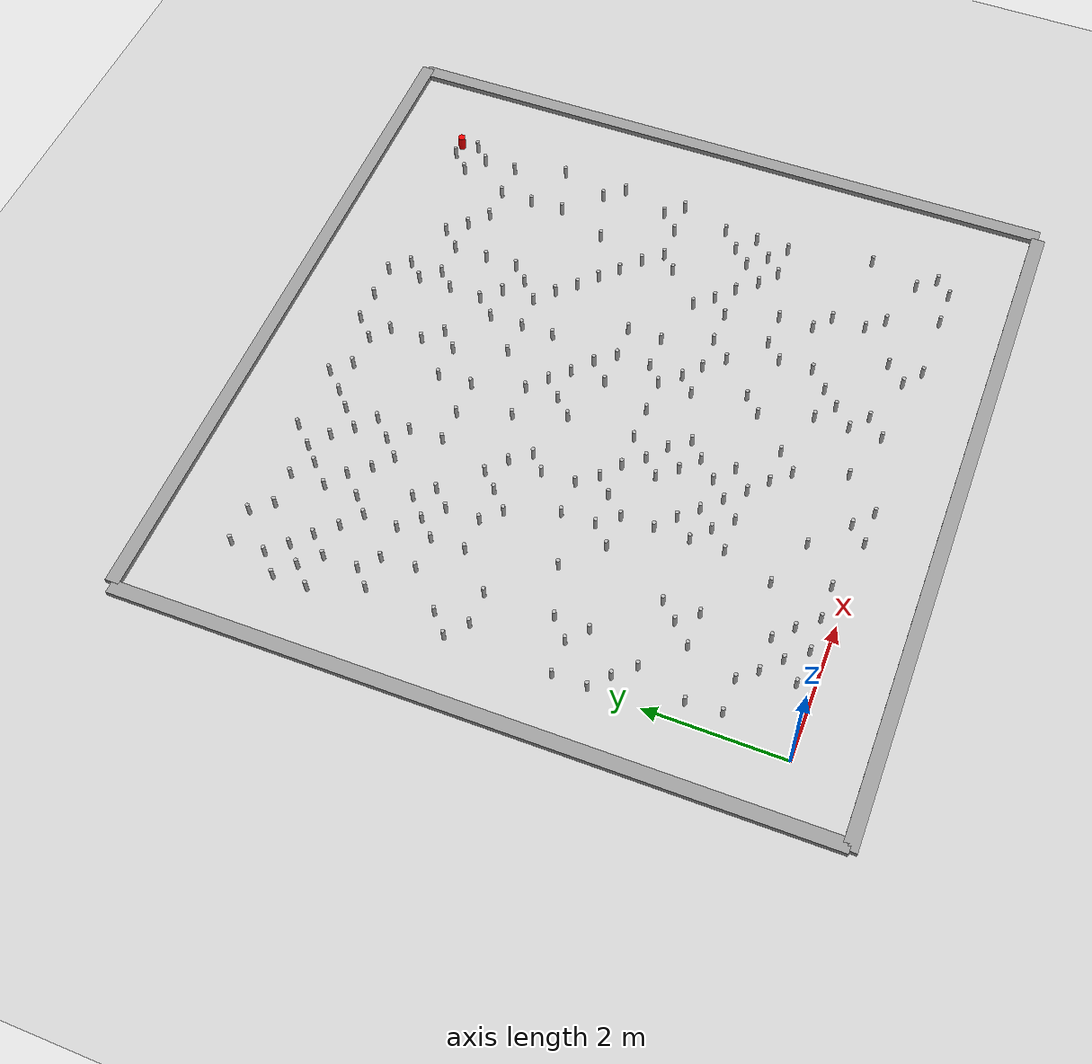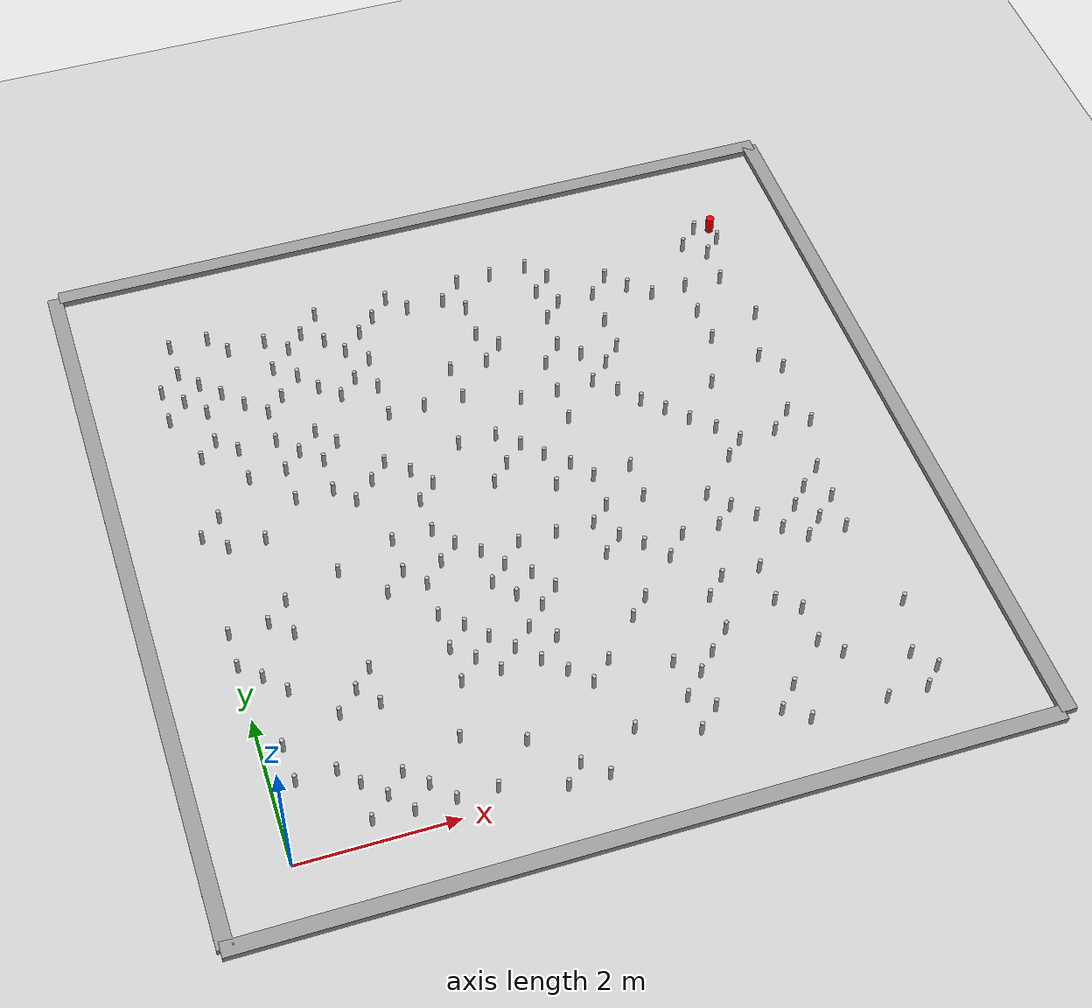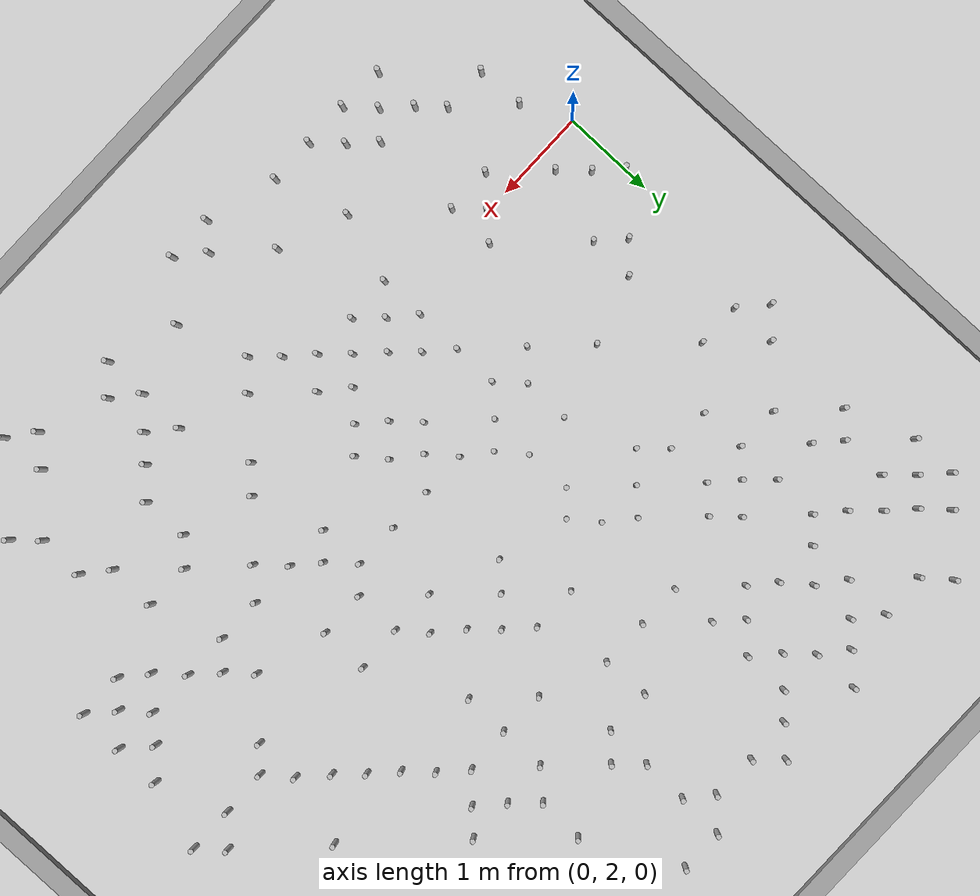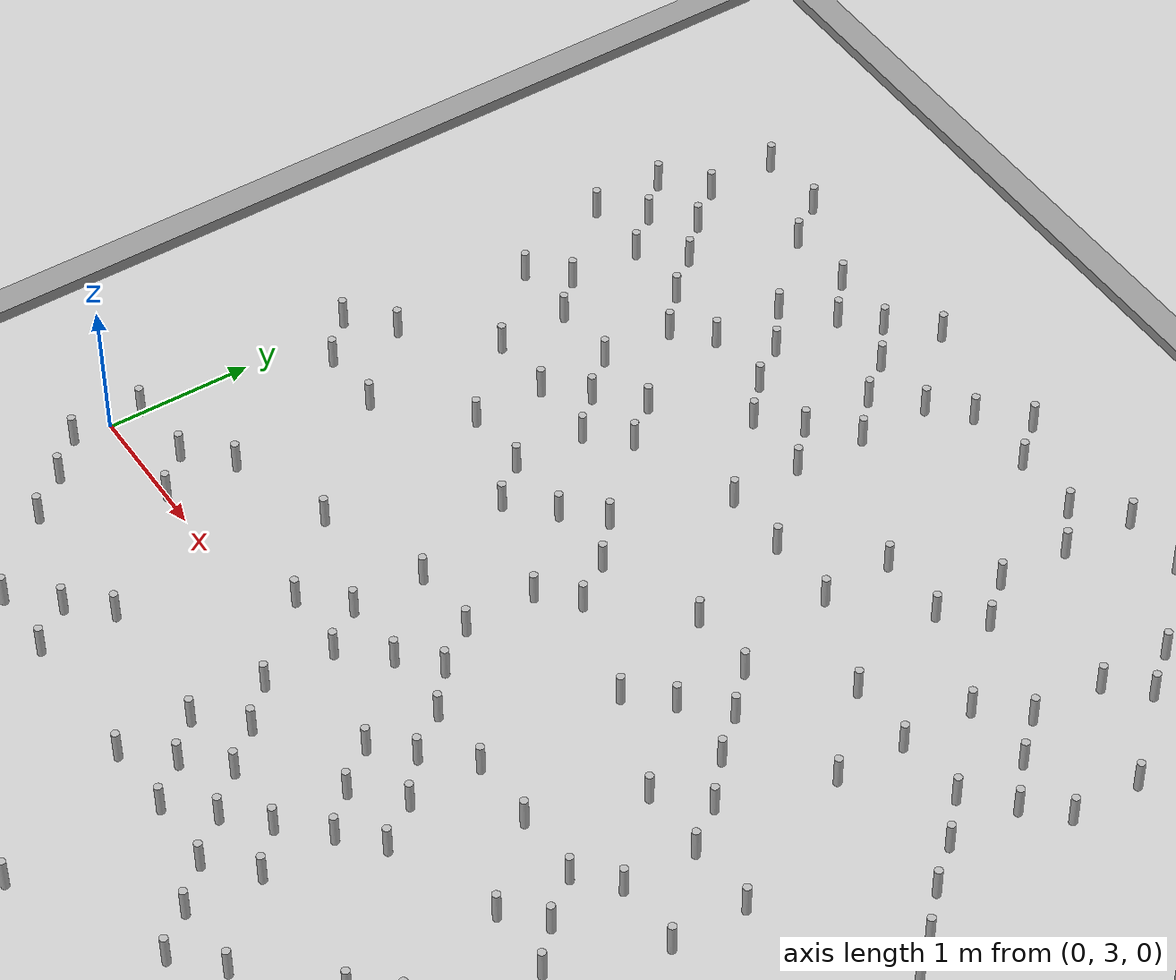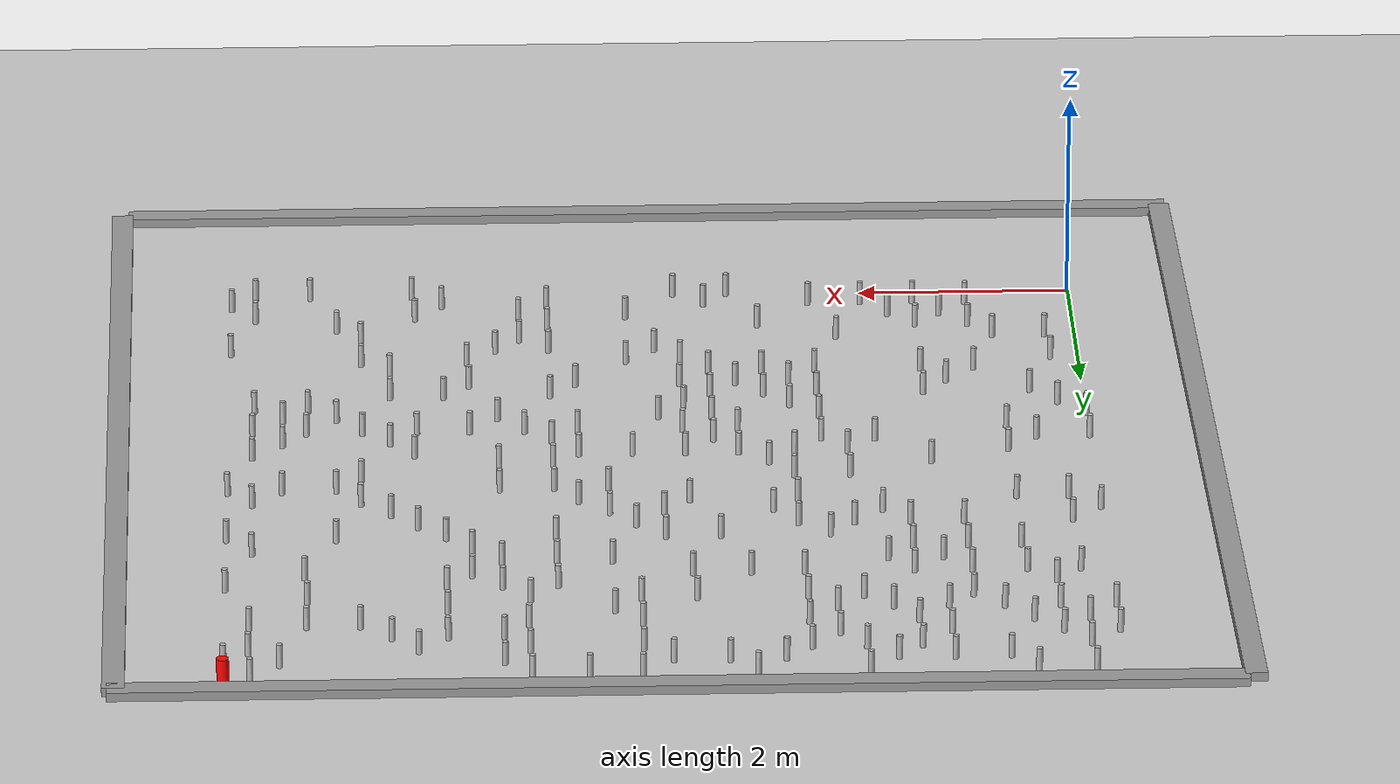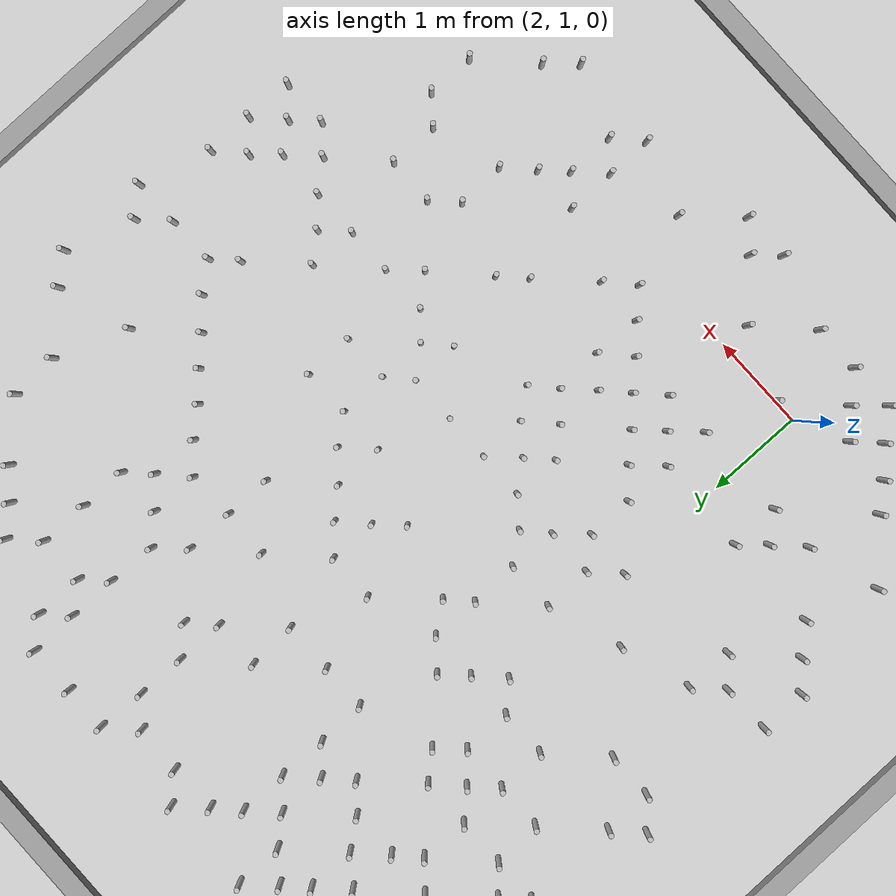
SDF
<sdf version="1.6">
 <world name="default">
  <light name="sun" type="directional">
   <pose>0 0 10 0 -0 0</pose>
   <diffuse>0.8 0.8 0.8 1</diffuse>
   <specular>0.1 0.1 0.1 1</specular>
   <attenuation>
    <range>1000</range>
    <constant>0.9</constant>
    <linear>0.01</linear>
    <quadratic>0.001</quadratic>
   </attenuation>
   <direction>-0.5 0.5 -1</direction>
  </light>
  <model name="ground_plane">
   <static>1</static>
   <link name="link">
    <collision name="collision">
     <geometry><plane><normal>0 0 1</normal><size>100 100</size></plane></geometry>
     <surface><friction><ode><mu>100</mu><mu2>50</mu2></ode></friction></surface>
    </collision>
    <visual name="visual">
     <cast_shadows>0</cast_shadows>
     <geometry><plane><normal>0 0 1</normal><size>100 100</size></plane></geometry>
     <material>
      <script><uri>file://media/materials/scripts/gazebo.material</uri><name>Gazebo/Grey</name></script>
     </material>
    </visual>
   </link>
  </model>
  <gravity>0 0 -9.8</gravity>
  <magnetic_field>6e-06 2.3e-05 -4.2e-05</magnetic_field>
  <atmosphere type="adiabatic"/>
  <physics name="default_physics" default="0" type="ode">
   <max_step_size>0.001</max_step_size>
   <real_time_factor>1</real_time_factor>
   <real_time_update_rate>1000</real_time_update_rate>
  </physics>
  <scene><ambient>0.4 0.4 0.4 1</ambient><background>0.7 0.7 0.7 1</background><shadows>1</shadows></scene>
  <spherical_coordinates>
   <surface_model>EARTH_WGS84</surface_model>
   <latitude_deg>0</latitude_deg>
   <longitude_deg>0</longitude_deg>
   <elevation>0</elevation>
   <heading_deg>0</heading_deg>
  </spherical_coordinates>
  <model name="goal">
   <link name="link">
    <pose>0 0 0.115 0 -0 0</pose>
    <inertial>
     <mass>0.0005</mass>
     <inertia><ixx>0.00058</ixx><ixy>0</ixy><ixz>0</ixz><iyy>0.00058</iyy><iyz>0</iyz><izz>0.00019</izz></inertia>
    </inertial>
    <visual name="visual">
     <geometry><cylinder><radius>0.055</radius><length>0.23</length></cylinder></geometry>
     <material>
      <script>
       <uri>model://beer/materials/scripts</uri>
       <uri>model://beer/materials/textures</uri>
       <name>Beer/Diffuse</name>
      </script>
      <ambient>1 0 0 1</ambient>
      <diffuse>1 0 0 1</diffuse>
      <specular>0 0 0 1</specular>
      <emissive>0 0 0 1</emissive>
      <shader type="vertex"><normal_map>__default__</normal_map></shader>
     </material>
    </visual>
    <collision name="collision">
     <geometry><cylinder><radius>0.055</radius><length>0.23</length></cylinder></geometry>
     <surface>
      <friction>
       <ode><mu>1</mu><mu2>1</mu2><fdir1>0 0 0</fdir1><slip1>0</slip1><slip2>0</slip2></ode>
       <torsional>
        <coefficient>1</coefficient>
        <patch_radius>0</patch_radius>
        <surface_radius>0</surface_radius>
        <use_patch_radius>1</use_patch_radius>
        <ode><slip>0</slip></ode>
       </torsional>
      </friction>
      <bounce><restitution_coefficient>0</restitution_coefficient><threshold>1e+06</threshold></bounce>
      <contact>
       <collide_without_contact>0</collide_without_contact>
       <collide_without_contact_bitmask>1</collide_without_contact_bitmask>
       <collide_bitmask>1</collide_bitmask>
       <ode>
        <soft_cfm>0</soft_cfm>
        <soft_erp>0.2</soft_erp>
        <kp>1e+13</kp>
        <kd>1</kd>
        <max_vel>0.01</max_vel>
        <min_depth>0</min_depth>
       </ode>
       <bullet>
        <split_impulse>1</split_impulse>
        <split_impulse_penetration_threshold>-0.01</split_impulse_penetration_threshold>
        <soft_cfm>0</soft_cfm>
        <soft_erp>0.2</soft_erp>
        <kp>1e+13</kp>
        <kd>1</kd>
       </bullet>
      </contact>
     </surface>
    </collision>
   </link>
   <static>0</static>
   <pose>8.0 8.0 -9e-06 -1e-06 -4e-06 0</pose>
  </model>
  <model name="wall1">
   <static>1</static>
   <link name="link">
    <pose>0 0 0.42 0 -0 0</pose>
    <collision name="collision"><geometry><box><size>10 0.2 0.084</size></box></geometry></collision>
    <visual name="visual">
     <cast_shadows>0</cast_shadows>
     <geometry><box><size>10 0.2 0.084</size></box></geometry>
     <material>
      <script>
       <uri>model://grey_wall/materials/scripts</uri>
       <uri>model://grey_wall/materials/textures</uri>
       <name>vrc/grey_wall</name>
      </script>
     </material>
    </visual>
   </link>
   <pose>-1 4.0 0 0 -0 -1.55905</pose>
  </model>
  <model name="wall2">
   <static>1</static>
   <link name="link">
    <pose>0 0 0.42 0 -0 0</pose>
    <collision name="collision"><geometry><box><size>10 0.2 0.084</size></box></geometry></collision>
    <visual name="visual">
     <cast_shadows>0</cast_shadows>
     <geometry><box><size>10 0.2 0.084</size></box></geometry>
     <material>
      <script>
       <uri>model://grey_wall/materials/scripts</uri>
       <uri>model://grey_wall/materials/textures</uri>
       <name>vrc/grey_wall</name>
      </script>
     </material>
    </visual>
   </link>
   <pose>4.0 9.0 0 0 -0 0</pose>
  </model>
  <model name="wall3">
   <static>1</static>
   <link name="link">
    <pose>0 0 0.42 0 -0 0</pose>
    <collision name="collision"><geometry><box><size>10 0.2 0.084</size></box></geometry></collision>
    <visual name="visual">
     <cast_shadows>0</cast_shadows>
     <geometry><box><size>10 0.2 0.084</size></box></geometry>
     <material>
      <script>
       <uri>model://grey_wall/materials/scripts</uri>
       <uri>model://grey_wall/materials/textures</uri>
       <name>vrc/grey_wall</name>
      </script>
     </material>
    </visual>
   </link>
   <pose>9.0 4.0 0 0 -0 -1.55905</pose>
  </model>
  <model name="wall4">
   <static>1</static>
   <link name="link">
    <pose>0 0 0.42 0 -0 0</pose>
    <collision name="collision"><geometry><box><size>10 0.2 0.084</size></box></geometry></collision>
    <visual name="visual">
     <cast_shadows>0</cast_shadows>
     <geometry><box><size>10 0.2 0.084</size></box></geometry>
     <material>
      <script>
       <uri>model://grey_wall/materials/scripts</uri>
       <uri>model://grey_wall/materials/textures</uri>
       <name>vrc/grey_wall</name>
      </script>
     </material>
    </visual>
   </link>
   <pose>4.0 -1 0 0 -0 0</pose>
  </model>
  <model name="can4.259239740993.5">
   <link name="link">
    <pose>0 0 0.115 0 -0 0</pose>
    <inertial>
     <mass>0.39</mass>
     <inertia><ixx>0.00058</ixx><ixy>0</ixy><ixz>0</ixz><iyy>0.00058</iyy><iyz>0</iyz><izz>0.00019</izz></inertia>
    </inertial>
    <collision name="collision">
     <geometry><cylinder><radius>0.0275</radius><length>0.23</length></cylinder></geometry>
    </collision>
    <visual name="visual">
     <geometry><cylinder><radius>0.0275</radius><length>0.23</length></cylinder></geometry>
     <material>
      <script>
       <uri>model://beer/materials/scripts</uri>
       <uri>model://beer/materials/textures</uri>
       <name>Beer/Diffuse</name>
      </script>
     </material>
    </visual>
   </link>
   <pose>4.25923974099 3.5 -2e-06 1e-06 0 -9.5e-05</pose>
  </model>
  <model name="can1.01.72601428327">
   <link name="link">
    <pose>0 0 0.115 0 -0 0</pose>
    <inertial>
     <mass>0.39</mass>
     <inertia><ixx>0.00058</ixx><ixy>0</ixy><ixz>0</ixz><iyy>0.00058</iyy><iyz>0</iyz><izz>0.00019</izz></inertia>
    </inertial>
    <collision name="collision">
     <geometry><cylinder><radius>0.0275</radius><length>0.23</length></cylinder></geometry>
    </collision>
    <visual name="visual">
     <geometry><cylinder><radius>0.0275</radius><length>0.23</length></cylinder></geometry>
     <material>
      <script>
       <uri>model://beer/materials/scripts</uri>
       <uri>model://beer/materials/textures</uri>
       <name>Beer/Diffuse</name>
      </script>
     </material>
    </visual>
   </link>
   <pose>1.0 1.72601428327 -2e-06 1e-06 0 -9.5e-05</pose>
  </model>
  <model name="can6.261647392187.5">
   <link name="link">
    <pose>0 0 0.115 0 -0 0</pose>
    <inertial>
     <mass>0.39</mass>
     <inertia><ixx>0.00058</ixx><ixy>0</ixy><ixz>0</ixz><iyy>0.00058</iyy><iyz>0</iyz><izz>0.00019</izz></inertia>
    </inertial>
    <collision name="collision">
     <geometry><cylinder><radius>0.0275</radius><length>0.23</length></cylinder></geometry>
    </collision>
    <visual name="visual">
     <geometry><cylinder><radius>0.0275</radius><length>0.23</length></cylinder></geometry>
     <material>
      <script>
       <uri>model://beer/materials/scripts</uri>
       <uri>model://beer/materials/textures</uri>
       <name>Beer/Diffuse</name>
      </script>
     </material>
    </visual>
   </link>
   <pose>6.26164739218 7.5 -2e-06 1e-06 0 -9.5e-05</pose>
  </model>
  <model name="can5.57.23160253035">
   <link name="link">
    <pose>0 0 0.115 0 -0 0</pose>
    <inertial>
     <mass>0.39</mass>
     <inertia><ixx>0.00058</ixx><ixy>0</ixy><ixz>0</ixz><iyy>0.00058</iyy><iyz>0</iyz><izz>0.00019</izz></inertia>
    </inertial>
    <collision name="collision">
     <geometry><cylinder><radius>0.0275</radius><length>0.23</length></cylinder></geometry>
    </collision>
    <visual name="visual">
     <geometry><cylinder><radius>0.0275</radius><length>0.23</length></cylinder></geometry>
     <material>
      <script>
       <uri>model://beer/materials/scripts</uri>
       <uri>model://beer/materials/textures</uri>
       <name>Beer/Diffuse</name>
      </script>
     </material>
    </visual>
   </link>
   <pose>5.5 7.23160253035 -2e-06 1e-06 0 -9.5e-05</pose>
  </model>
  <model name="can1.07.71864535366">
   <link name="link">
    <pose>0 0 0.115 0 -0 0</pose>
    <inertial>
     <mass>0.39</mass>
     <inertia><ixx>0.00058</ixx><ixy>0</ixy><ixz>0</ixz><iyy>0.00058</iyy><iyz>0</iyz><izz>0.00019</izz></inertia>
    </inertial>
    <collision name="collision">
     <geometry><cylinder><radius>0.0275</radius><length>0.23</length></cylinder></geometry>
    </collision>
    <visual name="visual">
     <geometry><cylinder><radius>0.0275</radius><length>0.23</length></cylinder></geometry>
     <material>
      <script>
       <uri>model://beer/materials/scripts</uri>
       <uri>model://beer/materials/textures</uri>
       <name>Beer/Diffuse</name>
      </script>
     </material>
    </visual>
   </link>
   <pose>1.0 7.71864535366 -2e-06 1e-06 0 -9.5e-05</pose>
  </model>
  <model name="can3.251200035556.0">
   <link name="link">
    <pose>0 0 0.115 0 -0 0</pose>
    <inertial>
     <mass>0.39</mass>
     <inertia><ixx>0.00058</ixx><ixy>0</ixy><ixz>0</ixz><iyy>0.00058</iyy><iyz>0</iyz><izz>0.00019</izz></inertia>
    </inertial>
    <collision name="collision">
     <geometry><cylinder><radius>0.0275</radius><length>0.23</length></cylinder></geometry>
    </collision>
    <visual name="visual">
     <geometry><cylinder><radius>0.0275</radius><length>0.23</length></cylinder></geometry>
     <material>
      <script>
       <uri>model://beer/materials/scripts</uri>
       <uri>model://beer/materials/textures</uri>
       <name>Beer/Diffuse</name>
      </script>
     </material>
    </visual>
   </link>
   <pose>3.25120003555 6.0 -2e-06 1e-06 0 -9.5e-05</pose>
  </model>
  <model name="can5.01.23273935473">
   <link name="link">
    <pose>0 0 0.115 0 -0 0</pose>
    <inertial>
     <mass>0.39</mass>
     <inertia><ixx>0.00058</ixx><ixy>0</ixy><ixz>0</ixz><iyy>0.00058</iyy><iyz>0</iyz><izz>0.00019</izz></inertia>
    </inertial>
    <collision name="collision">
     <geometry><cylinder><radius>0.0275</radius><length>0.23</length></cylinder></geometry>
    </collision>
    <visual name="visual">
     <geometry><cylinder><radius>0.0275</radius><length>0.23</length></cylinder></geometry>
     <material>
      <script>
       <uri>model://beer/materials/scripts</uri>
       <uri>model://beer/materials/textures</uri>
       <name>Beer/Diffuse</name>
      </script>
     </material>
    </visual>
   </link>
   <pose>5.0 1.23273935473 -2e-06 1e-06 0 -9.5e-05</pose>
  </model>
  <model name="can1.752240229540.5">
   <link name="link">
    <pose>0 0 0.115 0 -0 0</pose>
    <inertial>
     <mass>0.39</mass>
     <inertia><ixx>0.00058</ixx><ixy>0</ixy><ixz>0</ixz><iyy>0.00058</iyy><iyz>0</iyz><izz>0.00019</izz></inertia>
    </inertial>
    <collision name="collision">
     <geometry><cylinder><radius>0.0275</radius><length>0.23</length></cylinder></geometry>
    </collision>
    <visual name="visual">
     <geometry><cylinder><radius>0.0275</radius><length>0.23</length></cylinder></geometry>
     <material>
      <script>
       <uri>model://beer/materials/scripts</uri>
       <uri>model://beer/materials/textures</uri>
       <name>Beer/Diffuse</name>
      </script>
     </material>
    </visual>
   </link>
   <pose>1.75224022954 0.5 -2e-06 1e-06 0 -9.5e-05</pose>
  </model>
  <model name="can8.01.23944706621">
   <link name="link">
    <pose>0 0 0.115 0 -0 0</pose>
    <inertial>
     <mass>0.39</mass>
     <inertia><ixx>0.00058</ixx><ixy>0</ixy><ixz>0</ixz><iyy>0.00058</iyy><iyz>0</iyz><izz>0.00019</izz></inertia>
    </inertial>
    <collision name="collision">
     <geometry><cylinder><radius>0.0275</radius><length>0.23</length></cylinder></geometry>
    </collision>
    <visual name="visual">
     <geometry><cylinder><radius>0.0275</radius><length>0.23</length></cylinder></geometry>
     <material>
      <script>
       <uri>model://beer/materials/scripts</uri>
       <uri>model://beer/materials/textures</uri>
       <name>Beer/Diffuse</name>
      </script>
     </material>
    </visual>
   </link>
   <pose>8.0 1.23944706621 -2e-06 1e-06 0 -9.5e-05</pose>
  </model>
  <model name="can3.50.240996124034">
   <link name="link">
    <pose>0 0 0.115 0 -0 0</pose>
    <inertial>
     <mass>0.39</mass>
     <inertia><ixx>0.00058</ixx><ixy>0</ixy><ixz>0</ixz><iyy>0.00058</iyy><iyz>0</iyz><izz>0.00019</izz></inertia>
    </inertial>
    <collision name="collision">
     <geometry><cylinder><radius>0.0275</radius><length>0.23</length></cylinder></geometry>
    </collision>
    <visual name="visual">
     <geometry><cylinder><radius>0.0275</radius><length>0.23</length></cylinder></geometry>
     <material>
      <script>
       <uri>model://beer/materials/scripts</uri>
       <uri>model://beer/materials/textures</uri>
       <name>Beer/Diffuse</name>
      </script>
     </material>
    </visual>
   </link>
   <pose>3.5 0.240996124034 -2e-06 1e-06 0 -9.5e-05</pose>
  </model>
  <model name="can6.283426696240.0">
   <link name="link">
    <pose>0 0 0.115 0 -0 0</pose>
    <inertial>
     <mass>0.39</mass>
     <inertia><ixx>0.00058</ixx><ixy>0</ixy><ixz>0</ixz><iyy>0.00058</iyy><iyz>0</iyz><izz>0.00019</izz></inertia>
    </inertial>
    <collision name="collision">
     <geometry><cylinder><radius>0.0275</radius><length>0.23</length></cylinder></geometry>
    </collision>
    <visual name="visual">
     <geometry><cylinder><radius>0.0275</radius><length>0.23</length></cylinder></geometry>
     <material>
      <script>
       <uri>model://beer/materials/scripts</uri>
       <uri>model://beer/materials/textures</uri>
       <name>Beer/Diffuse</name>
      </script>
     </material>
    </visual>
   </link>
   <pose>6.28342669624 0.0 -2e-06 1e-06 0 -9.5e-05</pose>
  </model>
  <model name="can1.55.7417198135">
   <link name="link">
    <pose>0 0 0.115 0 -0 0</pose>
    <inertial>
     <mass>0.39</mass>
     <inertia><ixx>0.00058</ixx><ixy>0</ixy><ixz>0</ixz><iyy>0.00058</iyy><iyz>0</iyz><izz>0.00019</izz></inertia>
    </inertial>
    <collision name="collision">
     <geometry><cylinder><radius>0.0275</radius><length>0.23</length></cylinder></geometry>
    </collision>
    <visual name="visual">
     <geometry><cylinder><radius>0.0275</radius><length>0.23</length></cylinder></geometry>
     <material>
      <script>
       <uri>model://beer/materials/scripts</uri>
       <uri>model://beer/materials/textures</uri>
       <name>Beer/Diffuse</name>
      </script>
     </material>
    </visual>
   </link>
   <pose>1.5 5.7417198135 -2e-06 1e-06 0 -9.5e-05</pose>
  </model>
  <model name="can5.76251627113.0">
   <link name="link">
    <pose>0 0 0.115 0 -0 0</pose>
    <inertial>
     <mass>0.39</mass>
     <inertia><ixx>0.00058</ixx><ixy>0</ixy><ixz>0</ixz><iyy>0.00058</iyy><iyz>0</iyz><izz>0.00019</izz></inertia>
    </inertial>
    <collision name="collision">
     <geometry><cylinder><radius>0.0275</radius><length>0.23</length></cylinder></geometry>
    </collision>
    <visual name="visual">
     <geometry><cylinder><radius>0.0275</radius><length>0.23</length></cylinder></geometry>
     <material>
      <script>
       <uri>model://beer/materials/scripts</uri>
       <uri>model://beer/materials/textures</uri>
       <name>Beer/Diffuse</name>
      </script>
     </material>
    </visual>
   </link>
   <pose>5.7625162711 3.0 -2e-06 1e-06 0 -9.5e-05</pose>
  </model>
  <model name="can4.271879120571.5">
   <link name="link">
    <pose>0 0 0.115 0 -0 0</pose>
    <inertial>
     <mass>0.39</mass>
     <inertia><ixx>0.00058</ixx><ixy>0</ixy><ixz>0</ixz><iyy>0.00058</iyy><iyz>0</iyz><izz>0.00019</izz></inertia>
    </inertial>
    <collision name="collision">
     <geometry><cylinder><radius>0.0275</radius><length>0.23</length></cylinder></geometry>
    </collision>
    <visual name="visual">
     <geometry><cylinder><radius>0.0275</radius><length>0.23</length></cylinder></geometry>
     <material>
      <script>
       <uri>model://beer/materials/scripts</uri>
       <uri>model://beer/materials/textures</uri>
       <name>Beer/Diffuse</name>
      </script>
     </material>
    </visual>
   </link>
   <pose>4.27187912057 1.5 -2e-06 1e-06 0 -9.5e-05</pose>
  </model>
  <model name="can5.54.240172933">
   <link name="link">
    <pose>0 0 0.115 0 -0 0</pose>
    <inertial>
     <mass>0.39</mass>
     <inertia><ixx>0.00058</ixx><ixy>0</ixy><ixz>0</ixz><iyy>0.00058</iyy><iyz>0</iyz><izz>0.00019</izz></inertia>
    </inertial>
    <collision name="collision">
     <geometry><cylinder><radius>0.0275</radius><length>0.23</length></cylinder></geometry>
    </collision>
    <visual name="visual">
     <geometry><cylinder><radius>0.0275</radius><length>0.23</length></cylinder></geometry>
     <material>
      <script>
       <uri>model://beer/materials/scripts</uri>
       <uri>model://beer/materials/textures</uri>
       <name>Beer/Diffuse</name>
      </script>
     </material>
    </visual>
   </link>
   <pose>5.5 4.240172933 -2e-06 1e-06 0 -9.5e-05</pose>
  </model>
  <model name="can1.00.244068706249">
   <link name="link">
    <pose>0 0 0.115 0 -0 0</pose>
    <inertial>
     <mass>0.39</mass>
     <inertia><ixx>0.00058</ixx><ixy>0</ixy><ixz>0</ixz><iyy>0.00058</iyy><iyz>0</iyz><izz>0.00019</izz></inertia>
    </inertial>
    <collision name="collision">
     <geometry><cylinder><radius>0.0275</radius><length>0.23</length></cylinder></geometry>
    </collision>
    <visual name="visual">
     <geometry><cylinder><radius>0.0275</radius><length>0.23</length></cylinder></geometry>
     <material>
      <script>
       <uri>model://beer/materials/scripts</uri>
       <uri>model://beer/materials/textures</uri>
       <name>Beer/Diffuse</name>
      </script>
     </material>
    </visual>
   </link>
   <pose>1.0 0.244068706249 -2e-06 1e-06 0 -9.5e-05</pose>
  </model>
  <model name="can4.56.73604558452">
   <link name="link">
    <pose>0 0 0.115 0 -0 0</pose>
    <inertial>
     <mass>0.39</mass>
     <inertia><ixx>0.00058</ixx><ixy>0</ixy><ixz>0</ixz><iyy>0.00058</iyy><iyz>0</iyz><izz>0.00019</izz></inertia>
    </inertial>
    <collision name="collision">
     <geometry><cylinder><radius>0.0275</radius><length>0.23</length></cylinder></geometry>
    </collision>
    <visual name="visual">
     <geometry><cylinder><radius>0.0275</radius><length>0.23</length></cylinder></geometry>
     <material>
      <script>
       <uri>model://beer/materials/scripts</uri>
       <uri>model://beer/materials/textures</uri>
       <name>Beer/Diffuse</name>
      </script>
     </material>
    </visual>
   </link>
   <pose>4.5 6.73604558452 -2e-06 1e-06 0 -9.5e-05</pose>
  </model>
  <model name="can0.7762787411673.5">
   <link name="link">
    <pose>0 0 0.115 0 -0 0</pose>
    <inertial>
     <mass>0.39</mass>
     <inertia><ixx>0.00058</ixx><ixy>0</ixy><ixz>0</ixz><iyy>0.00058</iyy><iyz>0</iyz><izz>0.00019</izz></inertia>
    </inertial>
    <collision name="collision">
     <geometry><cylinder><radius>0.0275</radius><length>0.23</length></cylinder></geometry>
    </collision>
    <visual name="visual">
     <geometry><cylinder><radius>0.0275</radius><length>0.23</length></cylinder></geometry>
     <material>
      <script>
       <uri>model://beer/materials/scripts</uri>
       <uri>model://beer/materials/textures</uri>
       <name>Beer/Diffuse</name>
      </script>
     </material>
    </visual>
   </link>
   <pose>0.776278741167 3.5 -2e-06 1e-06 0 -9.5e-05</pose>
  </model>
  <model name="can3.03.71716802057">
   <link name="link">
    <pose>0 0 0.115 0 -0 0</pose>
    <inertial>
     <mass>0.39</mass>
     <inertia><ixx>0.00058</ixx><ixy>0</ixy><ixz>0</ixz><iyy>0.00058</iyy><iyz>0</iyz><izz>0.00019</izz></inertia>
    </inertial>
    <collision name="collision">
     <geometry><cylinder><radius>0.0275</radius><length>0.23</length></cylinder></geometry>
    </collision>
    <visual name="visual">
     <geometry><cylinder><radius>0.0275</radius><length>0.23</length></cylinder></geometry>
     <material>
      <script>
       <uri>model://beer/materials/scripts</uri>
       <uri>model://beer/materials/textures</uri>
       <name>Beer/Diffuse</name>
      </script>
     </material>
    </visual>
   </link>
   <pose>3.0 3.71716802057 -2e-06 1e-06 0 -9.5e-05</pose>
  </model>
  <model name="can6.77129277644.0">
   <link name="link">
    <pose>0 0 0.115 0 -0 0</pose>
    <inertial>
     <mass>0.39</mass>
     <inertia><ixx>0.00058</ixx><ixy>0</ixy><ixz>0</ixz><iyy>0.00058</iyy><iyz>0</iyz><izz>0.00019</izz></inertia>
    </inertial>
    <collision name="collision">
     <geometry><cylinder><radius>0.0275</radius><length>0.23</length></cylinder></geometry>
    </collision>
    <visual name="visual">
     <geometry><cylinder><radius>0.0275</radius><length>0.23</length></cylinder></geometry>
     <material>
      <script>
       <uri>model://beer/materials/scripts</uri>
       <uri>model://beer/materials/textures</uri>
       <name>Beer/Diffuse</name>
      </script>
     </material>
    </visual>
   </link>
   <pose>6.7712927764 4.0 -2e-06 1e-06 0 -9.5e-05</pose>
  </model>
  <model name="can3.26268632878.0">
   <link name="link">
    <pose>0 0 0.115 0 -0 0</pose>
    <inertial>
     <mass>0.39</mass>
     <inertia><ixx>0.00058</ixx><ixy>0</ixy><ixz>0</ixz><iyy>0.00058</iyy><iyz>0</iyz><izz>0.00019</izz></inertia>
    </inertial>
    <collision name="collision">
     <geometry><cylinder><radius>0.0275</radius><length>0.23</length></cylinder></geometry>
    </collision>
    <visual name="visual">
     <geometry><cylinder><radius>0.0275</radius><length>0.23</length></cylinder></geometry>
     <material>
      <script>
       <uri>model://beer/materials/scripts</uri>
       <uri>model://beer/materials/textures</uri>
       <name>Beer/Diffuse</name>
      </script>
     </material>
    </visual>
   </link>
   <pose>3.2626863287 8.0 -2e-06 1e-06 0 -9.5e-05</pose>
  </model>
  <model name="can1.57.73077224657">
   <link name="link">
    <pose>0 0 0.115 0 -0 0</pose>
    <inertial>
     <mass>0.39</mass>
     <inertia><ixx>0.00058</ixx><ixy>0</ixy><ixz>0</ixz><iyy>0.00058</iyy><iyz>0</iyz><izz>0.00019</izz></inertia>
    </inertial>
    <collision name="collision">
     <geometry><cylinder><radius>0.0275</radius><length>0.23</length></cylinder></geometry>
    </collision>
    <visual name="visual">
     <geometry><cylinder><radius>0.0275</radius><length>0.23</length></cylinder></geometry>
     <material>
      <script>
       <uri>model://beer/materials/scripts</uri>
       <uri>model://beer/materials/textures</uri>
       <name>Beer/Diffuse</name>
      </script>
     </material>
    </visual>
   </link>
   <pose>1.5 7.73077224657 -2e-06 1e-06 0 -9.5e-05</pose>
  </model>
  <model name="can5.52.7180750364">
   <link name="link">
    <pose>0 0 0.115 0 -0 0</pose>
    <inertial>
     <mass>0.39</mass>
     <inertia><ixx>0.00058</ixx><ixy>0</ixy><ixz>0</ixz><iyy>0.00058</iyy><iyz>0</iyz><izz>0.00019</izz></inertia>
    </inertial>
    <collision name="collision">
     <geometry><cylinder><radius>0.0275</radius><length>0.23</length></cylinder></geometry>
    </collision>
    <visual name="visual">
     <geometry><cylinder><radius>0.0275</radius><length>0.23</length></cylinder></geometry>
     <material>
      <script>
       <uri>model://beer/materials/scripts</uri>
       <uri>model://beer/materials/textures</uri>
       <name>Beer/Diffuse</name>
      </script>
     </material>
    </visual>
   </link>
   <pose>5.5 2.7180750364 -2e-06 1e-06 0 -9.5e-05</pose>
  </model>
  <model name="can5.55.74418061242">
   <link name="link">
    <pose>0 0 0.115 0 -0 0</pose>
    <inertial>
     <mass>0.39</mass>
     <inertia><ixx>0.00058</ixx><ixy>0</ixy><ixz>0</ixz><iyy>0.00058</iyy><iyz>0</iyz><izz>0.00019</izz></inertia>
    </inertial>
    <collision name="collision">
     <geometry><cylinder><radius>0.0275</radius><length>0.23</length></cylinder></geometry>
    </collision>
    <visual name="visual">
     <geometry><cylinder><radius>0.0275</radius><length>0.23</length></cylinder></geometry>
     <material>
      <script>
       <uri>model://beer/materials/scripts</uri>
       <uri>model://beer/materials/textures</uri>
       <name>Beer/Diffuse</name>
      </script>
     </material>
    </visual>
   </link>
   <pose>5.5 5.74418061242 -2e-06 1e-06 0 -9.5e-05</pose>
  </model>
  <model name="can5.05.23609709394">
   <link name="link">
    <pose>0 0 0.115 0 -0 0</pose>
    <inertial>
     <mass>0.39</mass>
     <inertia><ixx>0.00058</ixx><ixy>0</ixy><ixz>0</ixz><iyy>0.00058</iyy><iyz>0</iyz><izz>0.00019</izz></inertia>
    </inertial>
    <collision name="collision">
     <geometry><cylinder><radius>0.0275</radius><length>0.23</length></cylinder></geometry>
    </collision>
    <visual name="visual">
     <geometry><cylinder><radius>0.0275</radius><length>0.23</length></cylinder></geometry>
     <material>
      <script>
       <uri>model://beer/materials/scripts</uri>
       <uri>model://beer/materials/textures</uri>
       <name>Beer/Diffuse</name>
      </script>
     </material>
    </visual>
   </link>
   <pose>5.0 5.23609709394 -2e-06 1e-06 0 -9.5e-05</pose>
  </model>
  <model name="can6.07.23395077898">
   <link name="link">
    <pose>0 0 0.115 0 -0 0</pose>
    <inertial>
     <mass>0.39</mass>
     <inertia><ixx>0.00058</ixx><ixy>0</ixy><ixz>0</ixz><iyy>0.00058</iyy><iyz>0</iyz><izz>0.00019</izz></inertia>
    </inertial>
    <collision name="collision">
     <geometry><cylinder><radius>0.0275</radius><length>0.23</length></cylinder></geometry>
    </collision>
    <visual name="visual">
     <geometry><cylinder><radius>0.0275</radius><length>0.23</length></cylinder></geometry>
     <material>
      <script>
       <uri>model://beer/materials/scripts</uri>
       <uri>model://beer/materials/textures</uri>
       <name>Beer/Diffuse</name>
      </script>
     </material>
    </visual>
   </link>
   <pose>6.0 7.23395077898 -2e-06 1e-06 0 -9.5e-05</pose>
  </model>
  <model name="can0.57.23638221713">
   <link name="link">
    <pose>0 0 0.115 0 -0 0</pose>
    <inertial>
     <mass>0.39</mass>
     <inertia><ixx>0.00058</ixx><ixy>0</ixy><ixz>0</ixz><iyy>0.00058</iyy><iyz>0</iyz><izz>0.00019</izz></inertia>
    </inertial>
    <collision name="collision">
     <geometry><cylinder><radius>0.0275</radius><length>0.23</length></cylinder></geometry>
    </collision>
    <visual name="visual">
     <geometry><cylinder><radius>0.0275</radius><length>0.23</length></cylinder></geometry>
     <material>
      <script>
       <uri>model://beer/materials/scripts</uri>
       <uri>model://beer/materials/textures</uri>
       <name>Beer/Diffuse</name>
      </script>
     </material>
    </visual>
   </link>
   <pose>0.5 7.23638221713 -2e-06 1e-06 0 -9.5e-05</pose>
  </model>
  <model name="can1.06.73229137934">
   <link name="link">
    <pose>0 0 0.115 0 -0 0</pose>
    <inertial>
     <mass>0.39</mass>
     <inertia><ixx>0.00058</ixx><ixy>0</ixy><ixz>0</ixz><iyy>0.00058</iyy><iyz>0</iyz><izz>0.00019</izz></inertia>
    </inertial>
    <collision name="collision">
     <geometry><cylinder><radius>0.0275</radius><length>0.23</length></cylinder></geometry>
    </collision>
    <visual name="visual">
     <geometry><cylinder><radius>0.0275</radius><length>0.23</length></cylinder></geometry>
     <material>
      <script>
       <uri>model://beer/materials/scripts</uri>
       <uri>model://beer/materials/textures</uri>
       <name>Beer/Diffuse</name>
      </script>
     </material>
    </visual>
   </link>
   <pose>1.0 6.73229137934 -2e-06 1e-06 0 -9.5e-05</pose>
  </model>
  <model name="can7.780025474363.5">
   <link name="link">
    <pose>0 0 0.115 0 -0 0</pose>
    <inertial>
     <mass>0.39</mass>
     <inertia><ixx>0.00058</ixx><ixy>0</ixy><ixz>0</ixz><iyy>0.00058</iyy><iyz>0</iyz><izz>0.00019</izz></inertia>
    </inertial>
    <collision name="collision">
     <geometry><cylinder><radius>0.0275</radius><length>0.23</length></cylinder></geometry>
    </collision>
    <visual name="visual">
     <geometry><cylinder><radius>0.0275</radius><length>0.23</length></cylinder></geometry>
     <material>
      <script>
       <uri>model://beer/materials/scripts</uri>
       <uri>model://beer/materials/textures</uri>
       <name>Beer/Diffuse</name>
      </script>
     </material>
    </visual>
   </link>
   <pose>7.78002547436 3.5 -2e-06 1e-06 0 -9.5e-05</pose>
  </model>
  <model name="can7.263588575147.0">
   <link name="link">
    <pose>0 0 0.115 0 -0 0</pose>
    <inertial>
     <mass>0.39</mass>
     <inertia><ixx>0.00058</ixx><ixy>0</ixy><ixz>0</ixz><iyy>0.00058</iyy><iyz>0</iyz><izz>0.00019</izz></inertia>
    </inertial>
    <collision name="collision">
     <geometry><cylinder><radius>0.0275</radius><length>0.23</length></cylinder></geometry>
    </collision>
    <visual name="visual">
     <geometry><cylinder><radius>0.0275</radius><length>0.23</length></cylinder></geometry>
     <material>
      <script>
       <uri>model://beer/materials/scripts</uri>
       <uri>model://beer/materials/textures</uri>
       <name>Beer/Diffuse</name>
      </script>
     </material>
    </visual>
   </link>
   <pose>7.26358857514 7.0 -2e-06 1e-06 0 -9.5e-05</pose>
  </model>
  <model name="can3.760414593241.5">
   <link name="link">
    <pose>0 0 0.115 0 -0 0</pose>
    <inertial>
     <mass>0.39</mass>
     <inertia><ixx>0.00058</ixx><ixy>0</ixy><ixz>0</ixz><iyy>0.00058</iyy><iyz>0</iyz><izz>0.00019</izz></inertia>
    </inertial>
    <collision name="collision">
     <geometry><cylinder><radius>0.0275</radius><length>0.23</length></cylinder></geometry>
    </collision>
    <visual name="visual">
     <geometry><cylinder><radius>0.0275</radius><length>0.23</length></cylinder></geometry>
     <material>
      <script>
       <uri>model://beer/materials/scripts</uri>
       <uri>model://beer/materials/textures</uri>
       <name>Beer/Diffuse</name>
      </script>
     </material>
    </visual>
   </link>
   <pose>3.76041459324 1.5 -2e-06 1e-06 0 -9.5e-05</pose>
  </model>
  <model name="can5.05.71921450227">
   <link name="link">
    <pose>0 0 0.115 0 -0 0</pose>
    <inertial>
     <mass>0.39</mass>
     <inertia><ixx>0.00058</ixx><ixy>0</ixy><ixz>0</ixz><iyy>0.00058</iyy><iyz>0</iyz><izz>0.00019</izz></inertia>
    </inertial>
    <collision name="collision">
     <geometry><cylinder><radius>0.0275</radius><length>0.23</length></cylinder></geometry>
    </collision>
    <visual name="visual">
     <geometry><cylinder><radius>0.0275</radius><length>0.23</length></cylinder></geometry>
     <material>
      <script>
       <uri>model://beer/materials/scripts</uri>
       <uri>model://beer/materials/textures</uri>
       <name>Beer/Diffuse</name>
      </script>
     </material>
    </visual>
   </link>
   <pose>5.0 5.71921450227 -2e-06 1e-06 0 -9.5e-05</pose>
  </model>
  <model name="can5.272040216381.0">
   <link name="link">
    <pose>0 0 0.115 0 -0 0</pose>
    <inertial>
     <mass>0.39</mass>
     <inertia><ixx>0.00058</ixx><ixy>0</ixy><ixz>0</ixz><iyy>0.00058</iyy><iyz>0</iyz><izz>0.00019</izz></inertia>
    </inertial>
    <collision name="collision">
     <geometry><cylinder><radius>0.0275</radius><length>0.23</length></cylinder></geometry>
    </collision>
    <visual name="visual">
     <geometry><cylinder><radius>0.0275</radius><length>0.23</length></cylinder></geometry>
     <material>
      <script>
       <uri>model://beer/materials/scripts</uri>
       <uri>model://beer/materials/textures</uri>
       <name>Beer/Diffuse</name>
      </script>
     </material>
    </visual>
   </link>
   <pose>5.27204021638 1.0 -2e-06 1e-06 0 -9.5e-05</pose>
  </model>
  <model name="can8.04.24028414604">
   <link name="link">
    <pose>0 0 0.115 0 -0 0</pose>
    <inertial>
     <mass>0.39</mass>
     <inertia><ixx>0.00058</ixx><ixy>0</ixy><ixz>0</ixz><iyy>0.00058</iyy><iyz>0</iyz><izz>0.00019</izz></inertia>
    </inertial>
    <collision name="collision">
     <geometry><cylinder><radius>0.0275</radius><length>0.23</length></cylinder></geometry>
    </collision>
    <visual name="visual">
     <geometry><cylinder><radius>0.0275</radius><length>0.23</length></cylinder></geometry>
     <material>
      <script>
       <uri>model://beer/materials/scripts</uri>
       <uri>model://beer/materials/textures</uri>
       <name>Beer/Diffuse</name>
      </script>
     </material>
    </visual>
   </link>
   <pose>8.0 4.24028414604 -2e-06 1e-06 0 -9.5e-05</pose>
  </model>
  <model name="can0.25373270277.0">
   <link name="link">
    <pose>0 0 0.115 0 -0 0</pose>
    <inertial>
     <mass>0.39</mass>
     <inertia><ixx>0.00058</ixx><ixy>0</ixy><ixz>0</ixz><iyy>0.00058</iyy><iyz>0</iyz><izz>0.00019</izz></inertia>
    </inertial>
    <collision name="collision">
     <geometry><cylinder><radius>0.0275</radius><length>0.23</length></cylinder></geometry>
    </collision>
    <visual name="visual">
     <geometry><cylinder><radius>0.0275</radius><length>0.23</length></cylinder></geometry>
     <material>
      <script>
       <uri>model://beer/materials/scripts</uri>
       <uri>model://beer/materials/textures</uri>
       <name>Beer/Diffuse</name>
      </script>
     </material>
    </visual>
   </link>
   <pose>0.2537327027 7.0 -2e-06 1e-06 0 -9.5e-05</pose>
  </model>
  <model name="can5.56.24059466734">
   <link name="link">
    <pose>0 0 0.115 0 -0 0</pose>
    <inertial>
     <mass>0.39</mass>
     <inertia><ixx>0.00058</ixx><ixy>0</ixy><ixz>0</ixz><iyy>0.00058</iyy><iyz>0</iyz><izz>0.00019</izz></inertia>
    </inertial>
    <collision name="collision">
     <geometry><cylinder><radius>0.0275</radius><length>0.23</length></cylinder></geometry>
    </collision>
    <visual name="visual">
     <geometry><cylinder><radius>0.0275</radius><length>0.23</length></cylinder></geometry>
     <material>
      <script>
       <uri>model://beer/materials/scripts</uri>
       <uri>model://beer/materials/textures</uri>
       <name>Beer/Diffuse</name>
      </script>
     </material>
    </visual>
   </link>
   <pose>5.5 6.24059466734 -2e-06 1e-06 0 -9.5e-05</pose>
  </model>
  <model name="can2.07.71637304159">
   <link name="link">
    <pose>0 0 0.115 0 -0 0</pose>
    <inertial>
     <mass>0.39</mass>
     <inertia><ixx>0.00058</ixx><ixy>0</ixy><ixz>0</ixz><iyy>0.00058</iyy><iyz>0</iyz><izz>0.00019</izz></inertia>
    </inertial>
    <collision name="collision">
     <geometry><cylinder><radius>0.0275</radius><length>0.23</length></cylinder></geometry>
    </collision>
    <visual name="visual">
     <geometry><cylinder><radius>0.0275</radius><length>0.23</length></cylinder></geometry>
     <material>
      <script>
       <uri>model://beer/materials/scripts</uri>
       <uri>model://beer/materials/textures</uri>
       <name>Beer/Diffuse</name>
      </script>
     </material>
    </visual>
   </link>
   <pose>2.0 7.71637304159 -2e-06 1e-06 0 -9.5e-05</pose>
  </model>
  <model name="can1.270332725475.0">
   <link name="link">
    <pose>0 0 0.115 0 -0 0</pose>
    <inertial>
     <mass>0.39</mass>
     <inertia><ixx>0.00058</ixx><ixy>0</ixy><ixz>0</ixz><iyy>0.00058</iyy><iyz>0</iyz><izz>0.00019</izz></inertia>
    </inertial>
    <collision name="collision">
     <geometry><cylinder><radius>0.0275</radius><length>0.23</length></cylinder></geometry>
    </collision>
    <visual name="visual">
     <geometry><cylinder><radius>0.0275</radius><length>0.23</length></cylinder></geometry>
     <material>
      <script>
       <uri>model://beer/materials/scripts</uri>
       <uri>model://beer/materials/textures</uri>
       <name>Beer/Diffuse</name>
      </script>
     </material>
    </visual>
   </link>
   <pose>1.27033272547 5.0 -2e-06 1e-06 0 -9.5e-05</pose>
  </model>
  <model name="can0.2743662335275.0">
   <link name="link">
    <pose>0 0 0.115 0 -0 0</pose>
    <inertial>
     <mass>0.39</mass>
     <inertia><ixx>0.00058</ixx><ixy>0</ixy><ixz>0</ixz><iyy>0.00058</iyy><iyz>0</iyz><izz>0.00019</izz></inertia>
    </inertial>
    <collision name="collision">
     <geometry><cylinder><radius>0.0275</radius><length>0.23</length></cylinder></geometry>
    </collision>
    <visual name="visual">
     <geometry><cylinder><radius>0.0275</radius><length>0.23</length></cylinder></geometry>
     <material>
      <script>
       <uri>model://beer/materials/scripts</uri>
       <uri>model://beer/materials/textures</uri>
       <name>Beer/Diffuse</name>
      </script>
     </material>
    </visual>
   </link>
   <pose>0.274366233527 5.0 -2e-06 1e-06 0 -9.5e-05</pose>
  </model>
  <model name="can5.253855203016.5">
   <link name="link">
    <pose>0 0 0.115 0 -0 0</pose>
    <inertial>
     <mass>0.39</mass>
     <inertia><ixx>0.00058</ixx><ixy>0</ixy><ixz>0</ixz><iyy>0.00058</iyy><iyz>0</iyz><izz>0.00019</izz></inertia>
    </inertial>
    <collision name="collision">
     <geometry><cylinder><radius>0.0275</radius><length>0.23</length></cylinder></geometry>
    </collision>
    <visual name="visual">
     <geometry><cylinder><radius>0.0275</radius><length>0.23</length></cylinder></geometry>
     <material>
      <script>
       <uri>model://beer/materials/scripts</uri>
       <uri>model://beer/materials/textures</uri>
       <name>Beer/Diffuse</name>
      </script>
     </material>
    </visual>
   </link>
   <pose>5.25385520301 6.5 -2e-06 1e-06 0 -9.5e-05</pose>
  </model>
  <model name="can3.758568706892.5">
   <link name="link">
    <pose>0 0 0.115 0 -0 0</pose>
    <inertial>
     <mass>0.39</mass>
     <inertia><ixx>0.00058</ixx><ixy>0</ixy><ixz>0</ixz><iyy>0.00058</iyy><iyz>0</iyz><izz>0.00019</izz></inertia>
    </inertial>
    <collision name="collision">
     <geometry><cylinder><radius>0.0275</radius><length>0.23</length></cylinder></geometry>
    </collision>
    <visual name="visual">
     <geometry><cylinder><radius>0.0275</radius><length>0.23</length></cylinder></geometry>
     <material>
      <script>
       <uri>model://beer/materials/scripts</uri>
       <uri>model://beer/materials/textures</uri>
       <name>Beer/Diffuse</name>
      </script>
     </material>
    </visual>
   </link>
   <pose>3.75856870689 2.5 -2e-06 1e-06 0 -9.5e-05</pose>
  </model>
  <model name="can5.51.23429831495">
   <link name="link">
    <pose>0 0 0.115 0 -0 0</pose>
    <inertial>
     <mass>0.39</mass>
     <inertia><ixx>0.00058</ixx><ixy>0</ixy><ixz>0</ixz><iyy>0.00058</iyy><iyz>0</iyz><izz>0.00019</izz></inertia>
    </inertial>
    <collision name="collision">
     <geometry><cylinder><radius>0.0275</radius><length>0.23</length></cylinder></geometry>
    </collision>
    <visual name="visual">
     <geometry><cylinder><radius>0.0275</radius><length>0.23</length></cylinder></geometry>
     <material>
      <script>
       <uri>model://beer/materials/scripts</uri>
       <uri>model://beer/materials/textures</uri>
       <name>Beer/Diffuse</name>
      </script>
     </material>
    </visual>
   </link>
   <pose>5.5 1.23429831495 -2e-06 1e-06 0 -9.5e-05</pose>
  </model>
  <model name="can2.75748403822.0">
   <link name="link">
    <pose>0 0 0.115 0 -0 0</pose>
    <inertial>
     <mass>0.39</mass>
     <inertia><ixx>0.00058</ixx><ixy>0</ixy><ixz>0</ixz><iyy>0.00058</iyy><iyz>0</iyz><izz>0.00019</izz></inertia>
    </inertial>
    <collision name="collision">
     <geometry><cylinder><radius>0.0275</radius><length>0.23</length></cylinder></geometry>
    </collision>
    <visual name="visual">
     <geometry><cylinder><radius>0.0275</radius><length>0.23</length></cylinder></geometry>
     <material>
      <script>
       <uri>model://beer/materials/scripts</uri>
       <uri>model://beer/materials/textures</uri>
       <name>Beer/Diffuse</name>
      </script>
     </material>
    </visual>
   </link>
   <pose>2.7574840382 2.0 -2e-06 1e-06 0 -9.5e-05</pose>
  </model>
  <model name="can3.02.24979325446">
   <link name="link">
    <pose>0 0 0.115 0 -0 0</pose>
    <inertial>
     <mass>0.39</mass>
     <inertia><ixx>0.00058</ixx><ixy>0</ixy><ixz>0</ixz><iyy>0.00058</iyy><iyz>0</iyz><izz>0.00019</izz></inertia>
    </inertial>
    <collision name="collision">
     <geometry><cylinder><radius>0.0275</radius><length>0.23</length></cylinder></geometry>
    </collision>
    <visual name="visual">
     <geometry><cylinder><radius>0.0275</radius><length>0.23</length></cylinder></geometry>
     <material>
      <script>
       <uri>model://beer/materials/scripts</uri>
       <uri>model://beer/materials/textures</uri>
       <name>Beer/Diffuse</name>
      </script>
     </material>
    </visual>
   </link>
   <pose>3.0 2.24979325446 -2e-06 1e-06 0 -9.5e-05</pose>
  </model>
  <model name="can0.2849297225011.0">
   <link name="link">
    <pose>0 0 0.115 0 -0 0</pose>
    <inertial>
     <mass>0.39</mass>
     <inertia><ixx>0.00058</ixx><ixy>0</ixy><ixz>0</ixz><iyy>0.00058</iyy><iyz>0</iyz><izz>0.00019</izz></inertia>
    </inertial>
    <collision name="collision">
     <geometry><cylinder><radius>0.0275</radius><length>0.23</length></cylinder></geometry>
    </collision>
    <visual name="visual">
     <geometry><cylinder><radius>0.0275</radius><length>0.23</length></cylinder></geometry>
     <material>
      <script>
       <uri>model://beer/materials/scripts</uri>
       <uri>model://beer/materials/textures</uri>
       <name>Beer/Diffuse</name>
      </script>
     </material>
    </visual>
   </link>
   <pose>0.284929722501 1.0 -2e-06 1e-06 0 -9.5e-05</pose>
  </model>
  <model name="can3.780668719752.0">
   <link name="link">
    <pose>0 0 0.115 0 -0 0</pose>
    <inertial>
     <mass>0.39</mass>
     <inertia><ixx>0.00058</ixx><ixy>0</ixy><ixz>0</ixz><iyy>0.00058</iyy><iyz>0</iyz><izz>0.00019</izz></inertia>
    </inertial>
    <collision name="collision">
     <geometry><cylinder><radius>0.0275</radius><length>0.23</length></cylinder></geometry>
    </collision>
    <visual name="visual">
     <geometry><cylinder><radius>0.0275</radius><length>0.23</length></cylinder></geometry>
     <material>
      <script>
       <uri>model://beer/materials/scripts</uri>
       <uri>model://beer/materials/textures</uri>
       <name>Beer/Diffuse</name>
      </script>
     </material>
    </visual>
   </link>
   <pose>3.78066871975 2.0 -2e-06 1e-06 0 -9.5e-05</pose>
  </model>
  <model name="can4.256025686936.5">
   <link name="link">
    <pose>0 0 0.115 0 -0 0</pose>
    <inertial>
     <mass>0.39</mass>
     <inertia><ixx>0.00058</ixx><ixy>0</ixy><ixz>0</ixz><iyy>0.00058</iyy><iyz>0</iyz><izz>0.00019</izz></inertia>
    </inertial>
    <collision name="collision">
     <geometry><cylinder><radius>0.0275</radius><length>0.23</length></cylinder></geometry>
    </collision>
    <visual name="visual">
     <geometry><cylinder><radius>0.0275</radius><length>0.23</length></cylinder></geometry>
     <material>
      <script>
       <uri>model://beer/materials/scripts</uri>
       <uri>model://beer/materials/textures</uri>
       <name>Beer/Diffuse</name>
      </script>
     </material>
    </visual>
   </link>
   <pose>4.25602568693 6.5 -2e-06 1e-06 0 -9.5e-05</pose>
  </model>
  <model name="can7.760497419898.0">
   <link name="link">
    <pose>0 0 0.115 0 -0 0</pose>
    <inertial>
     <mass>0.39</mass>
     <inertia><ixx>0.00058</ixx><ixy>0</ixy><ixz>0</ixz><iyy>0.00058</iyy><iyz>0</iyz><izz>0.00019</izz></inertia>
    </inertial>
    <collision name="collision">
     <geometry><cylinder><radius>0.0275</radius><length>0.23</length></cylinder></geometry>
    </collision>
    <visual name="visual">
     <geometry><cylinder><radius>0.0275</radius><length>0.23</length></cylinder></geometry>
     <material>
      <script>
       <uri>model://beer/materials/scripts</uri>
       <uri>model://beer/materials/textures</uri>
       <name>Beer/Diffuse</name>
      </script>
     </material>
    </visual>
   </link>
   <pose>7.76049741989 8.0 -2e-06 1e-06 0 -9.5e-05</pose>
  </model>
  <model name="can4.257250240657.0">
   <link name="link">
    <pose>0 0 0.115 0 -0 0</pose>
    <inertial>
     <mass>0.39</mass>
     <inertia><ixx>0.00058</ixx><ixy>0</ixy><ixz>0</ixz><iyy>0.00058</iyy><iyz>0</iyz><izz>0.00019</izz></inertia>
    </inertial>
    <collision name="collision">
     <geometry><cylinder><radius>0.0275</radius><length>0.23</length></cylinder></geometry>
    </collision>
    <visual name="visual">
     <geometry><cylinder><radius>0.0275</radius><length>0.23</length></cylinder></geometry>
     <material>
      <script>
       <uri>model://beer/materials/scripts</uri>
       <uri>model://beer/materials/textures</uri>
       <name>Beer/Diffuse</name>
      </script>
     </material>
    </visual>
   </link>
   <pose>4.25725024065 7.0 -2e-06 1e-06 0 -9.5e-05</pose>
  </model>
  <model name="can5.03.71855957263">
   <link name="link">
    <pose>0 0 0.115 0 -0 0</pose>
    <inertial>
     <mass>0.39</mass>
     <inertia><ixx>0.00058</ixx><ixy>0</ixy><ixz>0</ixz><iyy>0.00058</iyy><iyz>0</iyz><izz>0.00019</izz></inertia>
    </inertial>
    <collision name="collision">
     <geometry><cylinder><radius>0.0275</radius><length>0.23</length></cylinder></geometry>
    </collision>
    <visual name="visual">
     <geometry><cylinder><radius>0.0275</radius><length>0.23</length></cylinder></geometry>
     <material>
      <script>
       <uri>model://beer/materials/scripts</uri>
       <uri>model://beer/materials/textures</uri>
       <name>Beer/Diffuse</name>
      </script>
     </material>
    </visual>
   </link>
   <pose>5.0 3.71855957263 -2e-06 1e-06 0 -9.5e-05</pose>
  </model>
  <model name="can7.777884202987.0">
   <link name="link">
    <pose>0 0 0.115 0 -0 0</pose>
    <inertial>
     <mass>0.39</mass>
     <inertia><ixx>0.00058</ixx><ixy>0</ixy><ixz>0</ixz><iyy>0.00058</iyy><iyz>0</iyz><izz>0.00019</izz></inertia>
    </inertial>
    <collision name="collision">
     <geometry><cylinder><radius>0.0275</radius><length>0.23</length></cylinder></geometry>
    </collision>
    <visual name="visual">
     <geometry><cylinder><radius>0.0275</radius><length>0.23</length></cylinder></geometry>
     <material>
      <script>
       <uri>model://beer/materials/scripts</uri>
       <uri>model://beer/materials/textures</uri>
       <name>Beer/Diffuse</name>
      </script>
     </material>
    </visual>
   </link>
   <pose>7.77788420298 7.0 -2e-06 1e-06 0 -9.5e-05</pose>
  </model>
  <model name="can0.56.73592905389">
   <link name="link">
    <pose>0 0 0.115 0 -0 0</pose>
    <inertial>
     <mass>0.39</mass>
     <inertia><ixx>0.00058</ixx><ixy>0</ixy><ixz>0</ixz><iyy>0.00058</iyy><iyz>0</iyz><izz>0.00019</izz></inertia>
    </inertial>
    <collision name="collision">
     <geometry><cylinder><radius>0.0275</radius><length>0.23</length></cylinder></geometry>
    </collision>
    <visual name="visual">
     <geometry><cylinder><radius>0.0275</radius><length>0.23</length></cylinder></geometry>
     <material>
      <script>
       <uri>model://beer/materials/scripts</uri>
       <uri>model://beer/materials/textures</uri>
       <name>Beer/Diffuse</name>
      </script>
     </material>
    </visual>
   </link>
   <pose>0.5 6.73592905389 -2e-06 1e-06 0 -9.5e-05</pose>
  </model>
  <model name="can7.52.73224953836">
   <link name="link">
    <pose>0 0 0.115 0 -0 0</pose>
    <inertial>
     <mass>0.39</mass>
     <inertia><ixx>0.00058</ixx><ixy>0</ixy><ixz>0</ixz><iyy>0.00058</iyy><iyz>0</iyz><izz>0.00019</izz></inertia>
    </inertial>
    <collision name="collision">
     <geometry><cylinder><radius>0.0275</radius><length>0.23</length></cylinder></geometry>
    </collision>
    <visual name="visual">
     <geometry><cylinder><radius>0.0275</radius><length>0.23</length></cylinder></geometry>
     <material>
      <script>
       <uri>model://beer/materials/scripts</uri>
       <uri>model://beer/materials/textures</uri>
       <name>Beer/Diffuse</name>
      </script>
     </material>
    </visual>
   </link>
   <pose>7.5 2.73224953836 -2e-06 1e-06 0 -9.5e-05</pose>
  </model>
  <model name="can2.26621983638.0">
   <link name="link">
    <pose>0 0 0.115 0 -0 0</pose>
    <inertial>
     <mass>0.39</mass>
     <inertia><ixx>0.00058</ixx><ixy>0</ixy><ixz>0</ixz><iyy>0.00058</iyy><iyz>0</iyz><izz>0.00019</izz></inertia>
    </inertial>
    <collision name="collision">
     <geometry><cylinder><radius>0.0275</radius><length>0.23</length></cylinder></geometry>
    </collision>
    <visual name="visual">
     <geometry><cylinder><radius>0.0275</radius><length>0.23</length></cylinder></geometry>
     <material>
      <script>
       <uri>model://beer/materials/scripts</uri>
       <uri>model://beer/materials/textures</uri>
       <name>Beer/Diffuse</name>
      </script>
     </material>
    </visual>
   </link>
   <pose>2.2662198363 8.0 -2e-06 1e-06 0 -9.5e-05</pose>
  </model>
  <model name="can4.284088320798.0">
   <link name="link">
    <pose>0 0 0.115 0 -0 0</pose>
    <inertial>
     <mass>0.39</mass>
     <inertia><ixx>0.00058</ixx><ixy>0</ixy><ixz>0</ixz><iyy>0.00058</iyy><iyz>0</iyz><izz>0.00019</izz></inertia>
    </inertial>
    <collision name="collision">
     <geometry><cylinder><radius>0.0275</radius><length>0.23</length></cylinder></geometry>
    </collision>
    <visual name="visual">
     <geometry><cylinder><radius>0.0275</radius><length>0.23</length></cylinder></geometry>
     <material>
      <script>
       <uri>model://beer/materials/scripts</uri>
       <uri>model://beer/materials/textures</uri>
       <name>Beer/Diffuse</name>
      </script>
     </material>
    </visual>
   </link>
   <pose>4.28408832079 8.0 -2e-06 1e-06 0 -9.5e-05</pose>
  </model>
  <model name="can7.284809612776.0">
   <link name="link">
    <pose>0 0 0.115 0 -0 0</pose>
    <inertial>
     <mass>0.39</mass>
     <inertia><ixx>0.00058</ixx><ixy>0</ixy><ixz>0</ixz><iyy>0.00058</iyy><iyz>0</iyz><izz>0.00019</izz></inertia>
    </inertial>
    <collision name="collision">
     <geometry><cylinder><radius>0.0275</radius><length>0.23</length></cylinder></geometry>
    </collision>
    <visual name="visual">
     <geometry><cylinder><radius>0.0275</radius><length>0.23</length></cylinder></geometry>
     <material>
      <script>
       <uri>model://beer/materials/scripts</uri>
       <uri>model://beer/materials/textures</uri>
       <name>Beer/Diffuse</name>
      </script>
     </material>
    </visual>
   </link>
   <pose>7.28480961277 6.0 -2e-06 1e-06 0 -9.5e-05</pose>
  </model>
  <model name="can0.2615410947188.0">
   <link name="link">
    <pose>0 0 0.115 0 -0 0</pose>
    <inertial>
     <mass>0.39</mass>
     <inertia><ixx>0.00058</ixx><ixy>0</ixy><ixz>0</ixz><iyy>0.00058</iyy><iyz>0</iyz><izz>0.00019</izz></inertia>
    </inertial>
    <collision name="collision">
     <geometry><cylinder><radius>0.0275</radius><length>0.23</length></cylinder></geometry>
    </collision>
    <visual name="visual">
     <geometry><cylinder><radius>0.0275</radius><length>0.23</length></cylinder></geometry>
     <material>
      <script>
       <uri>model://beer/materials/scripts</uri>
       <uri>model://beer/materials/textures</uri>
       <name>Beer/Diffuse</name>
      </script>
     </material>
    </visual>
   </link>
   <pose>0.261541094718 8.0 -2e-06 1e-06 0 -9.5e-05</pose>
  </model>
  <model name="can0.7530170957196.0">
   <link name="link">
    <pose>0 0 0.115 0 -0 0</pose>
    <inertial>
     <mass>0.39</mass>
     <inertia><ixx>0.00058</ixx><ixy>0</ixy><ixz>0</ixz><iyy>0.00058</iyy><iyz>0</iyz><izz>0.00019</izz></inertia>
    </inertial>
    <collision name="collision">
     <geometry><cylinder><radius>0.0275</radius><length>0.23</length></cylinder></geometry>
    </collision>
    <visual name="visual">
     <geometry><cylinder><radius>0.0275</radius><length>0.23</length></cylinder></geometry>
     <material>
      <script>
       <uri>model://beer/materials/scripts</uri>
       <uri>model://beer/materials/textures</uri>
       <name>Beer/Diffuse</name>
      </script>
     </material>
    </visual>
   </link>
   <pose>0.753017095719 6.0 -2e-06 1e-06 0 -9.5e-05</pose>
  </model>
  <model name="can6.52.23536547833">
   <link name="link">
    <pose>0 0 0.115 0 -0 0</pose>
    <inertial>
     <mass>0.39</mass>
     <inertia><ixx>0.00058</ixx><ixy>0</ixy><ixz>0</ixz><iyy>0.00058</iyy><iyz>0</iyz><izz>0.00019</izz></inertia>
    </inertial>
    <collision name="collision">
     <geometry><cylinder><radius>0.0275</radius><length>0.23</length></cylinder></geometry>
    </collision>
    <visual name="visual">
     <geometry><cylinder><radius>0.0275</radius><length>0.23</length></cylinder></geometry>
     <material>
      <script>
       <uri>model://beer/materials/scripts</uri>
       <uri>model://beer/materials/textures</uri>
       <name>Beer/Diffuse</name>
      </script>
     </material>
    </visual>
   </link>
   <pose>6.5 2.23536547833 -2e-06 1e-06 0 -9.5e-05</pose>
  </model>
  <model name="can7.776456580990.0">
   <link name="link">
    <pose>0 0 0.115 0 -0 0</pose>
    <inertial>
     <mass>0.39</mass>
     <inertia><ixx>0.00058</ixx><ixy>0</ixy><ixz>0</ixz><iyy>0.00058</iyy><iyz>0</iyz><izz>0.00019</izz></inertia>
    </inertial>
    <collision name="collision">
     <geometry><cylinder><radius>0.0275</radius><length>0.23</length></cylinder></geometry>
    </collision>
    <visual name="visual">
     <geometry><cylinder><radius>0.0275</radius><length>0.23</length></cylinder></geometry>
     <material>
      <script>
       <uri>model://beer/materials/scripts</uri>
       <uri>model://beer/materials/textures</uri>
       <name>Beer/Diffuse</name>
      </script>
     </material>
    </visual>
   </link>
   <pose>7.77645658099 0.0 -2e-06 1e-06 0 -9.5e-05</pose>
  </model>
  <model name="can7.773467231880.5">
   <link name="link">
    <pose>0 0 0.115 0 -0 0</pose>
    <inertial>
     <mass>0.39</mass>
     <inertia><ixx>0.00058</ixx><ixy>0</ixy><ixz>0</ixz><iyy>0.00058</iyy><iyz>0</iyz><izz>0.00019</izz></inertia>
    </inertial>
    <collision name="collision">
     <geometry><cylinder><radius>0.0275</radius><length>0.23</length></cylinder></geometry>
    </collision>
    <visual name="visual">
     <geometry><cylinder><radius>0.0275</radius><length>0.23</length></cylinder></geometry>
     <material>
      <script>
       <uri>model://beer/materials/scripts</uri>
       <uri>model://beer/materials/textures</uri>
       <name>Beer/Diffuse</name>
      </script>
     </material>
    </visual>
   </link>
   <pose>7.77346723188 0.5 -2e-06 1e-06 0 -9.5e-05</pose>
  </model>
  <model name="can5.02.23685275921">
   <link name="link">
    <pose>0 0 0.115 0 -0 0</pose>
    <inertial>
     <mass>0.39</mass>
     <inertia><ixx>0.00058</ixx><ixy>0</ixy><ixz>0</ixz><iyy>0.00058</iyy><iyz>0</iyz><izz>0.00019</izz></inertia>
    </inertial>
    <collision name="collision">
     <geometry><cylinder><radius>0.0275</radius><length>0.23</length></cylinder></geometry>
    </collision>
    <visual name="visual">
     <geometry><cylinder><radius>0.0275</radius><length>0.23</length></cylinder></geometry>
     <material>
      <script>
       <uri>model://beer/materials/scripts</uri>
       <uri>model://beer/materials/textures</uri>
       <name>Beer/Diffuse</name>
      </script>
     </material>
    </visual>
   </link>
   <pose>5.0 2.23685275921 -2e-06 1e-06 0 -9.5e-05</pose>
  </model>
  <model name="can4.01.2448859186">
   <link name="link">
    <pose>0 0 0.115 0 -0 0</pose>
    <inertial>
     <mass>0.39</mass>
     <inertia><ixx>0.00058</ixx><ixy>0</ixy><ixz>0</ixz><iyy>0.00058</iyy><iyz>0</iyz><izz>0.00019</izz></inertia>
    </inertial>
    <collision name="collision">
     <geometry><cylinder><radius>0.0275</radius><length>0.23</length></cylinder></geometry>
    </collision>
    <visual name="visual">
     <geometry><cylinder><radius>0.0275</radius><length>0.23</length></cylinder></geometry>
     <material>
      <script>
       <uri>model://beer/materials/scripts</uri>
       <uri>model://beer/materials/textures</uri>
       <name>Beer/Diffuse</name>
      </script>
     </material>
    </visual>
   </link>
   <pose>4.0 1.2448859186 -2e-06 1e-06 0 -9.5e-05</pose>
  </model>
  <model name="can2.52.22568749587">
   <link name="link">
    <pose>0 0 0.115 0 -0 0</pose>
    <inertial>
     <mass>0.39</mass>
     <inertia><ixx>0.00058</ixx><ixy>0</ixy><ixz>0</ixz><iyy>0.00058</iyy><iyz>0</iyz><izz>0.00019</izz></inertia>
    </inertial>
    <collision name="collision">
     <geometry><cylinder><radius>0.0275</radius><length>0.23</length></cylinder></geometry>
    </collision>
    <visual name="visual">
     <geometry><cylinder><radius>0.0275</radius><length>0.23</length></cylinder></geometry>
     <material>
      <script>
       <uri>model://beer/materials/scripts</uri>
       <uri>model://beer/materials/textures</uri>
       <name>Beer/Diffuse</name>
      </script>
     </material>
    </visual>
   </link>
   <pose>2.5 2.22568749587 -2e-06 1e-06 0 -9.5e-05</pose>
  </model>
  <model name="can3.04.71551718072">
   <link name="link">
    <pose>0 0 0.115 0 -0 0</pose>
    <inertial>
     <mass>0.39</mass>
     <inertia><ixx>0.00058</ixx><ixy>0</ixy><ixz>0</ixz><iyy>0.00058</iyy><iyz>0</iyz><izz>0.00019</izz></inertia>
    </inertial>
    <collision name="collision">
     <geometry><cylinder><radius>0.0275</radius><length>0.23</length></cylinder></geometry>
    </collision>
    <visual name="visual">
     <geometry><cylinder><radius>0.0275</radius><length>0.23</length></cylinder></geometry>
     <material>
      <script>
       <uri>model://beer/materials/scripts</uri>
       <uri>model://beer/materials/textures</uri>
       <name>Beer/Diffuse</name>
      </script>
     </material>
    </visual>
   </link>
   <pose>3.0 4.71551718072 -2e-06 1e-06 0 -9.5e-05</pose>
  </model>
  <model name="can3.27002835113.0">
   <link name="link">
    <pose>0 0 0.115 0 -0 0</pose>
    <inertial>
     <mass>0.39</mass>
     <inertia><ixx>0.00058</ixx><ixy>0</ixy><ixz>0</ixz><iyy>0.00058</iyy><iyz>0</iyz><izz>0.00019</izz></inertia>
    </inertial>
    <collision name="collision">
     <geometry><cylinder><radius>0.0275</radius><length>0.23</length></cylinder></geometry>
    </collision>
    <visual name="visual">
     <geometry><cylinder><radius>0.0275</radius><length>0.23</length></cylinder></geometry>
     <material>
      <script>
       <uri>model://beer/materials/scripts</uri>
       <uri>model://beer/materials/textures</uri>
       <name>Beer/Diffuse</name>
      </script>
     </material>
    </visual>
   </link>
   <pose>3.2700283511 3.0 -2e-06 1e-06 0 -9.5e-05</pose>
  </model>
  <model name="can4.75658909583.5">
   <link name="link">
    <pose>0 0 0.115 0 -0 0</pose>
    <inertial>
     <mass>0.39</mass>
     <inertia><ixx>0.00058</ixx><ixy>0</ixy><ixz>0</ixz><iyy>0.00058</iyy><iyz>0</iyz><izz>0.00019</izz></inertia>
    </inertial>
    <collision name="collision">
     <geometry><cylinder><radius>0.0275</radius><length>0.23</length></cylinder></geometry>
    </collision>
    <visual name="visual">
     <geometry><cylinder><radius>0.0275</radius><length>0.23</length></cylinder></geometry>
     <material>
      <script>
       <uri>model://beer/materials/scripts</uri>
       <uri>model://beer/materials/textures</uri>
       <name>Beer/Diffuse</name>
      </script>
     </material>
    </visual>
   </link>
   <pose>4.7565890958 3.5 -2e-06 1e-06 0 -9.5e-05</pose>
  </model>
  <model name="can6.06.71885183796">
   <link name="link">
    <pose>0 0 0.115 0 -0 0</pose>
    <inertial>
     <mass>0.39</mass>
     <inertia><ixx>0.00058</ixx><ixy>0</ixy><ixz>0</ixz><iyy>0.00058</iyy><iyz>0</iyz><izz>0.00019</izz></inertia>
    </inertial>
    <collision name="collision">
     <geometry><cylinder><radius>0.0275</radius><length>0.23</length></cylinder></geometry>
    </collision>
    <visual name="visual">
     <geometry><cylinder><radius>0.0275</radius><length>0.23</length></cylinder></geometry>
     <material>
      <script>
       <uri>model://beer/materials/scripts</uri>
       <uri>model://beer/materials/textures</uri>
       <name>Beer/Diffuse</name>
      </script>
     </material>
    </visual>
   </link>
   <pose>6.0 6.71885183796 -2e-06 1e-06 0 -9.5e-05</pose>
  </model>
  <model name="can1.57.21565840624">
   <link name="link">
    <pose>0 0 0.115 0 -0 0</pose>
    <inertial>
     <mass>0.39</mass>
     <inertia><ixx>0.00058</ixx><ixy>0</ixy><ixz>0</ixz><iyy>0.00058</iyy><iyz>0</iyz><izz>0.00019</izz></inertia>
    </inertial>
    <collision name="collision">
     <geometry><cylinder><radius>0.0275</radius><length>0.23</length></cylinder></geometry>
    </collision>
    <visual name="visual">
     <geometry><cylinder><radius>0.0275</radius><length>0.23</length></cylinder></geometry>
     <material>
      <script>
       <uri>model://beer/materials/scripts</uri>
       <uri>model://beer/materials/textures</uri>
       <name>Beer/Diffuse</name>
      </script>
     </material>
    </visual>
   </link>
   <pose>1.5 7.21565840624 -2e-06 1e-06 0 -9.5e-05</pose>
  </model>
  <model name="can3.767635746763.5">
   <link name="link">
    <pose>0 0 0.115 0 -0 0</pose>
    <inertial>
     <mass>0.39</mass>
     <inertia><ixx>0.00058</ixx><ixy>0</ixy><ixz>0</ixz><iyy>0.00058</iyy><iyz>0</iyz><izz>0.00019</izz></inertia>
    </inertial>
    <collision name="collision">
     <geometry><cylinder><radius>0.0275</radius><length>0.23</length></cylinder></geometry>
    </collision>
    <visual name="visual">
     <geometry><cylinder><radius>0.0275</radius><length>0.23</length></cylinder></geometry>
     <material>
      <script>
       <uri>model://beer/materials/scripts</uri>
       <uri>model://beer/materials/textures</uri>
       <name>Beer/Diffuse</name>
      </script>
     </material>
    </visual>
   </link>
   <pose>3.76763574676 3.5 -2e-06 1e-06 0 -9.5e-05</pose>
  </model>
  <model name="can7.05.24713045878">
   <link name="link">
    <pose>0 0 0.115 0 -0 0</pose>
    <inertial>
     <mass>0.39</mass>
     <inertia><ixx>0.00058</ixx><ixy>0</ixy><ixz>0</ixz><iyy>0.00058</iyy><iyz>0</iyz><izz>0.00019</izz></inertia>
    </inertial>
    <collision name="collision">
     <geometry><cylinder><radius>0.0275</radius><length>0.23</length></cylinder></geometry>
    </collision>
    <visual name="visual">
     <geometry><cylinder><radius>0.0275</radius><length>0.23</length></cylinder></geometry>
     <material>
      <script>
       <uri>model://beer/materials/scripts</uri>
       <uri>model://beer/materials/textures</uri>
       <name>Beer/Diffuse</name>
      </script>
     </material>
    </visual>
   </link>
   <pose>7.0 5.24713045878 -2e-06 1e-06 0 -9.5e-05</pose>
  </model>
  <model name="can1.50.743371191487">
   <link name="link">
    <pose>0 0 0.115 0 -0 0</pose>
    <inertial>
     <mass>0.39</mass>
     <inertia><ixx>0.00058</ixx><ixy>0</ixy><ixz>0</ixz><iyy>0.00058</iyy><iyz>0</iyz><izz>0.00019</izz></inertia>
    </inertial>
    <collision name="collision">
     <geometry><cylinder><radius>0.0275</radius><length>0.23</length></cylinder></geometry>
    </collision>
    <visual name="visual">
     <geometry><cylinder><radius>0.0275</radius><length>0.23</length></cylinder></geometry>
     <material>
      <script>
       <uri>model://beer/materials/scripts</uri>
       <uri>model://beer/materials/textures</uri>
       <name>Beer/Diffuse</name>
      </script>
     </material>
    </visual>
   </link>
   <pose>1.5 0.743371191487 -2e-06 1e-06 0 -9.5e-05</pose>
  </model>
  <model name="can3.51.74041672292">
   <link name="link">
    <pose>0 0 0.115 0 -0 0</pose>
    <inertial>
     <mass>0.39</mass>
     <inertia><ixx>0.00058</ixx><ixy>0</ixy><ixz>0</ixz><iyy>0.00058</iyy><iyz>0</iyz><izz>0.00019</izz></inertia>
    </inertial>
    <collision name="collision">
     <geometry><cylinder><radius>0.0275</radius><length>0.23</length></cylinder></geometry>
    </collision>
    <visual name="visual">
     <geometry><cylinder><radius>0.0275</radius><length>0.23</length></cylinder></geometry>
     <material>
      <script>
       <uri>model://beer/materials/scripts</uri>
       <uri>model://beer/materials/textures</uri>
       <name>Beer/Diffuse</name>
      </script>
     </material>
    </visual>
   </link>
   <pose>3.5 1.74041672292 -2e-06 1e-06 0 -9.5e-05</pose>
  </model>
  <model name="can2.06.72047511491">
   <link name="link">
    <pose>0 0 0.115 0 -0 0</pose>
    <inertial>
     <mass>0.39</mass>
     <inertia><ixx>0.00058</ixx><ixy>0</ixy><ixz>0</ixz><iyy>0.00058</iyy><iyz>0</iyz><izz>0.00019</izz></inertia>
    </inertial>
    <collision name="collision">
     <geometry><cylinder><radius>0.0275</radius><length>0.23</length></cylinder></geometry>
    </collision>
    <visual name="visual">
     <geometry><cylinder><radius>0.0275</radius><length>0.23</length></cylinder></geometry>
     <material>
      <script>
       <uri>model://beer/materials/scripts</uri>
       <uri>model://beer/materials/textures</uri>
       <name>Beer/Diffuse</name>
      </script>
     </material>
    </visual>
   </link>
   <pose>2.0 6.72047511491 -2e-06 1e-06 0 -9.5e-05</pose>
  </model>
  <model name="can3.57.74040622642">
   <link name="link">
    <pose>0 0 0.115 0 -0 0</pose>
    <inertial>
     <mass>0.39</mass>
     <inertia><ixx>0.00058</ixx><ixy>0</ixy><ixz>0</ixz><iyy>0.00058</iyy><iyz>0</iyz><izz>0.00019</izz></inertia>
    </inertial>
    <collision name="collision">
     <geometry><cylinder><radius>0.0275</radius><length>0.23</length></cylinder></geometry>
    </collision>
    <visual name="visual">
     <geometry><cylinder><radius>0.0275</radius><length>0.23</length></cylinder></geometry>
     <material>
      <script>
       <uri>model://beer/materials/scripts</uri>
       <uri>model://beer/materials/textures</uri>
       <name>Beer/Diffuse</name>
      </script>
     </material>
    </visual>
   </link>
   <pose>3.5 7.74040622642 -2e-06 1e-06 0 -9.5e-05</pose>
  </model>
  <model name="can6.255560341535.0">
   <link name="link">
    <pose>0 0 0.115 0 -0 0</pose>
    <inertial>
     <mass>0.39</mass>
     <inertia><ixx>0.00058</ixx><ixy>0</ixy><ixz>0</ixz><iyy>0.00058</iyy><iyz>0</iyz><izz>0.00019</izz></inertia>
    </inertial>
    <collision name="collision">
     <geometry><cylinder><radius>0.0275</radius><length>0.23</length></cylinder></geometry>
    </collision>
    <visual name="visual">
     <geometry><cylinder><radius>0.0275</radius><length>0.23</length></cylinder></geometry>
     <material>
      <script>
       <uri>model://beer/materials/scripts</uri>
       <uri>model://beer/materials/textures</uri>
       <name>Beer/Diffuse</name>
      </script>
     </material>
    </visual>
   </link>
   <pose>6.25556034153 5.0 -2e-06 1e-06 0 -9.5e-05</pose>
  </model>
  <model name="can1.782580695847.0">
   <link name="link">
    <pose>0 0 0.115 0 -0 0</pose>
    <inertial>
     <mass>0.39</mass>
     <inertia><ixx>0.00058</ixx><ixy>0</ixy><ixz>0</ixz><iyy>0.00058</iyy><iyz>0</iyz><izz>0.00019</izz></inertia>
    </inertial>
    <collision name="collision">
     <geometry><cylinder><radius>0.0275</radius><length>0.23</length></cylinder></geometry>
    </collision>
    <visual name="visual">
     <geometry><cylinder><radius>0.0275</radius><length>0.23</length></cylinder></geometry>
     <material>
      <script>
       <uri>model://beer/materials/scripts</uri>
       <uri>model://beer/materials/textures</uri>
       <name>Beer/Diffuse</name>
      </script>
     </material>
    </visual>
   </link>
   <pose>1.78258069584 7.0 -2e-06 1e-06 0 -9.5e-05</pose>
  </model>
  <model name="can5.270948133220.5">
   <link name="link">
    <pose>0 0 0.115 0 -0 0</pose>
    <inertial>
     <mass>0.39</mass>
     <inertia><ixx>0.00058</ixx><ixy>0</ixy><ixz>0</ixz><iyy>0.00058</iyy><iyz>0</iyz><izz>0.00019</izz></inertia>
    </inertial>
    <collision name="collision">
     <geometry><cylinder><radius>0.0275</radius><length>0.23</length></cylinder></geometry>
    </collision>
    <visual name="visual">
     <geometry><cylinder><radius>0.0275</radius><length>0.23</length></cylinder></geometry>
     <material>
      <script>
       <uri>model://beer/materials/scripts</uri>
       <uri>model://beer/materials/textures</uri>
       <name>Beer/Diffuse</name>
      </script>
     </material>
    </visual>
   </link>
   <pose>5.27094813322 0.5 -2e-06 1e-06 0 -9.5e-05</pose>
  </model>
  <model name="can0.759921904544.5">
   <link name="link">
    <pose>0 0 0.115 0 -0 0</pose>
    <inertial>
     <mass>0.39</mass>
     <inertia><ixx>0.00058</ixx><ixy>0</ixy><ixz>0</ixz><iyy>0.00058</iyy><iyz>0</iyz><izz>0.00019</izz></inertia>
    </inertial>
    <collision name="collision">
     <geometry><cylinder><radius>0.0275</radius><length>0.23</length></cylinder></geometry>
    </collision>
    <visual name="visual">
     <geometry><cylinder><radius>0.0275</radius><length>0.23</length></cylinder></geometry>
     <material>
      <script>
       <uri>model://beer/materials/scripts</uri>
       <uri>model://beer/materials/textures</uri>
       <name>Beer/Diffuse</name>
      </script>
     </material>
    </visual>
   </link>
   <pose>0.75992190454 4.5 -2e-06 1e-06 0 -9.5e-05</pose>
  </model>
  <model name="can2.274333055627.5">
   <link name="link">
    <pose>0 0 0.115 0 -0 0</pose>
    <inertial>
     <mass>0.39</mass>
     <inertia><ixx>0.00058</ixx><ixy>0</ixy><ixz>0</ixz><iyy>0.00058</iyy><iyz>0</iyz><izz>0.00019</izz></inertia>
    </inertial>
    <collision name="collision">
     <geometry><cylinder><radius>0.0275</radius><length>0.23</length></cylinder></geometry>
    </collision>
    <visual name="visual">
     <geometry><cylinder><radius>0.0275</radius><length>0.23</length></cylinder></geometry>
     <material>
      <script>
       <uri>model://beer/materials/scripts</uri>
       <uri>model://beer/materials/textures</uri>
       <name>Beer/Diffuse</name>
      </script>
     </material>
    </visual>
   </link>
   <pose>2.27433305562 7.5 -2e-06 1e-06 0 -9.5e-05</pose>
  </model>
  <model name="can3.784651604040.0">
   <link name="link">
    <pose>0 0 0.115 0 -0 0</pose>
    <inertial>
     <mass>0.39</mass>
     <inertia><ixx>0.00058</ixx><ixy>0</ixy><ixz>0</ixz><iyy>0.00058</iyy><iyz>0</iyz><izz>0.00019</izz></inertia>
    </inertial>
    <collision name="collision">
     <geometry><cylinder><radius>0.0275</radius><length>0.23</length></cylinder></geometry>
    </collision>
    <visual name="visual">
     <geometry><cylinder><radius>0.0275</radius><length>0.23</length></cylinder></geometry>
     <material>
      <script>
       <uri>model://beer/materials/scripts</uri>
       <uri>model://beer/materials/textures</uri>
       <name>Beer/Diffuse</name>
      </script>
     </material>
    </visual>
   </link>
   <pose>3.78465160404 0.0 -2e-06 1e-06 0 -9.5e-05</pose>
  </model>
  <model name="can8.06.22259463256">
   <link name="link">
    <pose>0 0 0.115 0 -0 0</pose>
    <inertial>
     <mass>0.39</mass>
     <inertia><ixx>0.00058</ixx><ixy>0</ixy><ixz>0</ixz><iyy>0.00058</iyy><iyz>0</iyz><izz>0.00019</izz></inertia>
    </inertial>
    <collision name="collision">
     <geometry><cylinder><radius>0.0275</radius><length>0.23</length></cylinder></geometry>
    </collision>
    <visual name="visual">
     <geometry><cylinder><radius>0.0275</radius><length>0.23</length></cylinder></geometry>
     <material>
      <script>
       <uri>model://beer/materials/scripts</uri>
       <uri>model://beer/materials/textures</uri>
       <name>Beer/Diffuse</name>
      </script>
     </material>
    </visual>
   </link>
   <pose>8.0 6.22259463256 -2e-06 1e-06 0 -9.5e-05</pose>
  </model>
  <model name="can7.00.745959179179">
   <link name="link">
    <pose>0 0 0.115 0 -0 0</pose>
    <inertial>
     <mass>0.39</mass>
     <inertia><ixx>0.00058</ixx><ixy>0</ixy><ixz>0</ixz><iyy>0.00058</iyy><iyz>0</iyz><izz>0.00019</izz></inertia>
    </inertial>
    <collision name="collision">
     <geometry><cylinder><radius>0.0275</radius><length>0.23</length></cylinder></geometry>
    </collision>
    <visual name="visual">
     <geometry><cylinder><radius>0.0275</radius><length>0.23</length></cylinder></geometry>
     <material>
      <script>
       <uri>model://beer/materials/scripts</uri>
       <uri>model://beer/materials/textures</uri>
       <name>Beer/Diffuse</name>
      </script>
     </material>
    </visual>
   </link>
   <pose>7.0 0.745959179179 -2e-06 1e-06 0 -9.5e-05</pose>
  </model>
  <model name="can1.52.24644685026">
   <link name="link">
    <pose>0 0 0.115 0 -0 0</pose>
    <inertial>
     <mass>0.39</mass>
     <inertia><ixx>0.00058</ixx><ixy>0</ixy><ixz>0</ixz><iyy>0.00058</iyy><iyz>0</iyz><izz>0.00019</izz></inertia>
    </inertial>
    <collision name="collision">
     <geometry><cylinder><radius>0.0275</radius><length>0.23</length></cylinder></geometry>
    </collision>
    <visual name="visual">
     <geometry><cylinder><radius>0.0275</radius><length>0.23</length></cylinder></geometry>
     <material>
      <script>
       <uri>model://beer/materials/scripts</uri>
       <uri>model://beer/materials/textures</uri>
       <name>Beer/Diffuse</name>
      </script>
     </material>
    </visual>
   </link>
   <pose>1.5 2.24644685026 -2e-06 1e-06 0 -9.5e-05</pose>
  </model>
  <model name="can7.254782019610.0">
   <link name="link">
    <pose>0 0 0.115 0 -0 0</pose>
    <inertial>
     <mass>0.39</mass>
     <inertia><ixx>0.00058</ixx><ixy>0</ixy><ixz>0</ixz><iyy>0.00058</iyy><iyz>0</iyz><izz>0.00019</izz></inertia>
    </inertial>
    <collision name="collision">
     <geometry><cylinder><radius>0.0275</radius><length>0.23</length></cylinder></geometry>
    </collision>
    <visual name="visual">
     <geometry><cylinder><radius>0.0275</radius><length>0.23</length></cylinder></geometry>
     <material>
      <script>
       <uri>model://beer/materials/scripts</uri>
       <uri>model://beer/materials/textures</uri>
       <name>Beer/Diffuse</name>
      </script>
     </material>
    </visual>
   </link>
   <pose>7.25478201961 0.0 -2e-06 1e-06 0 -9.5e-05</pose>
  </model>
  <model name="can6.02.24278204279">
   <link name="link">
    <pose>0 0 0.115 0 -0 0</pose>
    <inertial>
     <mass>0.39</mass>
     <inertia><ixx>0.00058</ixx><ixy>0</ixy><ixz>0</ixz><iyy>0.00058</iyy><iyz>0</iyz><izz>0.00019</izz></inertia>
    </inertial>
    <collision name="collision">
     <geometry><cylinder><radius>0.0275</radius><length>0.23</length></cylinder></geometry>
    </collision>
    <visual name="visual">
     <geometry><cylinder><radius>0.0275</radius><length>0.23</length></cylinder></geometry>
     <material>
      <script>
       <uri>model://beer/materials/scripts</uri>
       <uri>model://beer/materials/textures</uri>
       <name>Beer/Diffuse</name>
      </script>
     </material>
    </visual>
   </link>
   <pose>6.0 2.24278204279 -2e-06 1e-06 0 -9.5e-05</pose>
  </model>
  <model name="can1.53.73556121013">
   <link name="link">
    <pose>0 0 0.115 0 -0 0</pose>
    <inertial>
     <mass>0.39</mass>
     <inertia><ixx>0.00058</ixx><ixy>0</ixy><ixz>0</ixz><iyy>0.00058</iyy><iyz>0</iyz><izz>0.00019</izz></inertia>
    </inertial>
    <collision name="collision">
     <geometry><cylinder><radius>0.0275</radius><length>0.23</length></cylinder></geometry>
    </collision>
    <visual name="visual">
     <geometry><cylinder><radius>0.0275</radius><length>0.23</length></cylinder></geometry>
     <material>
      <script>
       <uri>model://beer/materials/scripts</uri>
       <uri>model://beer/materials/textures</uri>
       <name>Beer/Diffuse</name>
      </script>
     </material>
    </visual>
   </link>
   <pose>1.5 3.73556121013 -2e-06 1e-06 0 -9.5e-05</pose>
  </model>
  <model name="can4.54.74141569136">
   <link name="link">
    <pose>0 0 0.115 0 -0 0</pose>
    <inertial>
     <mass>0.39</mass>
     <inertia><ixx>0.00058</ixx><ixy>0</ixy><ixz>0</ixz><iyy>0.00058</iyy><iyz>0</iyz><izz>0.00019</izz></inertia>
    </inertial>
    <collision name="collision">
     <geometry><cylinder><radius>0.0275</radius><length>0.23</length></cylinder></geometry>
    </collision>
    <visual name="visual">
     <geometry><cylinder><radius>0.0275</radius><length>0.23</length></cylinder></geometry>
     <material>
      <script>
       <uri>model://beer/materials/scripts</uri>
       <uri>model://beer/materials/textures</uri>
       <name>Beer/Diffuse</name>
      </script>
     </material>
    </visual>
   </link>
   <pose>4.5 4.74141569136 -2e-06 1e-06 0 -9.5e-05</pose>
  </model>
  <model name="can4.54.22302803518">
   <link name="link">
    <pose>0 0 0.115 0 -0 0</pose>
    <inertial>
     <mass>0.39</mass>
     <inertia><ixx>0.00058</ixx><ixy>0</ixy><ixz>0</ixz><iyy>0.00058</iyy><iyz>0</iyz><izz>0.00019</izz></inertia>
    </inertial>
    <collision name="collision">
     <geometry><cylinder><radius>0.0275</radius><length>0.23</length></cylinder></geometry>
    </collision>
    <visual name="visual">
     <geometry><cylinder><radius>0.0275</radius><length>0.23</length></cylinder></geometry>
     <material>
      <script>
       <uri>model://beer/materials/scripts</uri>
       <uri>model://beer/materials/textures</uri>
       <name>Beer/Diffuse</name>
      </script>
     </material>
    </visual>
   </link>
   <pose>4.5 4.22302803518 -2e-06 1e-06 0 -9.5e-05</pose>
  </model>
  <model name="can1.56.71661986498">
   <link name="link">
    <pose>0 0 0.115 0 -0 0</pose>
    <inertial>
     <mass>0.39</mass>
     <inertia><ixx>0.00058</ixx><ixy>0</ixy><ixz>0</ixz><iyy>0.00058</iyy><iyz>0</iyz><izz>0.00019</izz></inertia>
    </inertial>
    <collision name="collision">
     <geometry><cylinder><radius>0.0275</radius><length>0.23</length></cylinder></geometry>
    </collision>
    <visual name="visual">
     <geometry><cylinder><radius>0.0275</radius><length>0.23</length></cylinder></geometry>
     <material>
      <script>
       <uri>model://beer/materials/scripts</uri>
       <uri>model://beer/materials/textures</uri>
       <name>Beer/Diffuse</name>
      </script>
     </material>
    </visual>
   </link>
   <pose>1.5 6.71661986498 -2e-06 1e-06 0 -9.5e-05</pose>
  </model>
  <model name="can8.00.22855827205">
   <link name="link">
    <pose>0 0 0.115 0 -0 0</pose>
    <inertial>
     <mass>0.39</mass>
     <inertia><ixx>0.00058</ixx><ixy>0</ixy><ixz>0</ixz><iyy>0.00058</iyy><iyz>0</iyz><izz>0.00019</izz></inertia>
    </inertial>
    <collision name="collision">
     <geometry><cylinder><radius>0.0275</radius><length>0.23</length></cylinder></geometry>
    </collision>
    <visual name="visual">
     <geometry><cylinder><radius>0.0275</radius><length>0.23</length></cylinder></geometry>
     <material>
      <script>
       <uri>model://beer/materials/scripts</uri>
       <uri>model://beer/materials/textures</uri>
       <name>Beer/Diffuse</name>
      </script>
     </material>
    </visual>
   </link>
   <pose>8.0 0.22855827205 -2e-06 1e-06 0 -9.5e-05</pose>
  </model>
  <model name="can6.51.71961596077">
   <link name="link">
    <pose>0 0 0.115 0 -0 0</pose>
    <inertial>
     <mass>0.39</mass>
     <inertia><ixx>0.00058</ixx><ixy>0</ixy><ixz>0</ixz><iyy>0.00058</iyy><iyz>0</iyz><izz>0.00019</izz></inertia>
    </inertial>
    <collision name="collision">
     <geometry><cylinder><radius>0.0275</radius><length>0.23</length></cylinder></geometry>
    </collision>
    <visual name="visual">
     <geometry><cylinder><radius>0.0275</radius><length>0.23</length></cylinder></geometry>
     <material>
      <script>
       <uri>model://beer/materials/scripts</uri>
       <uri>model://beer/materials/textures</uri>
       <name>Beer/Diffuse</name>
      </script>
     </material>
    </visual>
   </link>
   <pose>6.5 1.71961596077 -2e-06 1e-06 0 -9.5e-05</pose>
  </model>
  <model name="can4.04.74981216417">
   <link name="link">
    <pose>0 0 0.115 0 -0 0</pose>
    <inertial>
     <mass>0.39</mass>
     <inertia><ixx>0.00058</ixx><ixy>0</ixy><ixz>0</ixz><iyy>0.00058</iyy><iyz>0</iyz><izz>0.00019</izz></inertia>
    </inertial>
    <collision name="collision">
     <geometry><cylinder><radius>0.0275</radius><length>0.23</length></cylinder></geometry>
    </collision>
    <visual name="visual">
     <geometry><cylinder><radius>0.0275</radius><length>0.23</length></cylinder></geometry>
     <material>
      <script>
       <uri>model://beer/materials/scripts</uri>
       <uri>model://beer/materials/textures</uri>
       <name>Beer/Diffuse</name>
      </script>
     </material>
    </visual>
   </link>
   <pose>4.0 4.74981216417 -2e-06 1e-06 0 -9.5e-05</pose>
  </model>
  <model name="can7.766858268822.5">
   <link name="link">
    <pose>0 0 0.115 0 -0 0</pose>
    <inertial>
     <mass>0.39</mass>
     <inertia><ixx>0.00058</ixx><ixy>0</ixy><ixz>0</ixz><iyy>0.00058</iyy><iyz>0</iyz><izz>0.00019</izz></inertia>
    </inertial>
    <collision name="collision">
     <geometry><cylinder><radius>0.0275</radius><length>0.23</length></cylinder></geometry>
    </collision>
    <visual name="visual">
     <geometry><cylinder><radius>0.0275</radius><length>0.23</length></cylinder></geometry>
     <material>
      <script>
       <uri>model://beer/materials/scripts</uri>
       <uri>model://beer/materials/textures</uri>
       <name>Beer/Diffuse</name>
      </script>
     </material>
    </visual>
   </link>
   <pose>7.76685826882 2.5 -2e-06 1e-06 0 -9.5e-05</pose>
  </model>
  <model name="can6.06.23308496261">
   <link name="link">
    <pose>0 0 0.115 0 -0 0</pose>
    <inertial>
     <mass>0.39</mass>
     <inertia><ixx>0.00058</ixx><ixy>0</ixy><ixz>0</ixz><iyy>0.00058</iyy><iyz>0</iyz><izz>0.00019</izz></inertia>
    </inertial>
    <collision name="collision">
     <geometry><cylinder><radius>0.0275</radius><length>0.23</length></cylinder></geometry>
    </collision>
    <visual name="visual">
     <geometry><cylinder><radius>0.0275</radius><length>0.23</length></cylinder></geometry>
     <material>
      <script>
       <uri>model://beer/materials/scripts</uri>
       <uri>model://beer/materials/textures</uri>
       <name>Beer/Diffuse</name>
      </script>
     </material>
    </visual>
   </link>
   <pose>6.0 6.23308496261 -2e-06 1e-06 0 -9.5e-05</pose>
  </model>
  <model name="can0.777479568265.5">
   <link name="link">
    <pose>0 0 0.115 0 -0 0</pose>
    <inertial>
     <mass>0.39</mass>
     <inertia><ixx>0.00058</ixx><ixy>0</ixy><ixz>0</ixz><iyy>0.00058</iyy><iyz>0</iyz><izz>0.00019</izz></inertia>
    </inertial>
    <collision name="collision">
     <geometry><cylinder><radius>0.0275</radius><length>0.23</length></cylinder></geometry>
    </collision>
    <visual name="visual">
     <geometry><cylinder><radius>0.0275</radius><length>0.23</length></cylinder></geometry>
     <material>
      <script>
       <uri>model://beer/materials/scripts</uri>
       <uri>model://beer/materials/textures</uri>
       <name>Beer/Diffuse</name>
      </script>
     </material>
    </visual>
   </link>
   <pose>0.77747956826 5.5 -2e-06 1e-06 0 -9.5e-05</pose>
  </model>
  <model name="can4.55.73676120724">
   <link name="link">
    <pose>0 0 0.115 0 -0 0</pose>
    <inertial>
     <mass>0.39</mass>
     <inertia><ixx>0.00058</ixx><ixy>0</ixy><ixz>0</ixz><iyy>0.00058</iyy><iyz>0</iyz><izz>0.00019</izz></inertia>
    </inertial>
    <collision name="collision">
     <geometry><cylinder><radius>0.0275</radius><length>0.23</length></cylinder></geometry>
    </collision>
    <visual name="visual">
     <geometry><cylinder><radius>0.0275</radius><length>0.23</length></cylinder></geometry>
     <material>
      <script>
       <uri>model://beer/materials/scripts</uri>
       <uri>model://beer/materials/textures</uri>
       <name>Beer/Diffuse</name>
      </script>
     </material>
    </visual>
   </link>
   <pose>4.5 5.73676120724 -2e-06 1e-06 0 -9.5e-05</pose>
  </model>
  <model name="can2.51.72845033344">
   <link name="link">
    <pose>0 0 0.115 0 -0 0</pose>
    <inertial>
     <mass>0.39</mass>
     <inertia><ixx>0.00058</ixx><ixy>0</ixy><ixz>0</ixz><iyy>0.00058</iyy><iyz>0</iyz><izz>0.00019</izz></inertia>
    </inertial>
    <collision name="collision">
     <geometry><cylinder><radius>0.0275</radius><length>0.23</length></cylinder></geometry>
    </collision>
    <visual name="visual">
     <geometry><cylinder><radius>0.0275</radius><length>0.23</length></cylinder></geometry>
     <material>
      <script>
       <uri>model://beer/materials/scripts</uri>
       <uri>model://beer/materials/textures</uri>
       <name>Beer/Diffuse</name>
      </script>
     </material>
    </visual>
   </link>
   <pose>2.5 1.72845033344 -2e-06 1e-06 0 -9.5e-05</pose>
  </model>
  <model name="can1.51.72681077024">
   <link name="link">
    <pose>0 0 0.115 0 -0 0</pose>
    <inertial>
     <mass>0.39</mass>
     <inertia><ixx>0.00058</ixx><ixy>0</ixy><ixz>0</ixz><iyy>0.00058</iyy><iyz>0</iyz><izz>0.00019</izz></inertia>
    </inertial>
    <collision name="collision">
     <geometry><cylinder><radius>0.0275</radius><length>0.23</length></cylinder></geometry>
    </collision>
    <visual name="visual">
     <geometry><cylinder><radius>0.0275</radius><length>0.23</length></cylinder></geometry>
     <material>
      <script>
       <uri>model://beer/materials/scripts</uri>
       <uri>model://beer/materials/textures</uri>
       <name>Beer/Diffuse</name>
      </script>
     </material>
    </visual>
   </link>
   <pose>1.5 1.72681077024 -2e-06 1e-06 0 -9.5e-05</pose>
  </model>
  <model name="can2.50.224502131333">
   <link name="link">
    <pose>0 0 0.115 0 -0 0</pose>
    <inertial>
     <mass>0.39</mass>
     <inertia><ixx>0.00058</ixx><ixy>0</ixy><ixz>0</ixz><iyy>0.00058</iyy><iyz>0</iyz><izz>0.00019</izz></inertia>
    </inertial>
    <collision name="collision">
     <geometry><cylinder><radius>0.0275</radius><length>0.23</length></cylinder></geometry>
    </collision>
    <visual name="visual">
     <geometry><cylinder><radius>0.0275</radius><length>0.23</length></cylinder></geometry>
     <material>
      <script>
       <uri>model://beer/materials/scripts</uri>
       <uri>model://beer/materials/textures</uri>
       <name>Beer/Diffuse</name>
      </script>
     </material>
    </visual>
   </link>
   <pose>2.5 0.224502131333 -2e-06 1e-06 0 -9.5e-05</pose>
  </model>
  <model name="can8.05.21637412054">
   <link name="link">
    <pose>0 0 0.115 0 -0 0</pose>
    <inertial>
     <mass>0.39</mass>
     <inertia><ixx>0.00058</ixx><ixy>0</ixy><ixz>0</ixz><iyy>0.00058</iyy><iyz>0</iyz><izz>0.00019</izz></inertia>
    </inertial>
    <collision name="collision">
     <geometry><cylinder><radius>0.0275</radius><length>0.23</length></cylinder></geometry>
    </collision>
    <visual name="visual">
     <geometry><cylinder><radius>0.0275</radius><length>0.23</length></cylinder></geometry>
     <material>
      <script>
       <uri>model://beer/materials/scripts</uri>
       <uri>model://beer/materials/textures</uri>
       <name>Beer/Diffuse</name>
      </script>
     </material>
    </visual>
   </link>
   <pose>8.0 5.21637412054 -2e-06 1e-06 0 -9.5e-05</pose>
  </model>
  <model name="can3.778318997486.0">
   <link name="link">
    <pose>0 0 0.115 0 -0 0</pose>
    <inertial>
     <mass>0.39</mass>
     <inertia><ixx>0.00058</ixx><ixy>0</ixy><ixz>0</ixz><iyy>0.00058</iyy><iyz>0</iyz><izz>0.00019</izz></inertia>
    </inertial>
    <collision name="collision">
     <geometry><cylinder><radius>0.0275</radius><length>0.23</length></cylinder></geometry>
    </collision>
    <visual name="visual">
     <geometry><cylinder><radius>0.0275</radius><length>0.23</length></cylinder></geometry>
     <material>
      <script>
       <uri>model://beer/materials/scripts</uri>
       <uri>model://beer/materials/textures</uri>
       <name>Beer/Diffuse</name>
      </script>
     </material>
    </visual>
   </link>
   <pose>3.77831899748 6.0 -2e-06 1e-06 0 -9.5e-05</pose>
  </model>
  <model name="can6.277387926683.5">
   <link name="link">
    <pose>0 0 0.115 0 -0 0</pose>
    <inertial>
     <mass>0.39</mass>
     <inertia><ixx>0.00058</ixx><ixy>0</ixy><ixz>0</ixz><iyy>0.00058</iyy><iyz>0</iyz><izz>0.00019</izz></inertia>
    </inertial>
    <collision name="collision">
     <geometry><cylinder><radius>0.0275</radius><length>0.23</length></cylinder></geometry>
    </collision>
    <visual name="visual">
     <geometry><cylinder><radius>0.0275</radius><length>0.23</length></cylinder></geometry>
     <material>
      <script>
       <uri>model://beer/materials/scripts</uri>
       <uri>model://beer/materials/textures</uri>
       <name>Beer/Diffuse</name>
      </script>
     </material>
    </visual>
   </link>
   <pose>6.27738792668 3.5 -2e-06 1e-06 0 -9.5e-05</pose>
  </model>
  <model name="can5.03.21980605687">
   <link name="link">
    <pose>0 0 0.115 0 -0 0</pose>
    <inertial>
     <mass>0.39</mass>
     <inertia><ixx>0.00058</ixx><ixy>0</ixy><ixz>0</ixz><iyy>0.00058</iyy><iyz>0</iyz><izz>0.00019</izz></inertia>
    </inertial>
    <collision name="collision">
     <geometry><cylinder><radius>0.0275</radius><length>0.23</length></cylinder></geometry>
    </collision>
    <visual name="visual">
     <geometry><cylinder><radius>0.0275</radius><length>0.23</length></cylinder></geometry>
     <material>
      <script>
       <uri>model://beer/materials/scripts</uri>
       <uri>model://beer/materials/textures</uri>
       <name>Beer/Diffuse</name>
      </script>
     </material>
    </visual>
   </link>
   <pose>5.0 3.21980605687 -2e-06 1e-06 0 -9.5e-05</pose>
  </model>
  <model name="can4.07.72323553501">
   <link name="link">
    <pose>0 0 0.115 0 -0 0</pose>
    <inertial>
     <mass>0.39</mass>
     <inertia><ixx>0.00058</ixx><ixy>0</ixy><ixz>0</ixz><iyy>0.00058</iyy><iyz>0</iyz><izz>0.00019</izz></inertia>
    </inertial>
    <collision name="collision">
     <geometry><cylinder><radius>0.0275</radius><length>0.23</length></cylinder></geometry>
    </collision>
    <visual name="visual">
     <geometry><cylinder><radius>0.0275</radius><length>0.23</length></cylinder></geometry>
     <material>
      <script>
       <uri>model://beer/materials/scripts</uri>
       <uri>model://beer/materials/textures</uri>
       <name>Beer/Diffuse</name>
      </script>
     </material>
    </visual>
   </link>
   <pose>4.0 7.72323553501 -2e-06 1e-06 0 -9.5e-05</pose>
  </model>
  <model name="can0.7751452389848.0">
   <link name="link">
    <pose>0 0 0.115 0 -0 0</pose>
    <inertial>
     <mass>0.39</mass>
     <inertia><ixx>0.00058</ixx><ixy>0</ixy><ixz>0</ixz><iyy>0.00058</iyy><iyz>0</iyz><izz>0.00019</izz></inertia>
    </inertial>
    <collision name="collision">
     <geometry><cylinder><radius>0.0275</radius><length>0.23</length></cylinder></geometry>
    </collision>
    <visual name="visual">
     <geometry><cylinder><radius>0.0275</radius><length>0.23</length></cylinder></geometry>
     <material>
      <script>
       <uri>model://beer/materials/scripts</uri>
       <uri>model://beer/materials/textures</uri>
       <name>Beer/Diffuse</name>
      </script>
     </material>
    </visual>
   </link>
   <pose>0.775145238984 8.0 -2e-06 1e-06 0 -9.5e-05</pose>
  </model>
  <model name="can2.26835808883.5">
   <link name="link">
    <pose>0 0 0.115 0 -0 0</pose>
    <inertial>
     <mass>0.39</mass>
     <inertia><ixx>0.00058</ixx><ixy>0</ixy><ixz>0</ixz><iyy>0.00058</iyy><iyz>0</iyz><izz>0.00019</izz></inertia>
    </inertial>
    <collision name="collision">
     <geometry><cylinder><radius>0.0275</radius><length>0.23</length></cylinder></geometry>
    </collision>
    <visual name="visual">
     <geometry><cylinder><radius>0.0275</radius><length>0.23</length></cylinder></geometry>
     <material>
      <script>
       <uri>model://beer/materials/scripts</uri>
       <uri>model://beer/materials/textures</uri>
       <name>Beer/Diffuse</name>
      </script>
     </material>
    </visual>
   </link>
   <pose>2.2683580888 3.5 -2e-06 1e-06 0 -9.5e-05</pose>
  </model>
  <model name="can3.276175202493.5">
   <link name="link">
    <pose>0 0 0.115 0 -0 0</pose>
    <inertial>
     <mass>0.39</mass>
     <inertia><ixx>0.00058</ixx><ixy>0</ixy><ixz>0</ixz><iyy>0.00058</iyy><iyz>0</iyz><izz>0.00019</izz></inertia>
    </inertial>
    <collision name="collision">
     <geometry><cylinder><radius>0.0275</radius><length>0.23</length></cylinder></geometry>
    </collision>
    <visual name="visual">
     <geometry><cylinder><radius>0.0275</radius><length>0.23</length></cylinder></geometry>
     <material>
      <script>
       <uri>model://beer/materials/scripts</uri>
       <uri>model://beer/materials/textures</uri>
       <name>Beer/Diffuse</name>
      </script>
     </material>
    </visual>
   </link>
   <pose>3.27617520249 3.5 -2e-06 1e-06 0 -9.5e-05</pose>
  </model>
  <model name="can2.05.74575898801">
   <link name="link">
    <pose>0 0 0.115 0 -0 0</pose>
    <inertial>
     <mass>0.39</mass>
     <inertia><ixx>0.00058</ixx><ixy>0</ixy><ixz>0</ixz><iyy>0.00058</iyy><iyz>0</iyz><izz>0.00019</izz></inertia>
    </inertial>
    <collision name="collision">
     <geometry><cylinder><radius>0.0275</radius><length>0.23</length></cylinder></geometry>
    </collision>
    <visual name="visual">
     <geometry><cylinder><radius>0.0275</radius><length>0.23</length></cylinder></geometry>
     <material>
      <script>
       <uri>model://beer/materials/scripts</uri>
       <uri>model://beer/materials/textures</uri>
       <name>Beer/Diffuse</name>
      </script>
     </material>
    </visual>
   </link>
   <pose>2.0 5.74575898801 -2e-06 1e-06 0 -9.5e-05</pose>
  </model>
  <model name="can5.00.723689343966">
   <link name="link">
    <pose>0 0 0.115 0 -0 0</pose>
    <inertial>
     <mass>0.39</mass>
     <inertia><ixx>0.00058</ixx><ixy>0</ixy><ixz>0</ixz><iyy>0.00058</iyy><iyz>0</iyz><izz>0.00019</izz></inertia>
    </inertial>
    <collision name="collision">
     <geometry><cylinder><radius>0.0275</radius><length>0.23</length></cylinder></geometry>
    </collision>
    <visual name="visual">
     <geometry><cylinder><radius>0.0275</radius><length>0.23</length></cylinder></geometry>
     <material>
      <script>
       <uri>model://beer/materials/scripts</uri>
       <uri>model://beer/materials/textures</uri>
       <name>Beer/Diffuse</name>
      </script>
     </material>
    </visual>
   </link>
   <pose>5.0 0.723689343966 -2e-06 1e-06 0 -9.5e-05</pose>
  </model>
  <model name="can2.266609053464.0">
   <link name="link">
    <pose>0 0 0.115 0 -0 0</pose>
    <inertial>
     <mass>0.39</mass>
     <inertia><ixx>0.00058</ixx><ixy>0</ixy><ixz>0</ixz><iyy>0.00058</iyy><iyz>0</iyz><izz>0.00019</izz></inertia>
    </inertial>
    <collision name="collision">
     <geometry><cylinder><radius>0.0275</radius><length>0.23</length></cylinder></geometry>
    </collision>
    <visual name="visual">
     <geometry><cylinder><radius>0.0275</radius><length>0.23</length></cylinder></geometry>
     <material>
      <script>
       <uri>model://beer/materials/scripts</uri>
       <uri>model://beer/materials/textures</uri>
       <name>Beer/Diffuse</name>
      </script>
     </material>
    </visual>
   </link>
   <pose>2.26660905346 4.0 -2e-06 1e-06 0 -9.5e-05</pose>
  </model>
  <model name="can6.54.74815192035">
   <link name="link">
    <pose>0 0 0.115 0 -0 0</pose>
    <inertial>
     <mass>0.39</mass>
     <inertia><ixx>0.00058</ixx><ixy>0</ixy><ixz>0</ixz><iyy>0.00058</iyy><iyz>0</iyz><izz>0.00019</izz></inertia>
    </inertial>
    <collision name="collision">
     <geometry><cylinder><radius>0.0275</radius><length>0.23</length></cylinder></geometry>
    </collision>
    <visual name="visual">
     <geometry><cylinder><radius>0.0275</radius><length>0.23</length></cylinder></geometry>
     <material>
      <script>
       <uri>model://beer/materials/scripts</uri>
       <uri>model://beer/materials/textures</uri>
       <name>Beer/Diffuse</name>
      </script>
     </material>
    </visual>
   </link>
   <pose>6.5 4.74815192035 -2e-06 1e-06 0 -9.5e-05</pose>
  </model>
  <model name="can2.75522813226.5">
   <link name="link">
    <pose>0 0 0.115 0 -0 0</pose>
    <inertial>
     <mass>0.39</mass>
     <inertia><ixx>0.00058</ixx><ixy>0</ixy><ixz>0</ixz><iyy>0.00058</iyy><iyz>0</iyz><izz>0.00019</izz></inertia>
    </inertial>
    <collision name="collision">
     <geometry><cylinder><radius>0.0275</radius><length>0.23</length></cylinder></geometry>
    </collision>
    <visual name="visual">
     <geometry><cylinder><radius>0.0275</radius><length>0.23</length></cylinder></geometry>
     <material>
      <script>
       <uri>model://beer/materials/scripts</uri>
       <uri>model://beer/materials/textures</uri>
       <name>Beer/Diffuse</name>
      </script>
     </material>
    </visual>
   </link>
   <pose>2.7552281322 6.5 -2e-06 1e-06 0 -9.5e-05</pose>
  </model>
  <model name="can2.78297375385.0">
   <link name="link">
    <pose>0 0 0.115 0 -0 0</pose>
    <inertial>
     <mass>0.39</mass>
     <inertia><ixx>0.00058</ixx><ixy>0</ixy><ixz>0</ixz><iyy>0.00058</iyy><iyz>0</iyz><izz>0.00019</izz></inertia>
    </inertial>
    <collision name="collision">
     <geometry><cylinder><radius>0.0275</radius><length>0.23</length></cylinder></geometry>
    </collision>
    <visual name="visual">
     <geometry><cylinder><radius>0.0275</radius><length>0.23</length></cylinder></geometry>
     <material>
      <script>
       <uri>model://beer/materials/scripts</uri>
       <uri>model://beer/materials/textures</uri>
       <name>Beer/Diffuse</name>
      </script>
     </material>
    </visual>
   </link>
   <pose>2.7829737538 5.0 -2e-06 1e-06 0 -9.5e-05</pose>
  </model>
  <model name="can2.269760564585.0">
   <link name="link">
    <pose>0 0 0.115 0 -0 0</pose>
    <inertial>
     <mass>0.39</mass>
     <inertia><ixx>0.00058</ixx><ixy>0</ixy><ixz>0</ixz><iyy>0.00058</iyy><iyz>0</iyz><izz>0.00019</izz></inertia>
    </inertial>
    <collision name="collision">
     <geometry><cylinder><radius>0.0275</radius><length>0.23</length></cylinder></geometry>
    </collision>
    <visual name="visual">
     <geometry><cylinder><radius>0.0275</radius><length>0.23</length></cylinder></geometry>
     <material>
      <script>
       <uri>model://beer/materials/scripts</uri>
       <uri>model://beer/materials/textures</uri>
       <name>Beer/Diffuse</name>
      </script>
     </material>
    </visual>
   </link>
   <pose>2.26976056458 5.0 -2e-06 1e-06 0 -9.5e-05</pose>
  </model>
  <model name="can7.772325133444.5">
   <link name="link">
    <pose>0 0 0.115 0 -0 0</pose>
    <inertial>
     <mass>0.39</mass>
     <inertia><ixx>0.00058</ixx><ixy>0</ixy><ixz>0</ixz><iyy>0.00058</iyy><iyz>0</iyz><izz>0.00019</izz></inertia>
    </inertial>
    <collision name="collision">
     <geometry><cylinder><radius>0.0275</radius><length>0.23</length></cylinder></geometry>
    </collision>
    <visual name="visual">
     <geometry><cylinder><radius>0.0275</radius><length>0.23</length></cylinder></geometry>
     <material>
      <script>
       <uri>model://beer/materials/scripts</uri>
       <uri>model://beer/materials/textures</uri>
       <name>Beer/Diffuse</name>
      </script>
     </material>
    </visual>
   </link>
   <pose>7.77232513344 4.5 -2e-06 1e-06 0 -9.5e-05</pose>
  </model>
  <model name="can6.256168839330.5">
   <link name="link">
    <pose>0 0 0.115 0 -0 0</pose>
    <inertial>
     <mass>0.39</mass>
     <inertia><ixx>0.00058</ixx><ixy>0</ixy><ixz>0</ixz><iyy>0.00058</iyy><iyz>0</iyz><izz>0.00019</izz></inertia>
    </inertial>
    <collision name="collision">
     <geometry><cylinder><radius>0.0275</radius><length>0.23</length></cylinder></geometry>
    </collision>
    <visual name="visual">
     <geometry><cylinder><radius>0.0275</radius><length>0.23</length></cylinder></geometry>
     <material>
      <script>
       <uri>model://beer/materials/scripts</uri>
       <uri>model://beer/materials/textures</uri>
       <name>Beer/Diffuse</name>
      </script>
     </material>
    </visual>
   </link>
   <pose>6.25616883933 0.5 -2e-06 1e-06 0 -9.5e-05</pose>
  </model>
  <model name="can1.773240981196.0">
   <link name="link">
    <pose>0 0 0.115 0 -0 0</pose>
    <inertial>
     <mass>0.39</mass>
     <inertia><ixx>0.00058</ixx><ixy>0</ixy><ixz>0</ixz><iyy>0.00058</iyy><iyz>0</iyz><izz>0.00019</izz></inertia>
    </inertial>
    <collision name="collision">
     <geometry><cylinder><radius>0.0275</radius><length>0.23</length></cylinder></geometry>
    </collision>
    <visual name="visual">
     <geometry><cylinder><radius>0.0275</radius><length>0.23</length></cylinder></geometry>
     <material>
      <script>
       <uri>model://beer/materials/scripts</uri>
       <uri>model://beer/materials/textures</uri>
       <name>Beer/Diffuse</name>
      </script>
     </material>
    </visual>
   </link>
   <pose>1.77324098119 6.0 -2e-06 1e-06 0 -9.5e-05</pose>
  </model>
  <model name="can7.53.24692683738">
   <link name="link">
    <pose>0 0 0.115 0 -0 0</pose>
    <inertial>
     <mass>0.39</mass>
     <inertia><ixx>0.00058</ixx><ixy>0</ixy><ixz>0</ixz><iyy>0.00058</iyy><iyz>0</iyz><izz>0.00019</izz></inertia>
    </inertial>
    <collision name="collision">
     <geometry><cylinder><radius>0.0275</radius><length>0.23</length></cylinder></geometry>
    </collision>
    <visual name="visual">
     <geometry><cylinder><radius>0.0275</radius><length>0.23</length></cylinder></geometry>
     <material>
      <script>
       <uri>model://beer/materials/scripts</uri>
       <uri>model://beer/materials/textures</uri>
       <name>Beer/Diffuse</name>
      </script>
     </material>
    </visual>
   </link>
   <pose>7.5 3.24692683738 -2e-06 1e-06 0 -9.5e-05</pose>
  </model>
  <model name="can3.52.23333592711">
   <link name="link">
    <pose>0 0 0.115 0 -0 0</pose>
    <inertial>
     <mass>0.39</mass>
     <inertia><ixx>0.00058</ixx><ixy>0</ixy><ixz>0</ixz><iyy>0.00058</iyy><iyz>0</iyz><izz>0.00019</izz></inertia>
    </inertial>
    <collision name="collision">
     <geometry><cylinder><radius>0.0275</radius><length>0.23</length></cylinder></geometry>
    </collision>
    <visual name="visual">
     <geometry><cylinder><radius>0.0275</radius><length>0.23</length></cylinder></geometry>
     <material>
      <script>
       <uri>model://beer/materials/scripts</uri>
       <uri>model://beer/materials/textures</uri>
       <name>Beer/Diffuse</name>
      </script>
     </material>
    </visual>
   </link>
   <pose>3.5 2.23333592711 -2e-06 1e-06 0 -9.5e-05</pose>
  </model>
  <model name="can2.52.73806839565">
   <link name="link">
    <pose>0 0 0.115 0 -0 0</pose>
    <inertial>
     <mass>0.39</mass>
     <inertia><ixx>0.00058</ixx><ixy>0</ixy><ixz>0</ixz><iyy>0.00058</iyy><iyz>0</iyz><izz>0.00019</izz></inertia>
    </inertial>
    <collision name="collision">
     <geometry><cylinder><radius>0.0275</radius><length>0.23</length></cylinder></geometry>
    </collision>
    <visual name="visual">
     <geometry><cylinder><radius>0.0275</radius><length>0.23</length></cylinder></geometry>
     <material>
      <script>
       <uri>model://beer/materials/scripts</uri>
       <uri>model://beer/materials/textures</uri>
       <name>Beer/Diffuse</name>
      </script>
     </material>
    </visual>
   </link>
   <pose>2.5 2.73806839565 -2e-06 1e-06 0 -9.5e-05</pose>
  </model>
  <model name="can7.76515508375.5">
   <link name="link">
    <pose>0 0 0.115 0 -0 0</pose>
    <inertial>
     <mass>0.39</mass>
     <inertia><ixx>0.00058</ixx><ixy>0</ixy><ixz>0</ixz><iyy>0.00058</iyy><iyz>0</iyz><izz>0.00019</izz></inertia>
    </inertial>
    <collision name="collision">
     <geometry><cylinder><radius>0.0275</radius><length>0.23</length></cylinder></geometry>
    </collision>
    <visual name="visual">
     <geometry><cylinder><radius>0.0275</radius><length>0.23</length></cylinder></geometry>
     <material>
      <script>
       <uri>model://beer/materials/scripts</uri>
       <uri>model://beer/materials/textures</uri>
       <name>Beer/Diffuse</name>
      </script>
     </material>
    </visual>
   </link>
   <pose>7.7651550837 5.5 -2e-06 1e-06 0 -9.5e-05</pose>
  </model>
  <model name="can0.56.22770437576">
   <link name="link">
    <pose>0 0 0.115 0 -0 0</pose>
    <inertial>
     <mass>0.39</mass>
     <inertia><ixx>0.00058</ixx><ixy>0</ixy><ixz>0</ixz><iyy>0.00058</iyy><iyz>0</iyz><izz>0.00019</izz></inertia>
    </inertial>
    <collision name="collision">
     <geometry><cylinder><radius>0.0275</radius><length>0.23</length></cylinder></geometry>
    </collision>
    <visual name="visual">
     <geometry><cylinder><radius>0.0275</radius><length>0.23</length></cylinder></geometry>
     <material>
      <script>
       <uri>model://beer/materials/scripts</uri>
       <uri>model://beer/materials/textures</uri>
       <name>Beer/Diffuse</name>
      </script>
     </material>
    </visual>
   </link>
   <pose>0.5 6.22770437576 -2e-06 1e-06 0 -9.5e-05</pose>
  </model>
  <model name="can8.07.72289879966">
   <link name="link">
    <pose>0 0 0.115 0 -0 0</pose>
    <inertial>
     <mass>0.39</mass>
     <inertia><ixx>0.00058</ixx><ixy>0</ixy><ixz>0</ixz><iyy>0.00058</iyy><iyz>0</iyz><izz>0.00019</izz></inertia>
    </inertial>
    <collision name="collision">
     <geometry><cylinder><radius>0.0275</radius><length>0.23</length></cylinder></geometry>
    </collision>
    <visual name="visual">
     <geometry><cylinder><radius>0.0275</radius><length>0.23</length></cylinder></geometry>
     <material>
      <script>
       <uri>model://beer/materials/scripts</uri>
       <uri>model://beer/materials/textures</uri>
       <name>Beer/Diffuse</name>
      </script>
     </material>
    </visual>
   </link>
   <pose>8.0 7.72289879966 -2e-06 1e-06 0 -9.5e-05</pose>
  </model>
  <model name="can6.253275956473.0">
   <link name="link">
    <pose>0 0 0.115 0 -0 0</pose>
    <inertial>
     <mass>0.39</mass>
     <inertia><ixx>0.00058</ixx><ixy>0</ixy><ixz>0</ixz><iyy>0.00058</iyy><iyz>0</iyz><izz>0.00019</izz></inertia>
    </inertial>
    <collision name="collision">
     <geometry><cylinder><radius>0.0275</radius><length>0.23</length></cylinder></geometry>
    </collision>
    <visual name="visual">
     <geometry><cylinder><radius>0.0275</radius><length>0.23</length></cylinder></geometry>
     <material>
      <script>
       <uri>model://beer/materials/scripts</uri>
       <uri>model://beer/materials/textures</uri>
       <name>Beer/Diffuse</name>
      </script>
     </material>
    </visual>
   </link>
   <pose>6.25327595647 3.0 -2e-06 1e-06 0 -9.5e-05</pose>
  </model>
  <model name="can7.258645447676.5">
   <link name="link">
    <pose>0 0 0.115 0 -0 0</pose>
    <inertial>
     <mass>0.39</mass>
     <inertia><ixx>0.00058</ixx><ixy>0</ixy><ixz>0</ixz><iyy>0.00058</iyy><iyz>0</iyz><izz>0.00019</izz></inertia>
    </inertial>
    <collision name="collision">
     <geometry><cylinder><radius>0.0275</radius><length>0.23</length></cylinder></geometry>
    </collision>
    <visual name="visual">
     <geometry><cylinder><radius>0.0275</radius><length>0.23</length></cylinder></geometry>
     <material>
      <script>
       <uri>model://beer/materials/scripts</uri>
       <uri>model://beer/materials/textures</uri>
       <name>Beer/Diffuse</name>
      </script>
     </material>
    </visual>
   </link>
   <pose>7.25864544767 6.5 -2e-06 1e-06 0 -9.5e-05</pose>
  </model>
  <model name="can3.256692397292.0">
   <link name="link">
    <pose>0 0 0.115 0 -0 0</pose>
    <inertial>
     <mass>0.39</mass>
     <inertia><ixx>0.00058</ixx><ixy>0</ixy><ixz>0</ixz><iyy>0.00058</iyy><iyz>0</iyz><izz>0.00019</izz></inertia>
    </inertial>
    <collision name="collision">
     <geometry><cylinder><radius>0.0275</radius><length>0.23</length></cylinder></geometry>
    </collision>
    <visual name="visual">
     <geometry><cylinder><radius>0.0275</radius><length>0.23</length></cylinder></geometry>
     <material>
      <script>
       <uri>model://beer/materials/scripts</uri>
       <uri>model://beer/materials/textures</uri>
       <name>Beer/Diffuse</name>
      </script>
     </material>
    </visual>
   </link>
   <pose>3.25669239729 2.0 -2e-06 1e-06 0 -9.5e-05</pose>
  </model>
  <model name="can1.260447536850.5">
   <link name="link">
    <pose>0 0 0.115 0 -0 0</pose>
    <inertial>
     <mass>0.39</mass>
     <inertia><ixx>0.00058</ixx><ixy>0</ixy><ixz>0</ixz><iyy>0.00058</iyy><iyz>0</iyz><izz>0.00019</izz></inertia>
    </inertial>
    <collision name="collision">
     <geometry><cylinder><radius>0.0275</radius><length>0.23</length></cylinder></geometry>
    </collision>
    <visual name="visual">
     <geometry><cylinder><radius>0.0275</radius><length>0.23</length></cylinder></geometry>
     <material>
      <script>
       <uri>model://beer/materials/scripts</uri>
       <uri>model://beer/materials/textures</uri>
       <name>Beer/Diffuse</name>
      </script>
     </material>
    </visual>
   </link>
   <pose>1.26044753685 0.5 -2e-06 1e-06 0 -9.5e-05</pose>
  </model>
  <model name="can5.770983011896.0">
   <link name="link">
    <pose>0 0 0.115 0 -0 0</pose>
    <inertial>
     <mass>0.39</mass>
     <inertia><ixx>0.00058</ixx><ixy>0</ixy><ixz>0</ixz><iyy>0.00058</iyy><iyz>0</iyz><izz>0.00019</izz></inertia>
    </inertial>
    <collision name="collision">
     <geometry><cylinder><radius>0.0275</radius><length>0.23</length></cylinder></geometry>
    </collision>
    <visual name="visual">
     <geometry><cylinder><radius>0.0275</radius><length>0.23</length></cylinder></geometry>
     <material>
      <script>
       <uri>model://beer/materials/scripts</uri>
       <uri>model://beer/materials/textures</uri>
       <name>Beer/Diffuse</name>
      </script>
     </material>
    </visual>
   </link>
   <pose>5.77098301189 6.0 -2e-06 1e-06 0 -9.5e-05</pose>
  </model>
  <model name="can6.771294339531.0">
   <link name="link">
    <pose>0 0 0.115 0 -0 0</pose>
    <inertial>
     <mass>0.39</mass>
     <inertia><ixx>0.00058</ixx><ixy>0</ixy><ixz>0</ixz><iyy>0.00058</iyy><iyz>0</iyz><izz>0.00019</izz></inertia>
    </inertial>
    <collision name="collision">
     <geometry><cylinder><radius>0.0275</radius><length>0.23</length></cylinder></geometry>
    </collision>
    <visual name="visual">
     <geometry><cylinder><radius>0.0275</radius><length>0.23</length></cylinder></geometry>
     <material>
      <script>
       <uri>model://beer/materials/scripts</uri>
       <uri>model://beer/materials/textures</uri>
       <name>Beer/Diffuse</name>
      </script>
     </material>
    </visual>
   </link>
   <pose>6.77129433953 1.0 -2e-06 1e-06 0 -9.5e-05</pose>
  </model>
  <model name="can5.57.73378189484">
   <link name="link">
    <pose>0 0 0.115 0 -0 0</pose>
    <inertial>
     <mass>0.39</mass>
     <inertia><ixx>0.00058</ixx><ixy>0</ixy><ixz>0</ixz><iyy>0.00058</iyy><iyz>0</iyz><izz>0.00019</izz></inertia>
    </inertial>
    <collision name="collision">
     <geometry><cylinder><radius>0.0275</radius><length>0.23</length></cylinder></geometry>
    </collision>
    <visual name="visual">
     <geometry><cylinder><radius>0.0275</radius><length>0.23</length></cylinder></geometry>
     <material>
      <script>
       <uri>model://beer/materials/scripts</uri>
       <uri>model://beer/materials/textures</uri>
       <name>Beer/Diffuse</name>
      </script>
     </material>
    </visual>
   </link>
   <pose>5.5 7.73378189484 -2e-06 1e-06 0 -9.5e-05</pose>
  </model>
  <model name="can2.766404109747.0">
   <link name="link">
    <pose>0 0 0.115 0 -0 0</pose>
    <inertial>
     <mass>0.39</mass>
     <inertia><ixx>0.00058</ixx><ixy>0</ixy><ixz>0</ixz><iyy>0.00058</iyy><iyz>0</iyz><izz>0.00019</izz></inertia>
    </inertial>
    <collision name="collision">
     <geometry><cylinder><radius>0.0275</radius><length>0.23</length></cylinder></geometry>
    </collision>
    <visual name="visual">
     <geometry><cylinder><radius>0.0275</radius><length>0.23</length></cylinder></geometry>
     <material>
      <script>
       <uri>model://beer/materials/scripts</uri>
       <uri>model://beer/materials/textures</uri>
       <name>Beer/Diffuse</name>
      </script>
     </material>
    </visual>
   </link>
   <pose>2.76640410974 7.0 -2e-06 1e-06 0 -9.5e-05</pose>
  </model>
  <model name="can2.78235476524.0">
   <link name="link">
    <pose>0 0 0.115 0 -0 0</pose>
    <inertial>
     <mass>0.39</mass>
     <inertia><ixx>0.00058</ixx><ixy>0</ixy><ixz>0</ixz><iyy>0.00058</iyy><iyz>0</iyz><izz>0.00019</izz></inertia>
    </inertial>
    <collision name="collision">
     <geometry><cylinder><radius>0.0275</radius><length>0.23</length></cylinder></geometry>
    </collision>
    <visual name="visual">
     <geometry><cylinder><radius>0.0275</radius><length>0.23</length></cylinder></geometry>
     <material>
      <script>
       <uri>model://beer/materials/scripts</uri>
       <uri>model://beer/materials/textures</uri>
       <name>Beer/Diffuse</name>
      </script>
     </material>
    </visual>
   </link>
   <pose>2.7823547652 4.0 -2e-06 1e-06 0 -9.5e-05</pose>
  </model>
  <model name="can0.2578871232041.5">
   <link name="link">
    <pose>0 0 0.115 0 -0 0</pose>
    <inertial>
     <mass>0.39</mass>
     <inertia><ixx>0.00058</ixx><ixy>0</ixy><ixz>0</ixz><iyy>0.00058</iyy><iyz>0</iyz><izz>0.00019</izz></inertia>
    </inertial>
    <collision name="collision">
     <geometry><cylinder><radius>0.0275</radius><length>0.23</length></cylinder></geometry>
    </collision>
    <visual name="visual">
     <geometry><cylinder><radius>0.0275</radius><length>0.23</length></cylinder></geometry>
     <material>
      <script>
       <uri>model://beer/materials/scripts</uri>
       <uri>model://beer/materials/textures</uri>
       <name>Beer/Diffuse</name>
      </script>
     </material>
    </visual>
   </link>
   <pose>0.257887123204 1.5 -2e-06 1e-06 0 -9.5e-05</pose>
  </model>
  <model name="can2.76403576627.5">
   <link name="link">
    <pose>0 0 0.115 0 -0 0</pose>
    <inertial>
     <mass>0.39</mass>
     <inertia><ixx>0.00058</ixx><ixy>0</ixy><ixz>0</ixz><iyy>0.00058</iyy><iyz>0</iyz><izz>0.00019</izz></inertia>
    </inertial>
    <collision name="collision">
     <geometry><cylinder><radius>0.0275</radius><length>0.23</length></cylinder></geometry>
    </collision>
    <visual name="visual">
     <geometry><cylinder><radius>0.0275</radius><length>0.23</length></cylinder></geometry>
     <material>
      <script>
       <uri>model://beer/materials/scripts</uri>
       <uri>model://beer/materials/textures</uri>
       <name>Beer/Diffuse</name>
      </script>
     </material>
    </visual>
   </link>
   <pose>2.7640357662 7.5 -2e-06 1e-06 0 -9.5e-05</pose>
  </model>
  <model name="can1.763538756665.5">
   <link name="link">
    <pose>0 0 0.115 0 -0 0</pose>
    <inertial>
     <mass>0.39</mass>
     <inertia><ixx>0.00058</ixx><ixy>0</ixy><ixz>0</ixz><iyy>0.00058</iyy><iyz>0</iyz><izz>0.00019</izz></inertia>
    </inertial>
    <collision name="collision">
     <geometry><cylinder><radius>0.0275</radius><length>0.23</length></cylinder></geometry>
    </collision>
    <visual name="visual">
     <geometry><cylinder><radius>0.0275</radius><length>0.23</length></cylinder></geometry>
     <material>
      <script>
       <uri>model://beer/materials/scripts</uri>
       <uri>model://beer/materials/textures</uri>
       <name>Beer/Diffuse</name>
      </script>
     </material>
    </visual>
   </link>
   <pose>1.76353875666 5.5 -2e-06 1e-06 0 -9.5e-05</pose>
  </model>
  <model name="can0.2830028080434.5">
   <link name="link">
    <pose>0 0 0.115 0 -0 0</pose>
    <inertial>
     <mass>0.39</mass>
     <inertia><ixx>0.00058</ixx><ixy>0</ixy><ixz>0</ixz><iyy>0.00058</iyy><iyz>0</iyz><izz>0.00019</izz></inertia>
    </inertial>
    <collision name="collision">
     <geometry><cylinder><radius>0.0275</radius><length>0.23</length></cylinder></geometry>
    </collision>
    <visual name="visual">
     <geometry><cylinder><radius>0.0275</radius><length>0.23</length></cylinder></geometry>
     <material>
      <script>
       <uri>model://beer/materials/scripts</uri>
       <uri>model://beer/materials/textures</uri>
       <name>Beer/Diffuse</name>
      </script>
     </material>
    </visual>
   </link>
   <pose>0.283002808043 4.5 -2e-06 1e-06 0 -9.5e-05</pose>
  </model>
  <model name="can2.53.22096439575">
   <link name="link">
    <pose>0 0 0.115 0 -0 0</pose>
    <inertial>
     <mass>0.39</mass>
     <inertia><ixx>0.00058</ixx><ixy>0</ixy><ixz>0</ixz><iyy>0.00058</iyy><iyz>0</iyz><izz>0.00019</izz></inertia>
    </inertial>
    <collision name="collision">
     <geometry><cylinder><radius>0.0275</radius><length>0.23</length></cylinder></geometry>
    </collision>
    <visual name="visual">
     <geometry><cylinder><radius>0.0275</radius><length>0.23</length></cylinder></geometry>
     <material>
      <script>
       <uri>model://beer/materials/scripts</uri>
       <uri>model://beer/materials/textures</uri>
       <name>Beer/Diffuse</name>
      </script>
     </material>
    </visual>
   </link>
   <pose>2.5 3.22096439575 -2e-06 1e-06 0 -9.5e-05</pose>
  </model>
  <model name="can5.252978216523.0">
   <link name="link">
    <pose>0 0 0.115 0 -0 0</pose>
    <inertial>
     <mass>0.39</mass>
     <inertia><ixx>0.00058</ixx><ixy>0</ixy><ixz>0</ixz><iyy>0.00058</iyy><iyz>0</iyz><izz>0.00019</izz></inertia>
    </inertial>
    <collision name="collision">
     <geometry><cylinder><radius>0.0275</radius><length>0.23</length></cylinder></geometry>
    </collision>
    <visual name="visual">
     <geometry><cylinder><radius>0.0275</radius><length>0.23</length></cylinder></geometry>
     <material>
      <script>
       <uri>model://beer/materials/scripts</uri>
       <uri>model://beer/materials/textures</uri>
       <name>Beer/Diffuse</name>
      </script>
     </material>
    </visual>
   </link>
   <pose>5.25297821652 3.0 -2e-06 1e-06 0 -9.5e-05</pose>
  </model>
  <model name="can1.272982050222.0">
   <link name="link">
    <pose>0 0 0.115 0 -0 0</pose>
    <inertial>
     <mass>0.39</mass>
     <inertia><ixx>0.00058</ixx><ixy>0</ixy><ixz>0</ixz><iyy>0.00058</iyy><iyz>0</iyz><izz>0.00019</izz></inertia>
    </inertial>
    <collision name="collision">
     <geometry><cylinder><radius>0.0275</radius><length>0.23</length></cylinder></geometry>
    </collision>
    <visual name="visual">
     <geometry><cylinder><radius>0.0275</radius><length>0.23</length></cylinder></geometry>
     <material>
      <script>
       <uri>model://beer/materials/scripts</uri>
       <uri>model://beer/materials/textures</uri>
       <name>Beer/Diffuse</name>
      </script>
     </material>
    </visual>
   </link>
   <pose>1.27298205022 2.0 -2e-06 1e-06 0 -9.5e-05</pose>
  </model>
  <model name="can5.261699207018.0">
   <link name="link">
    <pose>0 0 0.115 0 -0 0</pose>
    <inertial>
     <mass>0.39</mass>
     <inertia><ixx>0.00058</ixx><ixy>0</ixy><ixz>0</ixz><iyy>0.00058</iyy><iyz>0</iyz><izz>0.00019</izz></inertia>
    </inertial>
    <collision name="collision">
     <geometry><cylinder><radius>0.0275</radius><length>0.23</length></cylinder></geometry>
    </collision>
    <visual name="visual">
     <geometry><cylinder><radius>0.0275</radius><length>0.23</length></cylinder></geometry>
     <material>
      <script>
       <uri>model://beer/materials/scripts</uri>
       <uri>model://beer/materials/textures</uri>
       <name>Beer/Diffuse</name>
      </script>
     </material>
    </visual>
   </link>
   <pose>5.26169920701 8.0 -2e-06 1e-06 0 -9.5e-05</pose>
  </model>
  <model name="can2.56.73546829516">
   <link name="link">
    <pose>0 0 0.115 0 -0 0</pose>
    <inertial>
     <mass>0.39</mass>
     <inertia><ixx>0.00058</ixx><ixy>0</ixy><ixz>0</ixz><iyy>0.00058</iyy><iyz>0</iyz><izz>0.00019</izz></inertia>
    </inertial>
    <collision name="collision">
     <geometry><cylinder><radius>0.0275</radius><length>0.23</length></cylinder></geometry>
    </collision>
    <visual name="visual">
     <geometry><cylinder><radius>0.0275</radius><length>0.23</length></cylinder></geometry>
     <material>
      <script>
       <uri>model://beer/materials/scripts</uri>
       <uri>model://beer/materials/textures</uri>
       <name>Beer/Diffuse</name>
      </script>
     </material>
    </visual>
   </link>
   <pose>2.5 6.73546829516 -2e-06 1e-06 0 -9.5e-05</pose>
  </model>
  <model name="can5.00.246209100895">
   <link name="link">
    <pose>0 0 0.115 0 -0 0</pose>
    <inertial>
     <mass>0.39</mass>
     <inertia><ixx>0.00058</ixx><ixy>0</ixy><ixz>0</ixz><iyy>0.00058</iyy><iyz>0</iyz><izz>0.00019</izz></inertia>
    </inertial>
    <collision name="collision">
     <geometry><cylinder><radius>0.0275</radius><length>0.23</length></cylinder></geometry>
    </collision>
    <visual name="visual">
     <geometry><cylinder><radius>0.0275</radius><length>0.23</length></cylinder></geometry>
     <material>
      <script>
       <uri>model://beer/materials/scripts</uri>
       <uri>model://beer/materials/textures</uri>
       <name>Beer/Diffuse</name>
      </script>
     </material>
    </visual>
   </link>
   <pose>5.0 0.246209100895 -2e-06 1e-06 0 -9.5e-05</pose>
  </model>
  <model name="can0.7801369772341.0">
   <link name="link">
    <pose>0 0 0.115 0 -0 0</pose>
    <inertial>
     <mass>0.39</mass>
     <inertia><ixx>0.00058</ixx><ixy>0</ixy><ixz>0</ixz><iyy>0.00058</iyy><iyz>0</iyz><izz>0.00019</izz></inertia>
    </inertial>
    <collision name="collision">
     <geometry><cylinder><radius>0.0275</radius><length>0.23</length></cylinder></geometry>
    </collision>
    <visual name="visual">
     <geometry><cylinder><radius>0.0275</radius><length>0.23</length></cylinder></geometry>
     <material>
      <script>
       <uri>model://beer/materials/scripts</uri>
       <uri>model://beer/materials/textures</uri>
       <name>Beer/Diffuse</name>
      </script>
     </material>
    </visual>
   </link>
   <pose>0.780136977234 1.0 -2e-06 1e-06 0 -9.5e-05</pose>
  </model>
  <model name="can2.00.220210594485">
   <link name="link">
    <pose>0 0 0.115 0 -0 0</pose>
    <inertial>
     <mass>0.39</mass>
     <inertia><ixx>0.00058</ixx><ixy>0</ixy><ixz>0</ixz><iyy>0.00058</iyy><iyz>0</iyz><izz>0.00019</izz></inertia>
    </inertial>
    <collision name="collision">
     <geometry><cylinder><radius>0.0275</radius><length>0.23</length></cylinder></geometry>
    </collision>
    <visual name="visual">
     <geometry><cylinder><radius>0.0275</radius><length>0.23</length></cylinder></geometry>
     <material>
      <script>
       <uri>model://beer/materials/scripts</uri>
       <uri>model://beer/materials/textures</uri>
       <name>Beer/Diffuse</name>
      </script>
     </material>
    </visual>
   </link>
   <pose>2.0 0.220210594485 -2e-06 1e-06 0 -9.5e-05</pose>
  </model>
  <model name="can0.03.22506651003">
   <link name="link">
    <pose>0 0 0.115 0 -0 0</pose>
    <inertial>
     <mass>0.39</mass>
     <inertia><ixx>0.00058</ixx><ixy>0</ixy><ixz>0</ixz><iyy>0.00058</iyy><iyz>0</iyz><izz>0.00019</izz></inertia>
    </inertial>
    <collision name="collision">
     <geometry><cylinder><radius>0.0275</radius><length>0.23</length></cylinder></geometry>
    </collision>
    <visual name="visual">
     <geometry><cylinder><radius>0.0275</radius><length>0.23</length></cylinder></geometry>
     <material>
      <script>
       <uri>model://beer/materials/scripts</uri>
       <uri>model://beer/materials/textures</uri>
       <name>Beer/Diffuse</name>
      </script>
     </material>
    </visual>
   </link>
   <pose>0.0 3.22506651003 -2e-06 1e-06 0 -9.5e-05</pose>
  </model>
  <model name="can0.7510801283567.0">
   <link name="link">
    <pose>0 0 0.115 0 -0 0</pose>
    <inertial>
     <mass>0.39</mass>
     <inertia><ixx>0.00058</ixx><ixy>0</ixy><ixz>0</ixz><iyy>0.00058</iyy><iyz>0</iyz><izz>0.00019</izz></inertia>
    </inertial>
    <collision name="collision">
     <geometry><cylinder><radius>0.0275</radius><length>0.23</length></cylinder></geometry>
    </collision>
    <visual name="visual">
     <geometry><cylinder><radius>0.0275</radius><length>0.23</length></cylinder></geometry>
     <material>
      <script>
       <uri>model://beer/materials/scripts</uri>
       <uri>model://beer/materials/textures</uri>
       <name>Beer/Diffuse</name>
      </script>
     </material>
    </visual>
   </link>
   <pose>0.751080128356 7.0 -2e-06 1e-06 0 -9.5e-05</pose>
  </model>
  <model name="can7.267560286442.5">
   <link name="link">
    <pose>0 0 0.115 0 -0 0</pose>
    <inertial>
     <mass>0.39</mass>
     <inertia><ixx>0.00058</ixx><ixy>0</ixy><ixz>0</ixz><iyy>0.00058</iyy><iyz>0</iyz><izz>0.00019</izz></inertia>
    </inertial>
    <collision name="collision">
     <geometry><cylinder><radius>0.0275</radius><length>0.23</length></cylinder></geometry>
    </collision>
    <visual name="visual">
     <geometry><cylinder><radius>0.0275</radius><length>0.23</length></cylinder></geometry>
     <material>
      <script>
       <uri>model://beer/materials/scripts</uri>
       <uri>model://beer/materials/textures</uri>
       <name>Beer/Diffuse</name>
      </script>
     </material>
    </visual>
   </link>
   <pose>7.26756028644 2.5 -2e-06 1e-06 0 -9.5e-05</pose>
  </model>
  <model name="can6.00.216617186012">
   <link name="link">
    <pose>0 0 0.115 0 -0 0</pose>
    <inertial>
     <mass>0.39</mass>
     <inertia><ixx>0.00058</ixx><ixy>0</ixy><ixz>0</ixz><iyy>0.00058</iyy><iyz>0</iyz><izz>0.00019</izz></inertia>
    </inertial>
    <collision name="collision">
     <geometry><cylinder><radius>0.0275</radius><length>0.23</length></cylinder></geometry>
    </collision>
    <visual name="visual">
     <geometry><cylinder><radius>0.0275</radius><length>0.23</length></cylinder></geometry>
     <material>
      <script>
       <uri>model://beer/materials/scripts</uri>
       <uri>model://beer/materials/textures</uri>
       <name>Beer/Diffuse</name>
      </script>
     </material>
    </visual>
   </link>
   <pose>6.0 0.216617186012 -2e-06 1e-06 0 -9.5e-05</pose>
  </model>
  <model name="can4.759106295712.0">
   <link name="link">
    <pose>0 0 0.115 0 -0 0</pose>
    <inertial>
     <mass>0.39</mass>
     <inertia><ixx>0.00058</ixx><ixy>0</ixy><ixz>0</ixz><iyy>0.00058</iyy><iyz>0</iyz><izz>0.00019</izz></inertia>
    </inertial>
    <collision name="collision">
     <geometry><cylinder><radius>0.0275</radius><length>0.23</length></cylinder></geometry>
    </collision>
    <visual name="visual">
     <geometry><cylinder><radius>0.0275</radius><length>0.23</length></cylinder></geometry>
     <material>
      <script>
       <uri>model://beer/materials/scripts</uri>
       <uri>model://beer/materials/textures</uri>
       <name>Beer/Diffuse</name>
      </script>
     </material>
    </visual>
   </link>
   <pose>4.75910629571 2.0 -2e-06 1e-06 0 -9.5e-05</pose>
  </model>
  <model name="can7.02.7177906188">
   <link name="link">
    <pose>0 0 0.115 0 -0 0</pose>
    <inertial>
     <mass>0.39</mass>
     <inertia><ixx>0.00058</ixx><ixy>0</ixy><ixz>0</ixz><iyy>0.00058</iyy><iyz>0</iyz><izz>0.00019</izz></inertia>
    </inertial>
    <collision name="collision">
     <geometry><cylinder><radius>0.0275</radius><length>0.23</length></cylinder></geometry>
    </collision>
    <visual name="visual">
     <geometry><cylinder><radius>0.0275</radius><length>0.23</length></cylinder></geometry>
     <material>
      <script>
       <uri>model://beer/materials/scripts</uri>
       <uri>model://beer/materials/textures</uri>
       <name>Beer/Diffuse</name>
      </script>
     </material>
    </visual>
   </link>
   <pose>7.0 2.7177906188 -2e-06 1e-06 0 -9.5e-05</pose>
  </model>
  <model name="can7.781090564173.0">
   <link name="link">
    <pose>0 0 0.115 0 -0 0</pose>
    <inertial>
     <mass>0.39</mass>
     <inertia><ixx>0.00058</ixx><ixy>0</ixy><ixz>0</ixz><iyy>0.00058</iyy><iyz>0</iyz><izz>0.00019</izz></inertia>
    </inertial>
    <collision name="collision">
     <geometry><cylinder><radius>0.0275</radius><length>0.23</length></cylinder></geometry>
    </collision>
    <visual name="visual">
     <geometry><cylinder><radius>0.0275</radius><length>0.23</length></cylinder></geometry>
     <material>
      <script>
       <uri>model://beer/materials/scripts</uri>
       <uri>model://beer/materials/textures</uri>
       <name>Beer/Diffuse</name>
      </script>
     </material>
    </visual>
   </link>
   <pose>7.78109056417 3.0 -2e-06 1e-06 0 -9.5e-05</pose>
  </model>
  <model name="can0.254153756062.5">
   <link name="link">
    <pose>0 0 0.115 0 -0 0</pose>
    <inertial>
     <mass>0.39</mass>
     <inertia><ixx>0.00058</ixx><ixy>0</ixy><ixz>0</ixz><iyy>0.00058</iyy><iyz>0</iyz><izz>0.00019</izz></inertia>
    </inertial>
    <collision name="collision">
     <geometry><cylinder><radius>0.0275</radius><length>0.23</length></cylinder></geometry>
    </collision>
    <visual name="visual">
     <geometry><cylinder><radius>0.0275</radius><length>0.23</length></cylinder></geometry>
     <material>
      <script>
       <uri>model://beer/materials/scripts</uri>
       <uri>model://beer/materials/textures</uri>
       <name>Beer/Diffuse</name>
      </script>
     </material>
    </visual>
   </link>
   <pose>0.25415375606 2.5 -2e-06 1e-06 0 -9.5e-05</pose>
  </model>
  <model name="can0.52.22676240398">
   <link name="link">
    <pose>0 0 0.115 0 -0 0</pose>
    <inertial>
     <mass>0.39</mass>
     <inertia><ixx>0.00058</ixx><ixy>0</ixy><ixz>0</ixz><iyy>0.00058</iyy><iyz>0</iyz><izz>0.00019</izz></inertia>
    </inertial>
    <collision name="collision">
     <geometry><cylinder><radius>0.0275</radius><length>0.23</length></cylinder></geometry>
    </collision>
    <visual name="visual">
     <geometry><cylinder><radius>0.0275</radius><length>0.23</length></cylinder></geometry>
     <material>
      <script>
       <uri>model://beer/materials/scripts</uri>
       <uri>model://beer/materials/textures</uri>
       <name>Beer/Diffuse</name>
      </script>
     </material>
    </visual>
   </link>
   <pose>0.5 2.22676240398 -2e-06 1e-06 0 -9.5e-05</pose>
  </model>
  <model name="can0.04.74362896119">
   <link name="link">
    <pose>0 0 0.115 0 -0 0</pose>
    <inertial>
     <mass>0.39</mass>
     <inertia><ixx>0.00058</ixx><ixy>0</ixy><ixz>0</ixz><iyy>0.00058</iyy><iyz>0</iyz><izz>0.00019</izz></inertia>
    </inertial>
    <collision name="collision">
     <geometry><cylinder><radius>0.0275</radius><length>0.23</length></cylinder></geometry>
    </collision>
    <visual name="visual">
     <geometry><cylinder><radius>0.0275</radius><length>0.23</length></cylinder></geometry>
     <material>
      <script>
       <uri>model://beer/materials/scripts</uri>
       <uri>model://beer/materials/textures</uri>
       <name>Beer/Diffuse</name>
      </script>
     </material>
    </visual>
   </link>
   <pose>0.0 4.74362896119 -2e-06 1e-06 0 -9.5e-05</pose>
  </model>
  <model name="can2.75902830013.5">
   <link name="link">
    <pose>0 0 0.115 0 -0 0</pose>
    <inertial>
     <mass>0.39</mass>
     <inertia><ixx>0.00058</ixx><ixy>0</ixy><ixz>0</ixz><iyy>0.00058</iyy><iyz>0</iyz><izz>0.00019</izz></inertia>
    </inertial>
    <collision name="collision">
     <geometry><cylinder><radius>0.0275</radius><length>0.23</length></cylinder></geometry>
    </collision>
    <visual name="visual">
     <geometry><cylinder><radius>0.0275</radius><length>0.23</length></cylinder></geometry>
     <material>
      <script>
       <uri>model://beer/materials/scripts</uri>
       <uri>model://beer/materials/textures</uri>
       <name>Beer/Diffuse</name>
      </script>
     </material>
    </visual>
   </link>
   <pose>2.7590283001 3.5 -2e-06 1e-06 0 -9.5e-05</pose>
  </model>
  <model name="can2.04.74428785721">
   <link name="link">
    <pose>0 0 0.115 0 -0 0</pose>
    <inertial>
     <mass>0.39</mass>
     <inertia><ixx>0.00058</ixx><ixy>0</ixy><ixz>0</ixz><iyy>0.00058</iyy><iyz>0</iyz><izz>0.00019</izz></inertia>
    </inertial>
    <collision name="collision">
     <geometry><cylinder><radius>0.0275</radius><length>0.23</length></cylinder></geometry>
    </collision>
    <visual name="visual">
     <geometry><cylinder><radius>0.0275</radius><length>0.23</length></cylinder></geometry>
     <material>
      <script>
       <uri>model://beer/materials/scripts</uri>
       <uri>model://beer/materials/textures</uri>
       <name>Beer/Diffuse</name>
      </script>
     </material>
    </visual>
   </link>
   <pose>2.0 4.74428785721 -2e-06 1e-06 0 -9.5e-05</pose>
  </model>
  <model name="can0.7642107637933.0">
   <link name="link">
    <pose>0 0 0.115 0 -0 0</pose>
    <inertial>
     <mass>0.39</mass>
     <inertia><ixx>0.00058</ixx><ixy>0</ixy><ixz>0</ixz><iyy>0.00058</iyy><iyz>0</iyz><izz>0.00019</izz></inertia>
    </inertial>
    <collision name="collision">
     <geometry><cylinder><radius>0.0275</radius><length>0.23</length></cylinder></geometry>
    </collision>
    <visual name="visual">
     <geometry><cylinder><radius>0.0275</radius><length>0.23</length></cylinder></geometry>
     <material>
      <script>
       <uri>model://beer/materials/scripts</uri>
       <uri>model://beer/materials/textures</uri>
       <name>Beer/Diffuse</name>
      </script>
     </material>
    </visual>
   </link>
   <pose>0.764210763793 3.0 -2e-06 1e-06 0 -9.5e-05</pose>
  </model>
  <model name="can4.75392267938.0">
   <link name="link">
    <pose>0 0 0.115 0 -0 0</pose>
    <inertial>
     <mass>0.39</mass>
     <inertia><ixx>0.00058</ixx><ixy>0</ixy><ixz>0</ixz><iyy>0.00058</iyy><iyz>0</iyz><izz>0.00019</izz></inertia>
    </inertial>
    <collision name="collision">
     <geometry><cylinder><radius>0.0275</radius><length>0.23</length></cylinder></geometry>
    </collision>
    <visual name="visual">
     <geometry><cylinder><radius>0.0275</radius><length>0.23</length></cylinder></geometry>
     <material>
      <script>
       <uri>model://beer/materials/scripts</uri>
       <uri>model://beer/materials/textures</uri>
       <name>Beer/Diffuse</name>
      </script>
     </material>
    </visual>
   </link>
   <pose>4.7539226793 8.0 -2e-06 1e-06 0 -9.5e-05</pose>
  </model>
  <model name="can0.2719478298047.5">
   <link name="link">
    <pose>0 0 0.115 0 -0 0</pose>
    <inertial>
     <mass>0.39</mass>
     <inertia><ixx>0.00058</ixx><ixy>0</ixy><ixz>0</ixz><iyy>0.00058</iyy><iyz>0</iyz><izz>0.00019</izz></inertia>
    </inertial>
    <collision name="collision">
     <geometry><cylinder><radius>0.0275</radius><length>0.23</length></cylinder></geometry>
    </collision>
    <visual name="visual">
     <geometry><cylinder><radius>0.0275</radius><length>0.23</length></cylinder></geometry>
     <material>
      <script>
       <uri>model://beer/materials/scripts</uri>
       <uri>model://beer/materials/textures</uri>
       <name>Beer/Diffuse</name>
      </script>
     </material>
    </visual>
   </link>
   <pose>0.271947829804 7.5 -2e-06 1e-06 0 -9.5e-05</pose>
  </model>
  <model name="can3.758926614994.5">
   <link name="link">
    <pose>0 0 0.115 0 -0 0</pose>
    <inertial>
     <mass>0.39</mass>
     <inertia><ixx>0.00058</ixx><ixy>0</ixy><ixz>0</ixz><iyy>0.00058</iyy><iyz>0</iyz><izz>0.00019</izz></inertia>
    </inertial>
    <collision name="collision">
     <geometry><cylinder><radius>0.0275</radius><length>0.23</length></cylinder></geometry>
    </collision>
    <visual name="visual">
     <geometry><cylinder><radius>0.0275</radius><length>0.23</length></cylinder></geometry>
     <material>
      <script>
       <uri>model://beer/materials/scripts</uri>
       <uri>model://beer/materials/textures</uri>
       <name>Beer/Diffuse</name>
      </script>
     </material>
    </visual>
   </link>
   <pose>3.75892661499 4.5 -2e-06 1e-06 0 -9.5e-05</pose>
  </model>
  <model name="can3.01.74808966133">
   <link name="link">
    <pose>0 0 0.115 0 -0 0</pose>
    <inertial>
     <mass>0.39</mass>
     <inertia><ixx>0.00058</ixx><ixy>0</ixy><ixz>0</ixz><iyy>0.00058</iyy><iyz>0</iyz><izz>0.00019</izz></inertia>
    </inertial>
    <collision name="collision">
     <geometry><cylinder><radius>0.0275</radius><length>0.23</length></cylinder></geometry>
    </collision>
    <visual name="visual">
     <geometry><cylinder><radius>0.0275</radius><length>0.23</length></cylinder></geometry>
     <material>
      <script>
       <uri>model://beer/materials/scripts</uri>
       <uri>model://beer/materials/textures</uri>
       <name>Beer/Diffuse</name>
      </script>
     </material>
    </visual>
   </link>
   <pose>3.0 1.74808966133 -2e-06 1e-06 0 -9.5e-05</pose>
  </model>
  <model name="can7.780492458577.5">
   <link name="link">
    <pose>0 0 0.115 0 -0 0</pose>
    <inertial>
     <mass>0.39</mass>
     <inertia><ixx>0.00058</ixx><ixy>0</ixy><ixz>0</ixz><iyy>0.00058</iyy><iyz>0</iyz><izz>0.00019</izz></inertia>
    </inertial>
    <collision name="collision">
     <geometry><cylinder><radius>0.0275</radius><length>0.23</length></cylinder></geometry>
    </collision>
    <visual name="visual">
     <geometry><cylinder><radius>0.0275</radius><length>0.23</length></cylinder></geometry>
     <material>
      <script>
       <uri>model://beer/materials/scripts</uri>
       <uri>model://beer/materials/textures</uri>
       <name>Beer/Diffuse</name>
      </script>
     </material>
    </visual>
   </link>
   <pose>7.78049245857 7.5 -2e-06 1e-06 0 -9.5e-05</pose>
  </model>
  <model name="can4.781146468154.5">
   <link name="link">
    <pose>0 0 0.115 0 -0 0</pose>
    <inertial>
     <mass>0.39</mass>
     <inertia><ixx>0.00058</ixx><ixy>0</ixy><ixz>0</ixz><iyy>0.00058</iyy><iyz>0</iyz><izz>0.00019</izz></inertia>
    </inertial>
    <collision name="collision">
     <geometry><cylinder><radius>0.0275</radius><length>0.23</length></cylinder></geometry>
    </collision>
    <visual name="visual">
     <geometry><cylinder><radius>0.0275</radius><length>0.23</length></cylinder></geometry>
     <material>
      <script>
       <uri>model://beer/materials/scripts</uri>
       <uri>model://beer/materials/textures</uri>
       <name>Beer/Diffuse</name>
      </script>
     </material>
    </visual>
   </link>
   <pose>4.78114646815 4.5 -2e-06 1e-06 0 -9.5e-05</pose>
  </model>
  <model name="can1.267889787726.5">
   <link name="link">
    <pose>0 0 0.115 0 -0 0</pose>
    <inertial>
     <mass>0.39</mass>
     <inertia><ixx>0.00058</ixx><ixy>0</ixy><ixz>0</ixz><iyy>0.00058</iyy><iyz>0</iyz><izz>0.00019</izz></inertia>
    </inertial>
    <collision name="collision">
     <geometry><cylinder><radius>0.0275</radius><length>0.23</length></cylinder></geometry>
    </collision>
    <visual name="visual">
     <geometry><cylinder><radius>0.0275</radius><length>0.23</length></cylinder></geometry>
     <material>
      <script>
       <uri>model://beer/materials/scripts</uri>
       <uri>model://beer/materials/textures</uri>
       <name>Beer/Diffuse</name>
      </script>
     </material>
    </visual>
   </link>
   <pose>1.26788978772 6.5 -2e-06 1e-06 0 -9.5e-05</pose>
  </model>
  <model name="can1.252822502136.0">
   <link name="link">
    <pose>0 0 0.115 0 -0 0</pose>
    <inertial>
     <mass>0.39</mass>
     <inertia><ixx>0.00058</ixx><ixy>0</ixy><ixz>0</ixz><iyy>0.00058</iyy><iyz>0</iyz><izz>0.00019</izz></inertia>
    </inertial>
    <collision name="collision">
     <geometry><cylinder><radius>0.0275</radius><length>0.23</length></cylinder></geometry>
    </collision>
    <visual name="visual">
     <geometry><cylinder><radius>0.0275</radius><length>0.23</length></cylinder></geometry>
     <material>
      <script>
       <uri>model://beer/materials/scripts</uri>
       <uri>model://beer/materials/textures</uri>
       <name>Beer/Diffuse</name>
      </script>
     </material>
    </visual>
   </link>
   <pose>1.25282250213 6.0 -2e-06 1e-06 0 -9.5e-05</pose>
  </model>
  <model name="can1.761163070285.0">
   <link name="link">
    <pose>0 0 0.115 0 -0 0</pose>
    <inertial>
     <mass>0.39</mass>
     <inertia><ixx>0.00058</ixx><ixy>0</ixy><ixz>0</ixz><iyy>0.00058</iyy><iyz>0</iyz><izz>0.00019</izz></inertia>
    </inertial>
    <collision name="collision">
     <geometry><cylinder><radius>0.0275</radius><length>0.23</length></cylinder></geometry>
    </collision>
    <visual name="visual">
     <geometry><cylinder><radius>0.0275</radius><length>0.23</length></cylinder></geometry>
     <material>
      <script>
       <uri>model://beer/materials/scripts</uri>
       <uri>model://beer/materials/textures</uri>
       <name>Beer/Diffuse</name>
      </script>
     </material>
    </visual>
   </link>
   <pose>1.76116307028 5.0 -2e-06 1e-06 0 -9.5e-05</pose>
  </model>
  <model name="can4.05.24521886567">
   <link name="link">
    <pose>0 0 0.115 0 -0 0</pose>
    <inertial>
     <mass>0.39</mass>
     <inertia><ixx>0.00058</ixx><ixy>0</ixy><ixz>0</ixz><iyy>0.00058</iyy><iyz>0</iyz><izz>0.00019</izz></inertia>
    </inertial>
    <collision name="collision">
     <geometry><cylinder><radius>0.0275</radius><length>0.23</length></cylinder></geometry>
    </collision>
    <visual name="visual">
     <geometry><cylinder><radius>0.0275</radius><length>0.23</length></cylinder></geometry>
     <material>
      <script>
       <uri>model://beer/materials/scripts</uri>
       <uri>model://beer/materials/textures</uri>
       <name>Beer/Diffuse</name>
      </script>
     </material>
    </visual>
   </link>
   <pose>4.0 5.24521886567 -2e-06 1e-06 0 -9.5e-05</pose>
  </model>
  <model name="can2.770260997284.5">
   <link name="link">
    <pose>0 0 0.115 0 -0 0</pose>
    <inertial>
     <mass>0.39</mass>
     <inertia><ixx>0.00058</ixx><ixy>0</ixy><ixz>0</ixz><iyy>0.00058</iyy><iyz>0</iyz><izz>0.00019</izz></inertia>
    </inertial>
    <collision name="collision">
     <geometry><cylinder><radius>0.0275</radius><length>0.23</length></cylinder></geometry>
    </collision>
    <visual name="visual">
     <geometry><cylinder><radius>0.0275</radius><length>0.23</length></cylinder></geometry>
     <material>
      <script>
       <uri>model://beer/materials/scripts</uri>
       <uri>model://beer/materials/textures</uri>
       <name>Beer/Diffuse</name>
      </script>
     </material>
    </visual>
   </link>
   <pose>2.77026099728 4.5 -2e-06 1e-06 0 -9.5e-05</pose>
  </model>
  <model name="can6.758885988823.0">
   <link name="link">
    <pose>0 0 0.115 0 -0 0</pose>
    <inertial>
     <mass>0.39</mass>
     <inertia><ixx>0.00058</ixx><ixy>0</ixy><ixz>0</ixz><iyy>0.00058</iyy><iyz>0</iyz><izz>0.00019</izz></inertia>
    </inertial>
    <collision name="collision">
     <geometry><cylinder><radius>0.0275</radius><length>0.23</length></cylinder></geometry>
    </collision>
    <visual name="visual">
     <geometry><cylinder><radius>0.0275</radius><length>0.23</length></cylinder></geometry>
     <material>
      <script>
       <uri>model://beer/materials/scripts</uri>
       <uri>model://beer/materials/textures</uri>
       <name>Beer/Diffuse</name>
      </script>
     </material>
    </visual>
   </link>
   <pose>6.75888598882 3.0 -2e-06 1e-06 0 -9.5e-05</pose>
  </model>
  <model name="can2.253668959776.5">
   <link name="link">
    <pose>0 0 0.115 0 -0 0</pose>
    <inertial>
     <mass>0.39</mass>
     <inertia><ixx>0.00058</ixx><ixy>0</ixy><ixz>0</ixz><iyy>0.00058</iyy><iyz>0</iyz><izz>0.00019</izz></inertia>
    </inertial>
    <collision name="collision">
     <geometry><cylinder><radius>0.0275</radius><length>0.23</length></cylinder></geometry>
    </collision>
    <visual name="visual">
     <geometry><cylinder><radius>0.0275</radius><length>0.23</length></cylinder></geometry>
     <material>
      <script>
       <uri>model://beer/materials/scripts</uri>
       <uri>model://beer/materials/textures</uri>
       <name>Beer/Diffuse</name>
      </script>
     </material>
    </visual>
   </link>
   <pose>2.25366895977 6.5 -2e-06 1e-06 0 -9.5e-05</pose>
  </model>
  <model name="can6.774979538454.5">
   <link name="link">
    <pose>0 0 0.115 0 -0 0</pose>
    <inertial>
     <mass>0.39</mass>
     <inertia><ixx>0.00058</ixx><ixy>0</ixy><ixz>0</ixz><iyy>0.00058</iyy><iyz>0</iyz><izz>0.00019</izz></inertia>
    </inertial>
    <collision name="collision">
     <geometry><cylinder><radius>0.0275</radius><length>0.23</length></cylinder></geometry>
    </collision>
    <visual name="visual">
     <geometry><cylinder><radius>0.0275</radius><length>0.23</length></cylinder></geometry>
     <material>
      <script>
       <uri>model://beer/materials/scripts</uri>
       <uri>model://beer/materials/textures</uri>
       <name>Beer/Diffuse</name>
      </script>
     </material>
    </visual>
   </link>
   <pose>6.77497953845 4.5 -2e-06 1e-06 0 -9.5e-05</pose>
  </model>
  <model name="can3.753295756916.5">
   <link name="link">
    <pose>0 0 0.115 0 -0 0</pose>
    <inertial>
     <mass>0.39</mass>
     <inertia><ixx>0.00058</ixx><ixy>0</ixy><ixz>0</ixz><iyy>0.00058</iyy><iyz>0</iyz><izz>0.00019</izz></inertia>
    </inertial>
    <collision name="collision">
     <geometry><cylinder><radius>0.0275</radius><length>0.23</length></cylinder></geometry>
    </collision>
    <visual name="visual">
     <geometry><cylinder><radius>0.0275</radius><length>0.23</length></cylinder></geometry>
     <material>
      <script>
       <uri>model://beer/materials/scripts</uri>
       <uri>model://beer/materials/textures</uri>
       <name>Beer/Diffuse</name>
      </script>
     </material>
    </visual>
   </link>
   <pose>3.75329575691 6.5 -2e-06 1e-06 0 -9.5e-05</pose>
  </model>
  <model name="can5.06.22203654022">
   <link name="link">
    <pose>0 0 0.115 0 -0 0</pose>
    <inertial>
     <mass>0.39</mass>
     <inertia><ixx>0.00058</ixx><ixy>0</ixy><ixz>0</ixz><iyy>0.00058</iyy><iyz>0</iyz><izz>0.00019</izz></inertia>
    </inertial>
    <collision name="collision">
     <geometry><cylinder><radius>0.0275</radius><length>0.23</length></cylinder></geometry>
    </collision>
    <visual name="visual">
     <geometry><cylinder><radius>0.0275</radius><length>0.23</length></cylinder></geometry>
     <material>
      <script>
       <uri>model://beer/materials/scripts</uri>
       <uri>model://beer/materials/textures</uri>
       <name>Beer/Diffuse</name>
      </script>
     </material>
    </visual>
   </link>
   <pose>5.0 6.22203654022 -2e-06 1e-06 0 -9.5e-05</pose>
  </model>
  <model name="can3.53.22127853405">
   <link name="link">
    <pose>0 0 0.115 0 -0 0</pose>
    <inertial>
     <mass>0.39</mass>
     <inertia><ixx>0.00058</ixx><ixy>0</ixy><ixz>0</ixz><iyy>0.00058</iyy><iyz>0</iyz><izz>0.00019</izz></inertia>
    </inertial>
    <collision name="collision">
     <geometry><cylinder><radius>0.0275</radius><length>0.23</length></cylinder></geometry>
    </collision>
    <visual name="visual">
     <geometry><cylinder><radius>0.0275</radius><length>0.23</length></cylinder></geometry>
     <material>
      <script>
       <uri>model://beer/materials/scripts</uri>
       <uri>model://beer/materials/textures</uri>
       <name>Beer/Diffuse</name>
      </script>
     </material>
    </visual>
   </link>
   <pose>3.5 3.22127853405 -2e-06 1e-06 0 -9.5e-05</pose>
  </model>
  <model name="can5.767497971845.5">
   <link name="link">
    <pose>0 0 0.115 0 -0 0</pose>
    <inertial>
     <mass>0.39</mass>
     <inertia><ixx>0.00058</ixx><ixy>0</ixy><ixz>0</ixz><iyy>0.00058</iyy><iyz>0</iyz><izz>0.00019</izz></inertia>
    </inertial>
    <collision name="collision">
     <geometry><cylinder><radius>0.0275</radius><length>0.23</length></cylinder></geometry>
    </collision>
    <visual name="visual">
     <geometry><cylinder><radius>0.0275</radius><length>0.23</length></cylinder></geometry>
     <material>
      <script>
       <uri>model://beer/materials/scripts</uri>
       <uri>model://beer/materials/textures</uri>
       <name>Beer/Diffuse</name>
      </script>
     </material>
    </visual>
   </link>
   <pose>5.76749797184 5.5 -2e-06 1e-06 0 -9.5e-05</pose>
  </model>
  <model name="can0.07.24147467979">
   <link name="link">
    <pose>0 0 0.115 0 -0 0</pose>
    <inertial>
     <mass>0.39</mass>
     <inertia><ixx>0.00058</ixx><ixy>0</ixy><ixz>0</ixz><iyy>0.00058</iyy><iyz>0</iyz><izz>0.00019</izz></inertia>
    </inertial>
    <collision name="collision">
     <geometry><cylinder><radius>0.0275</radius><length>0.23</length></cylinder></geometry>
    </collision>
    <visual name="visual">
     <geometry><cylinder><radius>0.0275</radius><length>0.23</length></cylinder></geometry>
     <material>
      <script>
       <uri>model://beer/materials/scripts</uri>
       <uri>model://beer/materials/textures</uri>
       <name>Beer/Diffuse</name>
      </script>
     </material>
    </visual>
   </link>
   <pose>0.0 7.24147467979 -2e-06 1e-06 0 -9.5e-05</pose>
  </model>
  <model name="can0.2675968338076.0">
   <link name="link">
    <pose>0 0 0.115 0 -0 0</pose>
    <inertial>
     <mass>0.39</mass>
     <inertia><ixx>0.00058</ixx><ixy>0</ixy><ixz>0</ixz><iyy>0.00058</iyy><iyz>0</iyz><izz>0.00019</izz></inertia>
    </inertial>
    <collision name="collision">
     <geometry><cylinder><radius>0.0275</radius><length>0.23</length></cylinder></geometry>
    </collision>
    <visual name="visual">
     <geometry><cylinder><radius>0.0275</radius><length>0.23</length></cylinder></geometry>
     <material>
      <script>
       <uri>model://beer/materials/scripts</uri>
       <uri>model://beer/materials/textures</uri>
       <name>Beer/Diffuse</name>
      </script>
     </material>
    </visual>
   </link>
   <pose>0.267596833807 6.0 -2e-06 1e-06 0 -9.5e-05</pose>
  </model>
  <model name="can6.57.23821484983">
   <link name="link">
    <pose>0 0 0.115 0 -0 0</pose>
    <inertial>
     <mass>0.39</mass>
     <inertia><ixx>0.00058</ixx><ixy>0</ixy><ixz>0</ixz><iyy>0.00058</iyy><iyz>0</iyz><izz>0.00019</izz></inertia>
    </inertial>
    <collision name="collision">
     <geometry><cylinder><radius>0.0275</radius><length>0.23</length></cylinder></geometry>
    </collision>
    <visual name="visual">
     <geometry><cylinder><radius>0.0275</radius><length>0.23</length></cylinder></geometry>
     <material>
      <script>
       <uri>model://beer/materials/scripts</uri>
       <uri>model://beer/materials/textures</uri>
       <name>Beer/Diffuse</name>
      </script>
     </material>
    </visual>
   </link>
   <pose>6.5 7.23821484983 -2e-06 1e-06 0 -9.5e-05</pose>
  </model>
  <model name="can3.52.73310800335">
   <link name="link">
    <pose>0 0 0.115 0 -0 0</pose>
    <inertial>
     <mass>0.39</mass>
     <inertia><ixx>0.00058</ixx><ixy>0</ixy><ixz>0</ixz><iyy>0.00058</iyy><iyz>0</iyz><izz>0.00019</izz></inertia>
    </inertial>
    <collision name="collision">
     <geometry><cylinder><radius>0.0275</radius><length>0.23</length></cylinder></geometry>
    </collision>
    <visual name="visual">
     <geometry><cylinder><radius>0.0275</radius><length>0.23</length></cylinder></geometry>
     <material>
      <script>
       <uri>model://beer/materials/scripts</uri>
       <uri>model://beer/materials/textures</uri>
       <name>Beer/Diffuse</name>
      </script>
     </material>
    </visual>
   </link>
   <pose>3.5 2.73310800335 -2e-06 1e-06 0 -9.5e-05</pose>
  </model>
  <model name="can7.04.22019189287">
   <link name="link">
    <pose>0 0 0.115 0 -0 0</pose>
    <inertial>
     <mass>0.39</mass>
     <inertia><ixx>0.00058</ixx><ixy>0</ixy><ixz>0</ixz><iyy>0.00058</iyy><iyz>0</iyz><izz>0.00019</izz></inertia>
    </inertial>
    <collision name="collision">
     <geometry><cylinder><radius>0.0275</radius><length>0.23</length></cylinder></geometry>
    </collision>
    <visual name="visual">
     <geometry><cylinder><radius>0.0275</radius><length>0.23</length></cylinder></geometry>
     <material>
      <script>
       <uri>model://beer/materials/scripts</uri>
       <uri>model://beer/materials/textures</uri>
       <name>Beer/Diffuse</name>
      </script>
     </material>
    </visual>
   </link>
   <pose>7.0 4.22019189287 -2e-06 1e-06 0 -9.5e-05</pose>
  </model>
  <model name="can1.50.217335936826">
   <link name="link">
    <pose>0 0 0.115 0 -0 0</pose>
    <inertial>
     <mass>0.39</mass>
     <inertia><ixx>0.00058</ixx><ixy>0</ixy><ixz>0</ixz><iyy>0.00058</iyy><iyz>0</iyz><izz>0.00019</izz></inertia>
    </inertial>
    <collision name="collision">
     <geometry><cylinder><radius>0.0275</radius><length>0.23</length></cylinder></geometry>
    </collision>
    <visual name="visual">
     <geometry><cylinder><radius>0.0275</radius><length>0.23</length></cylinder></geometry>
     <material>
      <script>
       <uri>model://beer/materials/scripts</uri>
       <uri>model://beer/materials/textures</uri>
       <name>Beer/Diffuse</name>
      </script>
     </material>
    </visual>
   </link>
   <pose>1.5 0.217335936826 -2e-06 1e-06 0 -9.5e-05</pose>
  </model>
  <model name="can1.778445672027.5">
   <link name="link">
    <pose>0 0 0.115 0 -0 0</pose>
    <inertial>
     <mass>0.39</mass>
     <inertia><ixx>0.00058</ixx><ixy>0</ixy><ixz>0</ixz><iyy>0.00058</iyy><iyz>0</iyz><izz>0.00019</izz></inertia>
    </inertial>
    <collision name="collision">
     <geometry><cylinder><radius>0.0275</radius><length>0.23</length></cylinder></geometry>
    </collision>
    <visual name="visual">
     <geometry><cylinder><radius>0.0275</radius><length>0.23</length></cylinder></geometry>
     <material>
      <script>
       <uri>model://beer/materials/scripts</uri>
       <uri>model://beer/materials/textures</uri>
       <name>Beer/Diffuse</name>
      </script>
     </material>
    </visual>
   </link>
   <pose>1.77844567202 7.5 -2e-06 1e-06 0 -9.5e-05</pose>
  </model>
  <model name="can6.53.23942437693">
   <link name="link">
    <pose>0 0 0.115 0 -0 0</pose>
    <inertial>
     <mass>0.39</mass>
     <inertia><ixx>0.00058</ixx><ixy>0</ixy><ixz>0</ixz><iyy>0.00058</iyy><iyz>0</iyz><izz>0.00019</izz></inertia>
    </inertial>
    <collision name="collision">
     <geometry><cylinder><radius>0.0275</radius><length>0.23</length></cylinder></geometry>
    </collision>
    <visual name="visual">
     <geometry><cylinder><radius>0.0275</radius><length>0.23</length></cylinder></geometry>
     <material>
      <script>
       <uri>model://beer/materials/scripts</uri>
       <uri>model://beer/materials/textures</uri>
       <name>Beer/Diffuse</name>
      </script>
     </material>
    </visual>
   </link>
   <pose>6.5 3.23942437693 -2e-06 1e-06 0 -9.5e-05</pose>
  </model>
  <model name="can1.262190484755.5">
   <link name="link">
    <pose>0 0 0.115 0 -0 0</pose>
    <inertial>
     <mass>0.39</mass>
     <inertia><ixx>0.00058</ixx><ixy>0</ixy><ixz>0</ixz><iyy>0.00058</iyy><iyz>0</iyz><izz>0.00019</izz></inertia>
    </inertial>
    <collision name="collision">
     <geometry><cylinder><radius>0.0275</radius><length>0.23</length></cylinder></geometry>
    </collision>
    <visual name="visual">
     <geometry><cylinder><radius>0.0275</radius><length>0.23</length></cylinder></geometry>
     <material>
      <script>
       <uri>model://beer/materials/scripts</uri>
       <uri>model://beer/materials/textures</uri>
       <name>Beer/Diffuse</name>
      </script>
     </material>
    </visual>
   </link>
   <pose>1.26219048475 5.5 -2e-06 1e-06 0 -9.5e-05</pose>
  </model>
  <model name="can3.27632089680.0">
   <link name="link">
    <pose>0 0 0.115 0 -0 0</pose>
    <inertial>
     <mass>0.39</mass>
     <inertia><ixx>0.00058</ixx><ixy>0</ixy><ixz>0</ixz><iyy>0.00058</iyy><iyz>0</iyz><izz>0.00019</izz></inertia>
    </inertial>
    <collision name="collision">
     <geometry><cylinder><radius>0.0275</radius><length>0.23</length></cylinder></geometry>
    </collision>
    <visual name="visual">
     <geometry><cylinder><radius>0.0275</radius><length>0.23</length></cylinder></geometry>
     <material>
      <script>
       <uri>model://beer/materials/scripts</uri>
       <uri>model://beer/materials/textures</uri>
       <name>Beer/Diffuse</name>
      </script>
     </material>
    </visual>
   </link>
   <pose>3.2763208968 0.0 -2e-06 1e-06 0 -9.5e-05</pose>
  </model>
  <model name="can4.262239643425.0">
   <link name="link">
    <pose>0 0 0.115 0 -0 0</pose>
    <inertial>
     <mass>0.39</mass>
     <inertia><ixx>0.00058</ixx><ixy>0</ixy><ixz>0</ixz><iyy>0.00058</iyy><iyz>0</iyz><izz>0.00019</izz></inertia>
    </inertial>
    <collision name="collision">
     <geometry><cylinder><radius>0.0275</radius><length>0.23</length></cylinder></geometry>
    </collision>
    <visual name="visual">
     <geometry><cylinder><radius>0.0275</radius><length>0.23</length></cylinder></geometry>
     <material>
      <script>
       <uri>model://beer/materials/scripts</uri>
       <uri>model://beer/materials/textures</uri>
       <name>Beer/Diffuse</name>
      </script>
     </material>
    </visual>
   </link>
   <pose>4.26223964342 5.0 -2e-06 1e-06 0 -9.5e-05</pose>
  </model>
  <model name="can4.758704319083.0">
   <link name="link">
    <pose>0 0 0.115 0 -0 0</pose>
    <inertial>
     <mass>0.39</mass>
     <inertia><ixx>0.00058</ixx><ixy>0</ixy><ixz>0</ixz><iyy>0.00058</iyy><iyz>0</iyz><izz>0.00019</izz></inertia>
    </inertial>
    <collision name="collision">
     <geometry><cylinder><radius>0.0275</radius><length>0.23</length></cylinder></geometry>
    </collision>
    <visual name="visual">
     <geometry><cylinder><radius>0.0275</radius><length>0.23</length></cylinder></geometry>
     <material>
      <script>
       <uri>model://beer/materials/scripts</uri>
       <uri>model://beer/materials/textures</uri>
       <name>Beer/Diffuse</name>
      </script>
     </material>
    </visual>
   </link>
   <pose>4.75870431908 3.0 -2e-06 1e-06 0 -9.5e-05</pose>
  </model>
  <model name="can3.00.720000940066">
   <link name="link">
    <pose>0 0 0.115 0 -0 0</pose>
    <inertial>
     <mass>0.39</mass>
     <inertia><ixx>0.00058</ixx><ixy>0</ixy><ixz>0</ixz><iyy>0.00058</iyy><iyz>0</iyz><izz>0.00019</izz></inertia>
    </inertial>
    <collision name="collision">
     <geometry><cylinder><radius>0.0275</radius><length>0.23</length></cylinder></geometry>
    </collision>
    <visual name="visual">
     <geometry><cylinder><radius>0.0275</radius><length>0.23</length></cylinder></geometry>
     <material>
      <script>
       <uri>model://beer/materials/scripts</uri>
       <uri>model://beer/materials/textures</uri>
       <name>Beer/Diffuse</name>
      </script>
     </material>
    </visual>
   </link>
   <pose>3.0 0.720000940066 -2e-06 1e-06 0 -9.5e-05</pose>
  </model>
  <model name="can2.55.23564235465">
   <link name="link">
    <pose>0 0 0.115 0 -0 0</pose>
    <inertial>
     <mass>0.39</mass>
     <inertia><ixx>0.00058</ixx><ixy>0</ixy><ixz>0</ixz><iyy>0.00058</iyy><iyz>0</iyz><izz>0.00019</izz></inertia>
    </inertial>
    <collision name="collision">
     <geometry><cylinder><radius>0.0275</radius><length>0.23</length></cylinder></geometry>
    </collision>
    <visual name="visual">
     <geometry><cylinder><radius>0.0275</radius><length>0.23</length></cylinder></geometry>
     <material>
      <script>
       <uri>model://beer/materials/scripts</uri>
       <uri>model://beer/materials/textures</uri>
       <name>Beer/Diffuse</name>
      </script>
     </material>
    </visual>
   </link>
   <pose>2.5 5.23564235465 -2e-06 1e-06 0 -9.5e-05</pose>
  </model>
  <model name="can6.769303304641.5">
   <link name="link">
    <pose>0 0 0.115 0 -0 0</pose>
    <inertial>
     <mass>0.39</mass>
     <inertia><ixx>0.00058</ixx><ixy>0</ixy><ixz>0</ixz><iyy>0.00058</iyy><iyz>0</iyz><izz>0.00019</izz></inertia>
    </inertial>
    <collision name="collision">
     <geometry><cylinder><radius>0.0275</radius><length>0.23</length></cylinder></geometry>
    </collision>
    <visual name="visual">
     <geometry><cylinder><radius>0.0275</radius><length>0.23</length></cylinder></geometry>
     <material>
      <script>
       <uri>model://beer/materials/scripts</uri>
       <uri>model://beer/materials/textures</uri>
       <name>Beer/Diffuse</name>
      </script>
     </material>
    </visual>
   </link>
   <pose>6.76930330464 1.5 -2e-06 1e-06 0 -9.5e-05</pose>
  </model>
  <model name="can5.04.22168445124">
   <link name="link">
    <pose>0 0 0.115 0 -0 0</pose>
    <inertial>
     <mass>0.39</mass>
     <inertia><ixx>0.00058</ixx><ixy>0</ixy><ixz>0</ixz><iyy>0.00058</iyy><iyz>0</iyz><izz>0.00019</izz></inertia>
    </inertial>
    <collision name="collision">
     <geometry><cylinder><radius>0.0275</radius><length>0.23</length></cylinder></geometry>
    </collision>
    <visual name="visual">
     <geometry><cylinder><radius>0.0275</radius><length>0.23</length></cylinder></geometry>
     <material>
      <script>
       <uri>model://beer/materials/scripts</uri>
       <uri>model://beer/materials/textures</uri>
       <name>Beer/Diffuse</name>
      </script>
     </material>
    </visual>
   </link>
   <pose>5.0 4.22168445124 -2e-06 1e-06 0 -9.5e-05</pose>
  </model>
  <model name="can3.07.72214874322">
   <link name="link">
    <pose>0 0 0.115 0 -0 0</pose>
    <inertial>
     <mass>0.39</mass>
     <inertia><ixx>0.00058</ixx><ixy>0</ixy><ixz>0</ixz><iyy>0.00058</iyy><iyz>0</iyz><izz>0.00019</izz></inertia>
    </inertial>
    <collision name="collision">
     <geometry><cylinder><radius>0.0275</radius><length>0.23</length></cylinder></geometry>
    </collision>
    <visual name="visual">
     <geometry><cylinder><radius>0.0275</radius><length>0.23</length></cylinder></geometry>
     <material>
      <script>
       <uri>model://beer/materials/scripts</uri>
       <uri>model://beer/materials/textures</uri>
       <name>Beer/Diffuse</name>
      </script>
     </material>
    </visual>
   </link>
   <pose>3.0 7.72214874322 -2e-06 1e-06 0 -9.5e-05</pose>
  </model>
  <model name="can3.55.24658576825">
   <link name="link">
    <pose>0 0 0.115 0 -0 0</pose>
    <inertial>
     <mass>0.39</mass>
     <inertia><ixx>0.00058</ixx><ixy>0</ixy><ixz>0</ixz><iyy>0.00058</iyy><iyz>0</iyz><izz>0.00019</izz></inertia>
    </inertial>
    <collision name="collision">
     <geometry><cylinder><radius>0.0275</radius><length>0.23</length></cylinder></geometry>
    </collision>
    <visual name="visual">
     <geometry><cylinder><radius>0.0275</radius><length>0.23</length></cylinder></geometry>
     <material>
      <script>
       <uri>model://beer/materials/scripts</uri>
       <uri>model://beer/materials/textures</uri>
       <name>Beer/Diffuse</name>
      </script>
     </material>
    </visual>
   </link>
   <pose>3.5 5.24658576825 -2e-06 1e-06 0 -9.5e-05</pose>
  </model>
  <model name="can2.03.23873944513">
   <link name="link">
    <pose>0 0 0.115 0 -0 0</pose>
    <inertial>
     <mass>0.39</mass>
     <inertia><ixx>0.00058</ixx><ixy>0</ixy><ixz>0</ixz><iyy>0.00058</iyy><iyz>0</iyz><izz>0.00019</izz></inertia>
    </inertial>
    <collision name="collision">
     <geometry><cylinder><radius>0.0275</radius><length>0.23</length></cylinder></geometry>
    </collision>
    <visual name="visual">
     <geometry><cylinder><radius>0.0275</radius><length>0.23</length></cylinder></geometry>
     <material>
      <script>
       <uri>model://beer/materials/scripts</uri>
       <uri>model://beer/materials/textures</uri>
       <name>Beer/Diffuse</name>
      </script>
     </material>
    </visual>
   </link>
   <pose>2.0 3.23873944513 -2e-06 1e-06 0 -9.5e-05</pose>
  </model>
  <model name="can5.53.72315293995">
   <link name="link">
    <pose>0 0 0.115 0 -0 0</pose>
    <inertial>
     <mass>0.39</mass>
     <inertia><ixx>0.00058</ixx><ixy>0</ixy><ixz>0</ixz><iyy>0.00058</iyy><iyz>0</iyz><izz>0.00019</izz></inertia>
    </inertial>
    <collision name="collision">
     <geometry><cylinder><radius>0.0275</radius><length>0.23</length></cylinder></geometry>
    </collision>
    <visual name="visual">
     <geometry><cylinder><radius>0.0275</radius><length>0.23</length></cylinder></geometry>
     <material>
      <script>
       <uri>model://beer/materials/scripts</uri>
       <uri>model://beer/materials/textures</uri>
       <name>Beer/Diffuse</name>
      </script>
     </material>
    </visual>
   </link>
   <pose>5.5 3.72315293995 -2e-06 1e-06 0 -9.5e-05</pose>
  </model>
  <model name="can7.54.23619338131">
   <link name="link">
    <pose>0 0 0.115 0 -0 0</pose>
    <inertial>
     <mass>0.39</mass>
     <inertia><ixx>0.00058</ixx><ixy>0</ixy><ixz>0</ixz><iyy>0.00058</iyy><iyz>0</iyz><izz>0.00019</izz></inertia>
    </inertial>
    <collision name="collision">
     <geometry><cylinder><radius>0.0275</radius><length>0.23</length></cylinder></geometry>
    </collision>
    <visual name="visual">
     <geometry><cylinder><radius>0.0275</radius><length>0.23</length></cylinder></geometry>
     <material>
      <script>
       <uri>model://beer/materials/scripts</uri>
       <uri>model://beer/materials/textures</uri>
       <name>Beer/Diffuse</name>
      </script>
     </material>
    </visual>
   </link>
   <pose>7.5 4.23619338131 -2e-06 1e-06 0 -9.5e-05</pose>
  </model>
  <model name="can2.263176953531.0">
   <link name="link">
    <pose>0 0 0.115 0 -0 0</pose>
    <inertial>
     <mass>0.39</mass>
     <inertia><ixx>0.00058</ixx><ixy>0</ixy><ixz>0</ixz><iyy>0.00058</iyy><iyz>0</iyz><izz>0.00019</izz></inertia>
    </inertial>
    <collision name="collision">
     <geometry><cylinder><radius>0.0275</radius><length>0.23</length></cylinder></geometry>
    </collision>
    <visual name="visual">
     <geometry><cylinder><radius>0.0275</radius><length>0.23</length></cylinder></geometry>
     <material>
      <script>
       <uri>model://beer/materials/scripts</uri>
       <uri>model://beer/materials/textures</uri>
       <name>Beer/Diffuse</name>
      </script>
     </material>
    </visual>
   </link>
   <pose>2.26317695353 1.0 -2e-06 1e-06 0 -9.5e-05</pose>
  </model>
  <model name="can5.271994922857.5">
   <link name="link">
    <pose>0 0 0.115 0 -0 0</pose>
    <inertial>
     <mass>0.39</mass>
     <inertia><ixx>0.00058</ixx><ixy>0</ixy><ixz>0</ixz><iyy>0.00058</iyy><iyz>0</iyz><izz>0.00019</izz></inertia>
    </inertial>
    <collision name="collision">
     <geometry><cylinder><radius>0.0275</radius><length>0.23</length></cylinder></geometry>
    </collision>
    <visual name="visual">
     <geometry><cylinder><radius>0.0275</radius><length>0.23</length></cylinder></geometry>
     <material>
      <script>
       <uri>model://beer/materials/scripts</uri>
       <uri>model://beer/materials/textures</uri>
       <name>Beer/Diffuse</name>
      </script>
     </material>
    </visual>
   </link>
   <pose>5.27199492285 7.5 -2e-06 1e-06 0 -9.5e-05</pose>
  </model>
  <model name="can4.02.71837056435">
   <link name="link">
    <pose>0 0 0.115 0 -0 0</pose>
    <inertial>
     <mass>0.39</mass>
     <inertia><ixx>0.00058</ixx><ixy>0</ixy><ixz>0</ixz><iyy>0.00058</iyy><iyz>0</iyz><izz>0.00019</izz></inertia>
    </inertial>
    <collision name="collision">
     <geometry><cylinder><radius>0.0275</radius><length>0.23</length></cylinder></geometry>
    </collision>
    <visual name="visual">
     <geometry><cylinder><radius>0.0275</radius><length>0.23</length></cylinder></geometry>
     <material>
      <script>
       <uri>model://beer/materials/scripts</uri>
       <uri>model://beer/materials/textures</uri>
       <name>Beer/Diffuse</name>
      </script>
     </material>
    </visual>
   </link>
   <pose>4.0 2.71837056435 -2e-06 1e-06 0 -9.5e-05</pose>
  </model>
  <model name="can6.05.23674160258">
   <link name="link">
    <pose>0 0 0.115 0 -0 0</pose>
    <inertial>
     <mass>0.39</mass>
     <inertia><ixx>0.00058</ixx><ixy>0</ixy><ixz>0</ixz><iyy>0.00058</iyy><iyz>0</iyz><izz>0.00019</izz></inertia>
    </inertial>
    <collision name="collision">
     <geometry><cylinder><radius>0.0275</radius><length>0.23</length></cylinder></geometry>
    </collision>
    <visual name="visual">
     <geometry><cylinder><radius>0.0275</radius><length>0.23</length></cylinder></geometry>
     <material>
      <script>
       <uri>model://beer/materials/scripts</uri>
       <uri>model://beer/materials/textures</uri>
       <name>Beer/Diffuse</name>
      </script>
     </material>
    </visual>
   </link>
   <pose>6.0 5.23674160258 -2e-06 1e-06 0 -9.5e-05</pose>
  </model>
  <model name="can5.273647713867.0">
   <link name="link">
    <pose>0 0 0.115 0 -0 0</pose>
    <inertial>
     <mass>0.39</mass>
     <inertia><ixx>0.00058</ixx><ixy>0</ixy><ixz>0</ixz><iyy>0.00058</iyy><iyz>0</iyz><izz>0.00019</izz></inertia>
    </inertial>
    <collision name="collision">
     <geometry><cylinder><radius>0.0275</radius><length>0.23</length></cylinder></geometry>
    </collision>
    <visual name="visual">
     <geometry><cylinder><radius>0.0275</radius><length>0.23</length></cylinder></geometry>
     <material>
      <script>
       <uri>model://beer/materials/scripts</uri>
       <uri>model://beer/materials/textures</uri>
       <name>Beer/Diffuse</name>
      </script>
     </material>
    </visual>
   </link>
   <pose>5.27364771386 7.0 -2e-06 1e-06 0 -9.5e-05</pose>
  </model>
  <model name="can4.253242892060.5">
   <link name="link">
    <pose>0 0 0.115 0 -0 0</pose>
    <inertial>
     <mass>0.39</mass>
     <inertia><ixx>0.00058</ixx><ixy>0</ixy><ixz>0</ixz><iyy>0.00058</iyy><iyz>0</iyz><izz>0.00019</izz></inertia>
    </inertial>
    <collision name="collision">
     <geometry><cylinder><radius>0.0275</radius><length>0.23</length></cylinder></geometry>
    </collision>
    <visual name="visual">
     <geometry><cylinder><radius>0.0275</radius><length>0.23</length></cylinder></geometry>
     <material>
      <script>
       <uri>model://beer/materials/scripts</uri>
       <uri>model://beer/materials/textures</uri>
       <name>Beer/Diffuse</name>
      </script>
     </material>
    </visual>
   </link>
   <pose>4.25324289206 0.5 -2e-06 1e-06 0 -9.5e-05</pose>
  </model>
  <model name="can7.278592072213.0">
   <link name="link">
    <pose>0 0 0.115 0 -0 0</pose>
    <inertial>
     <mass>0.39</mass>
     <inertia><ixx>0.00058</ixx><ixy>0</ixy><ixz>0</ixz><iyy>0.00058</iyy><iyz>0</iyz><izz>0.00019</izz></inertia>
    </inertial>
    <collision name="collision">
     <geometry><cylinder><radius>0.0275</radius><length>0.23</length></cylinder></geometry>
    </collision>
    <visual name="visual">
     <geometry><cylinder><radius>0.0275</radius><length>0.23</length></cylinder></geometry>
     <material>
      <script>
       <uri>model://beer/materials/scripts</uri>
       <uri>model://beer/materials/textures</uri>
       <name>Beer/Diffuse</name>
      </script>
     </material>
    </visual>
   </link>
   <pose>7.27859207221 3.0 -2e-06 1e-06 0 -9.5e-05</pose>
  </model>
  <model name="can5.756915097832.0">
   <link name="link">
    <pose>0 0 0.115 0 -0 0</pose>
    <inertial>
     <mass>0.39</mass>
     <inertia><ixx>0.00058</ixx><ixy>0</ixy><ixz>0</ixz><iyy>0.00058</iyy><iyz>0</iyz><izz>0.00019</izz></inertia>
    </inertial>
    <collision name="collision">
     <geometry><cylinder><radius>0.0275</radius><length>0.23</length></cylinder></geometry>
    </collision>
    <visual name="visual">
     <geometry><cylinder><radius>0.0275</radius><length>0.23</length></cylinder></geometry>
     <material>
      <script>
       <uri>model://beer/materials/scripts</uri>
       <uri>model://beer/materials/textures</uri>
       <name>Beer/Diffuse</name>
      </script>
     </material>
    </visual>
   </link>
   <pose>5.75691509783 2.0 -2e-06 1e-06 0 -9.5e-05</pose>
  </model>
  <model name="can0.53.24102454678">
   <link name="link">
    <pose>0 0 0.115 0 -0 0</pose>
    <inertial>
     <mass>0.39</mass>
     <inertia><ixx>0.00058</ixx><ixy>0</ixy><ixz>0</ixz><iyy>0.00058</iyy><iyz>0</iyz><izz>0.00019</izz></inertia>
    </inertial>
    <collision name="collision">
     <geometry><cylinder><radius>0.0275</radius><length>0.23</length></cylinder></geometry>
    </collision>
    <visual name="visual">
     <geometry><cylinder><radius>0.0275</radius><length>0.23</length></cylinder></geometry>
     <material>
      <script>
       <uri>model://beer/materials/scripts</uri>
       <uri>model://beer/materials/textures</uri>
       <name>Beer/Diffuse</name>
      </script>
     </material>
    </visual>
   </link>
   <pose>0.5 3.24102454678 -2e-06 1e-06 0 -9.5e-05</pose>
  </model>
  <model name="can2.57.23711946084">
   <link name="link">
    <pose>0 0 0.115 0 -0 0</pose>
    <inertial>
     <mass>0.39</mass>
     <inertia><ixx>0.00058</ixx><ixy>0</ixy><ixz>0</ixz><iyy>0.00058</iyy><iyz>0</iyz><izz>0.00019</izz></inertia>
    </inertial>
    <collision name="collision">
     <geometry><cylinder><radius>0.0275</radius><length>0.23</length></cylinder></geometry>
    </collision>
    <visual name="visual">
     <geometry><cylinder><radius>0.0275</radius><length>0.23</length></cylinder></geometry>
     <material>
      <script>
       <uri>model://beer/materials/scripts</uri>
       <uri>model://beer/materials/textures</uri>
       <name>Beer/Diffuse</name>
      </script>
     </material>
    </visual>
   </link>
   <pose>2.5 7.23711946084 -2e-06 1e-06 0 -9.5e-05</pose>
  </model>
  <model name="can1.00.748670242981">
   <link name="link">
    <pose>0 0 0.115 0 -0 0</pose>
    <inertial>
     <mass>0.39</mass>
     <inertia><ixx>0.00058</ixx><ixy>0</ixy><ixz>0</ixz><iyy>0.00058</iyy><iyz>0</iyz><izz>0.00019</izz></inertia>
    </inertial>
    <collision name="collision">
     <geometry><cylinder><radius>0.0275</radius><length>0.23</length></cylinder></geometry>
    </collision>
    <visual name="visual">
     <geometry><cylinder><radius>0.0275</radius><length>0.23</length></cylinder></geometry>
     <material>
      <script>
       <uri>model://beer/materials/scripts</uri>
       <uri>model://beer/materials/textures</uri>
       <name>Beer/Diffuse</name>
      </script>
     </material>
    </visual>
   </link>
   <pose>1.0 0.748670242981 -2e-06 1e-06 0 -9.5e-05</pose>
  </model>
  <model name="can2.768331230336.0">
   <link name="link">
    <pose>0 0 0.115 0 -0 0</pose>
    <inertial>
     <mass>0.39</mass>
     <inertia><ixx>0.00058</ixx><ixy>0</ixy><ixz>0</ixz><iyy>0.00058</iyy><iyz>0</iyz><izz>0.00019</izz></inertia>
    </inertial>
    <collision name="collision">
     <geometry><cylinder><radius>0.0275</radius><length>0.23</length></cylinder></geometry>
    </collision>
    <visual name="visual">
     <geometry><cylinder><radius>0.0275</radius><length>0.23</length></cylinder></geometry>
     <material>
      <script>
       <uri>model://beer/materials/scripts</uri>
       <uri>model://beer/materials/textures</uri>
       <name>Beer/Diffuse</name>
      </script>
     </material>
    </visual>
   </link>
   <pose>2.76833123033 6.0 -2e-06 1e-06 0 -9.5e-05</pose>
  </model>
  <model name="can5.77401475681.5">
   <link name="link">
    <pose>0 0 0.115 0 -0 0</pose>
    <inertial>
     <mass>0.39</mass>
     <inertia><ixx>0.00058</ixx><ixy>0</ixy><ixz>0</ixz><iyy>0.00058</iyy><iyz>0</iyz><izz>0.00019</izz></inertia>
    </inertial>
    <collision name="collision">
     <geometry><cylinder><radius>0.0275</radius><length>0.23</length></cylinder></geometry>
    </collision>
    <visual name="visual">
     <geometry><cylinder><radius>0.0275</radius><length>0.23</length></cylinder></geometry>
     <material>
      <script>
       <uri>model://beer/materials/scripts</uri>
       <uri>model://beer/materials/textures</uri>
       <name>Beer/Diffuse</name>
      </script>
     </material>
    </visual>
   </link>
   <pose>5.7740147568 1.5 -2e-06 1e-06 0 -9.5e-05</pose>
  </model>
  <model name="can0.02.73446739194">
   <link name="link">
    <pose>0 0 0.115 0 -0 0</pose>
    <inertial>
     <mass>0.39</mass>
     <inertia><ixx>0.00058</ixx><ixy>0</ixy><ixz>0</ixz><iyy>0.00058</iyy><iyz>0</iyz><izz>0.00019</izz></inertia>
    </inertial>
    <collision name="collision">
     <geometry><cylinder><radius>0.0275</radius><length>0.23</length></cylinder></geometry>
    </collision>
    <visual name="visual">
     <geometry><cylinder><radius>0.0275</radius><length>0.23</length></cylinder></geometry>
     <material>
      <script>
       <uri>model://beer/materials/scripts</uri>
       <uri>model://beer/materials/textures</uri>
       <name>Beer/Diffuse</name>
      </script>
     </material>
    </visual>
   </link>
   <pose>0.0 2.73446739194 -2e-06 1e-06 0 -9.5e-05</pose>
  </model>
  <model name="can6.781654667957.0">
   <link name="link">
    <pose>0 0 0.115 0 -0 0</pose>
    <inertial>
     <mass>0.39</mass>
     <inertia><ixx>0.00058</ixx><ixy>0</ixy><ixz>0</ixz><iyy>0.00058</iyy><iyz>0</iyz><izz>0.00019</izz></inertia>
    </inertial>
    <collision name="collision">
     <geometry><cylinder><radius>0.0275</radius><length>0.23</length></cylinder></geometry>
    </collision>
    <visual name="visual">
     <geometry><cylinder><radius>0.0275</radius><length>0.23</length></cylinder></geometry>
     <material>
      <script>
       <uri>model://beer/materials/scripts</uri>
       <uri>model://beer/materials/textures</uri>
       <name>Beer/Diffuse</name>
      </script>
     </material>
    </visual>
   </link>
   <pose>6.78165466795 7.0 -2e-06 1e-06 0 -9.5e-05</pose>
  </model>
  <model name="can3.782545917933.0">
   <link name="link">
    <pose>0 0 0.115 0 -0 0</pose>
    <inertial>
     <mass>0.39</mass>
     <inertia><ixx>0.00058</ixx><ixy>0</ixy><ixz>0</ixz><iyy>0.00058</iyy><iyz>0</iyz><izz>0.00019</izz></inertia>
    </inertial>
    <collision name="collision">
     <geometry><cylinder><radius>0.0275</radius><length>0.23</length></cylinder></geometry>
    </collision>
    <visual name="visual">
     <geometry><cylinder><radius>0.0275</radius><length>0.23</length></cylinder></geometry>
     <material>
      <script>
       <uri>model://beer/materials/scripts</uri>
       <uri>model://beer/materials/textures</uri>
       <name>Beer/Diffuse</name>
      </script>
     </material>
    </visual>
   </link>
   <pose>3.78254591793 3.0 -2e-06 1e-06 0 -9.5e-05</pose>
  </model>
  <model name="can2.764250759942.5">
   <link name="link">
    <pose>0 0 0.115 0 -0 0</pose>
    <inertial>
     <mass>0.39</mass>
     <inertia><ixx>0.00058</ixx><ixy>0</ixy><ixz>0</ixz><iyy>0.00058</iyy><iyz>0</iyz><izz>0.00019</izz></inertia>
    </inertial>
    <collision name="collision">
     <geometry><cylinder><radius>0.0275</radius><length>0.23</length></cylinder></geometry>
    </collision>
    <visual name="visual">
     <geometry><cylinder><radius>0.0275</radius><length>0.23</length></cylinder></geometry>
     <material>
      <script>
       <uri>model://beer/materials/scripts</uri>
       <uri>model://beer/materials/textures</uri>
       <name>Beer/Diffuse</name>
      </script>
     </material>
    </visual>
   </link>
   <pose>2.76425075994 2.5 -2e-06 1e-06 0 -9.5e-05</pose>
  </model>
  <model name="can4.263858646847.5">
   <link name="link">
    <pose>0 0 0.115 0 -0 0</pose>
    <inertial>
     <mass>0.39</mass>
     <inertia><ixx>0.00058</ixx><ixy>0</ixy><ixz>0</ixz><iyy>0.00058</iyy><iyz>0</iyz><izz>0.00019</izz></inertia>
    </inertial>
    <collision name="collision">
     <geometry><cylinder><radius>0.0275</radius><length>0.23</length></cylinder></geometry>
    </collision>
    <visual name="visual">
     <geometry><cylinder><radius>0.0275</radius><length>0.23</length></cylinder></geometry>
     <material>
      <script>
       <uri>model://beer/materials/scripts</uri>
       <uri>model://beer/materials/textures</uri>
       <name>Beer/Diffuse</name>
      </script>
     </material>
    </visual>
   </link>
   <pose>4.26385864684 7.5 -2e-06 1e-06 0 -9.5e-05</pose>
  </model>
  <model name="can0.06.73882695993">
   <link name="link">
    <pose>0 0 0.115 0 -0 0</pose>
    <inertial>
     <mass>0.39</mass>
     <inertia><ixx>0.00058</ixx><ixy>0</ixy><ixz>0</ixz><iyy>0.00058</iyy><iyz>0</iyz><izz>0.00019</izz></inertia>
    </inertial>
    <collision name="collision">
     <geometry><cylinder><radius>0.0275</radius><length>0.23</length></cylinder></geometry>
    </collision>
    <visual name="visual">
     <geometry><cylinder><radius>0.0275</radius><length>0.23</length></cylinder></geometry>
     <material>
      <script>
       <uri>model://beer/materials/scripts</uri>
       <uri>model://beer/materials/textures</uri>
       <name>Beer/Diffuse</name>
      </script>
     </material>
    </visual>
   </link>
   <pose>0.0 6.73882695993 -2e-06 1e-06 0 -9.5e-05</pose>
  </model>
  <model name="can7.57.73664037109">
   <link name="link">
    <pose>0 0 0.115 0 -0 0</pose>
    <inertial>
     <mass>0.39</mass>
     <inertia><ixx>0.00058</ixx><ixy>0</ixy><ixz>0</ixz><iyy>0.00058</iyy><iyz>0</iyz><izz>0.00019</izz></inertia>
    </inertial>
    <collision name="collision">
     <geometry><cylinder><radius>0.0275</radius><length>0.23</length></cylinder></geometry>
    </collision>
    <visual name="visual">
     <geometry><cylinder><radius>0.0275</radius><length>0.23</length></cylinder></geometry>
     <material>
      <script>
       <uri>model://beer/materials/scripts</uri>
       <uri>model://beer/materials/textures</uri>
       <name>Beer/Diffuse</name>
      </script>
     </material>
    </visual>
   </link>
   <pose>7.5 7.73664037109 -2e-06 1e-06 0 -9.5e-05</pose>
  </model>
 </world>
</sdf>
